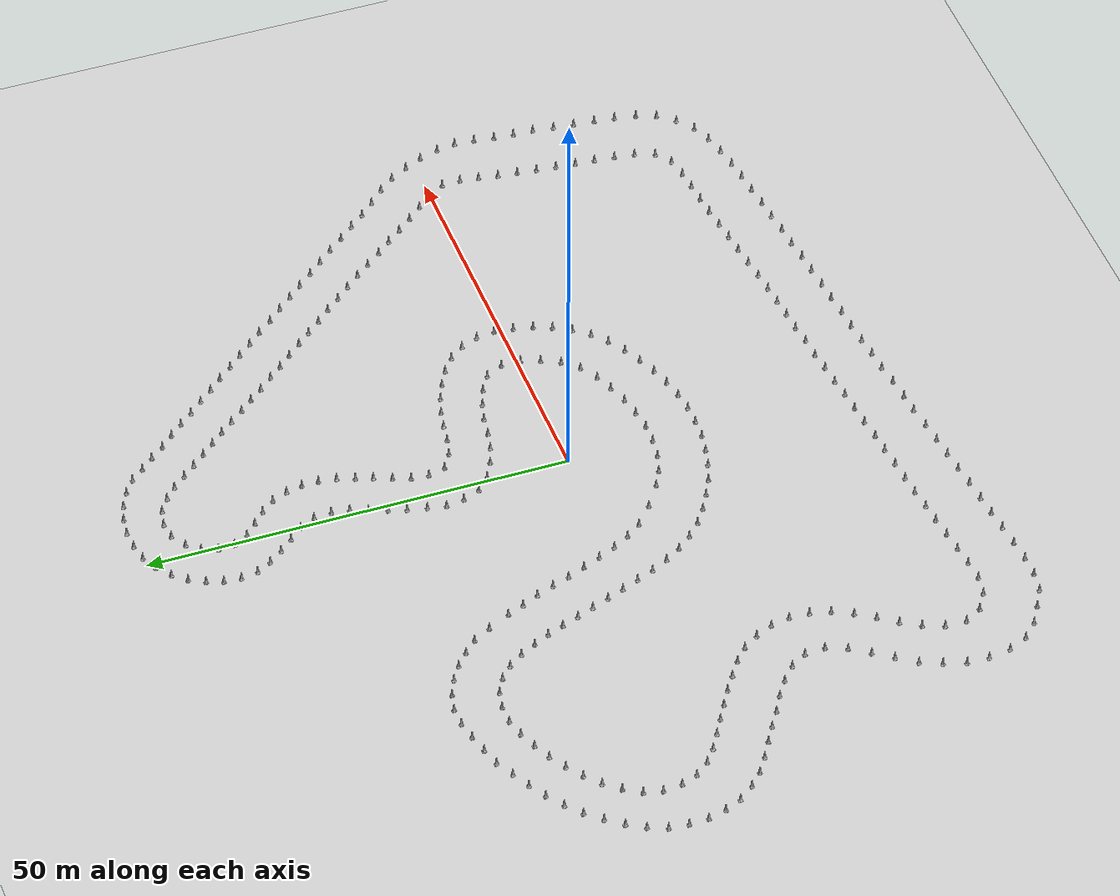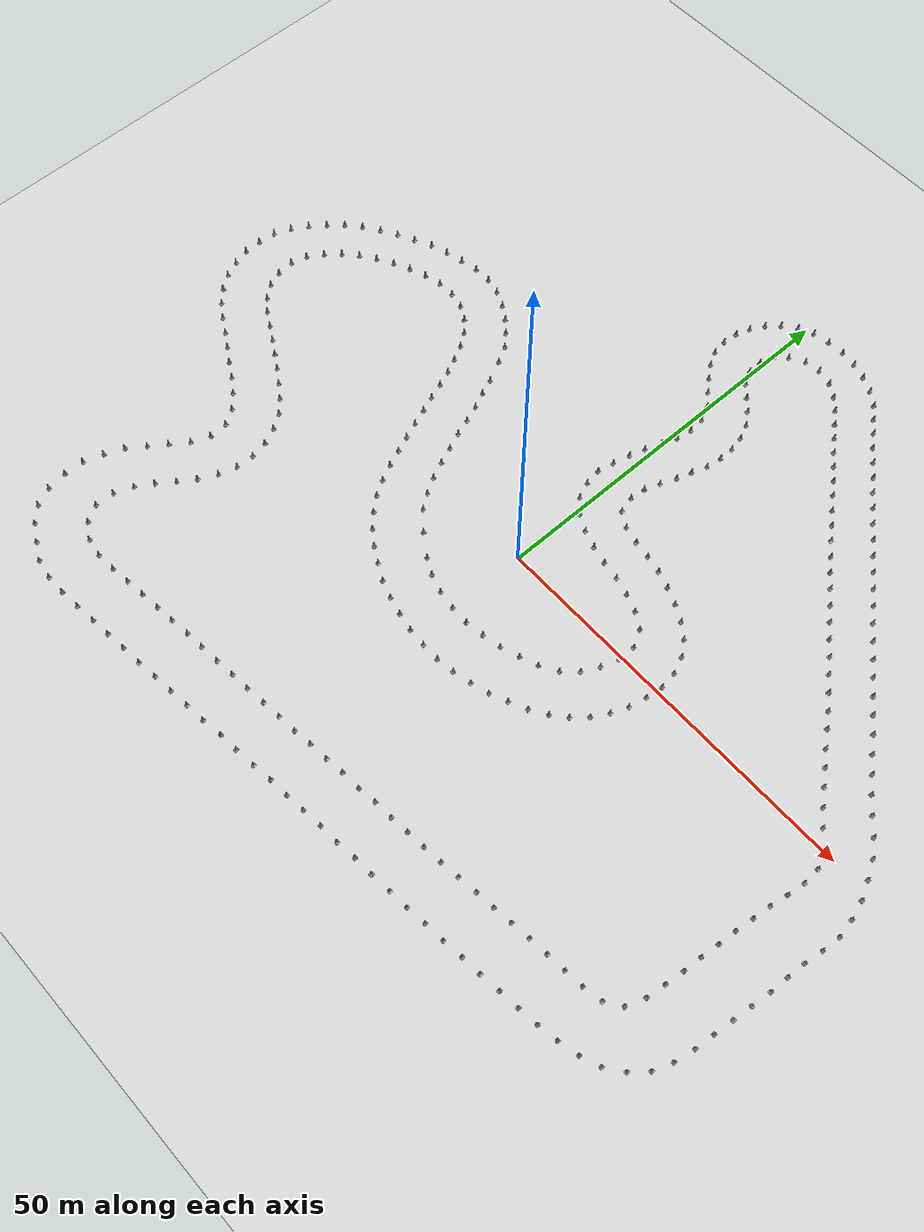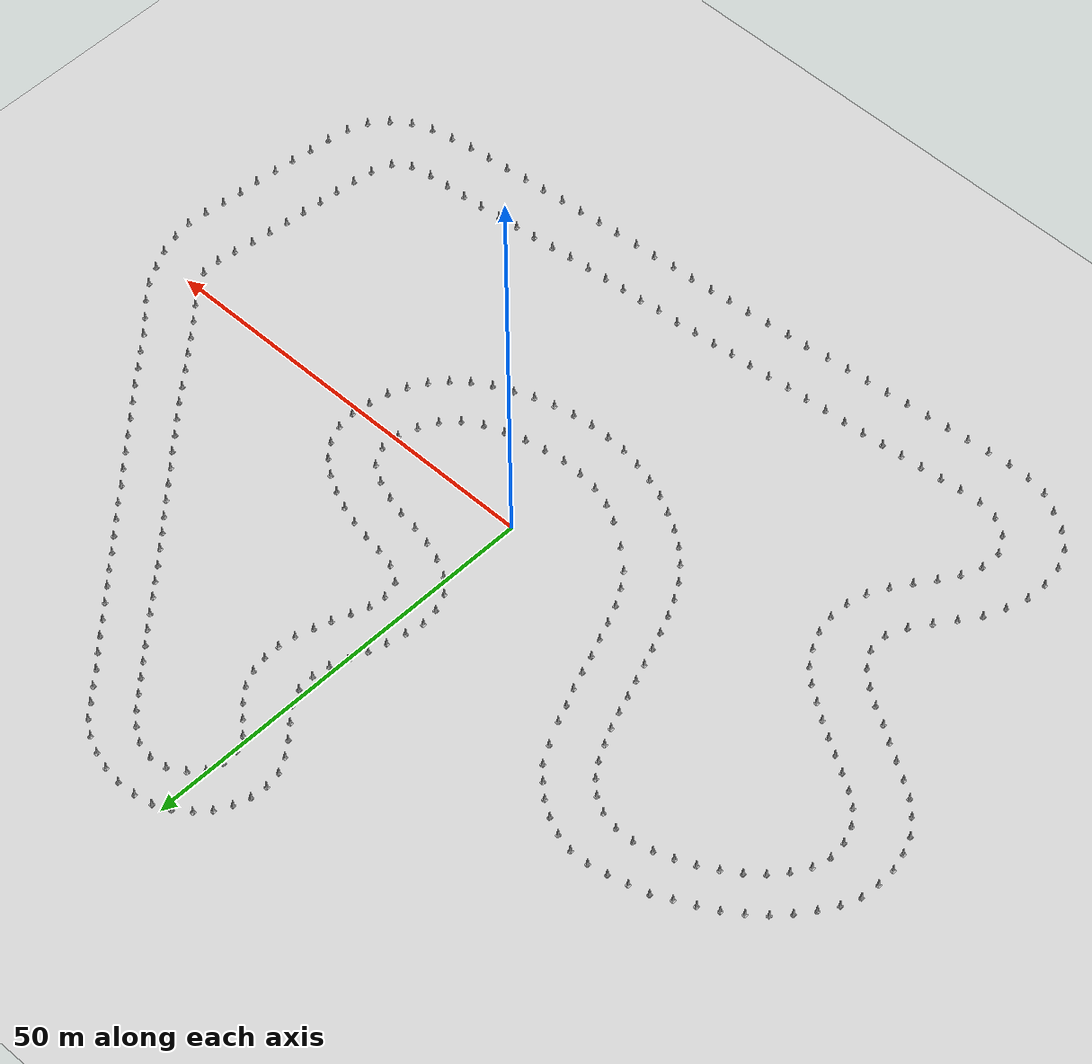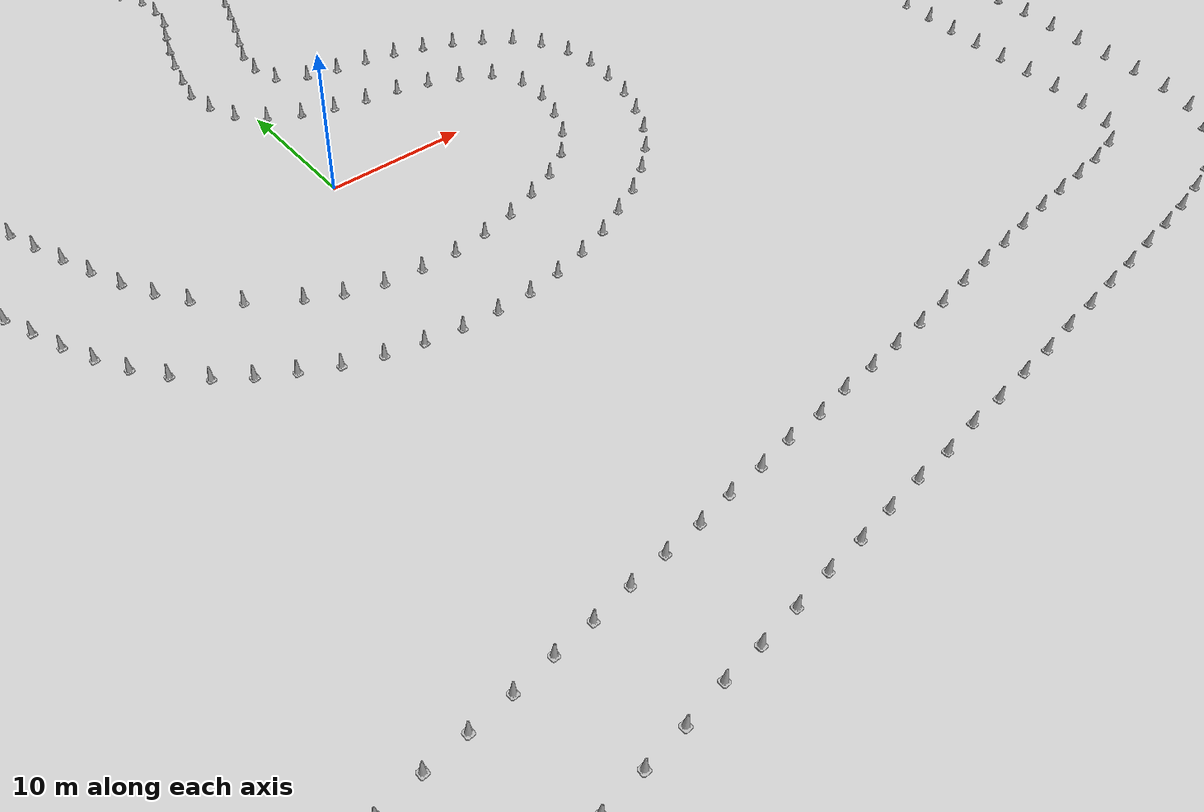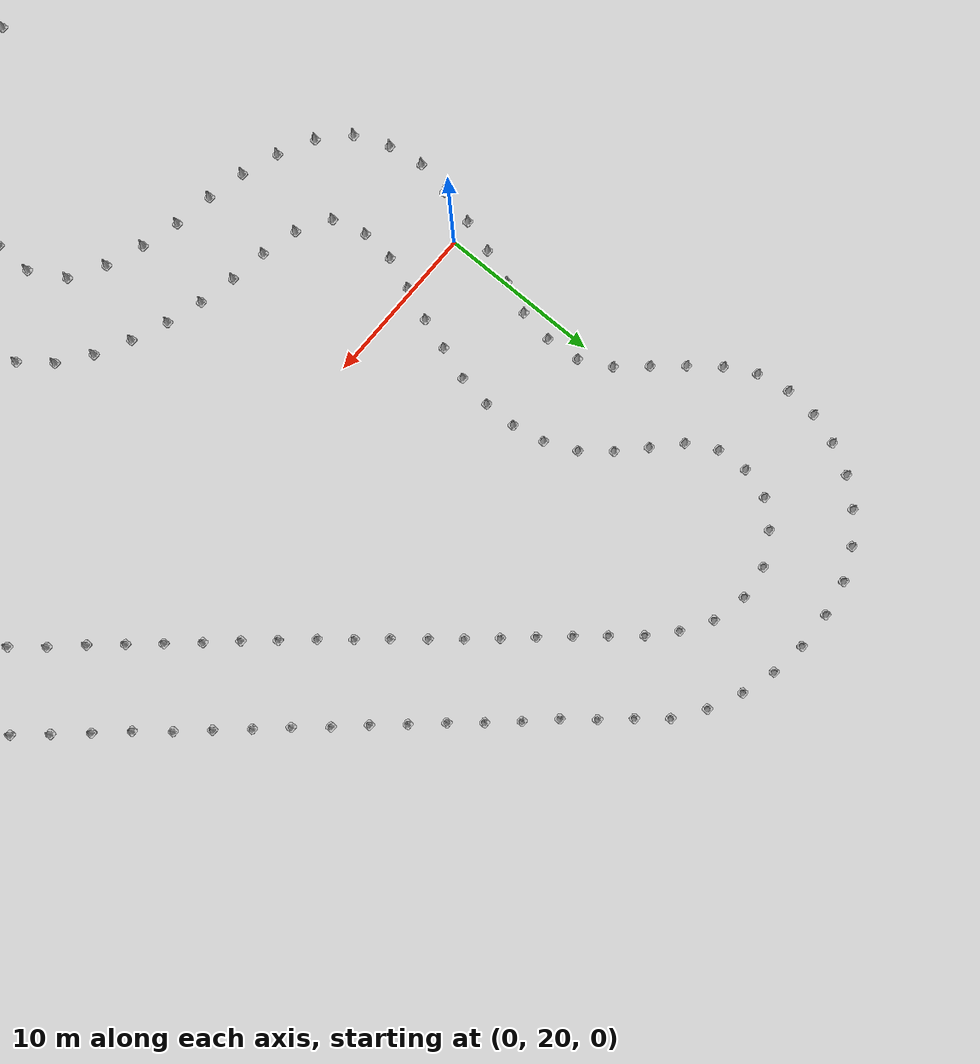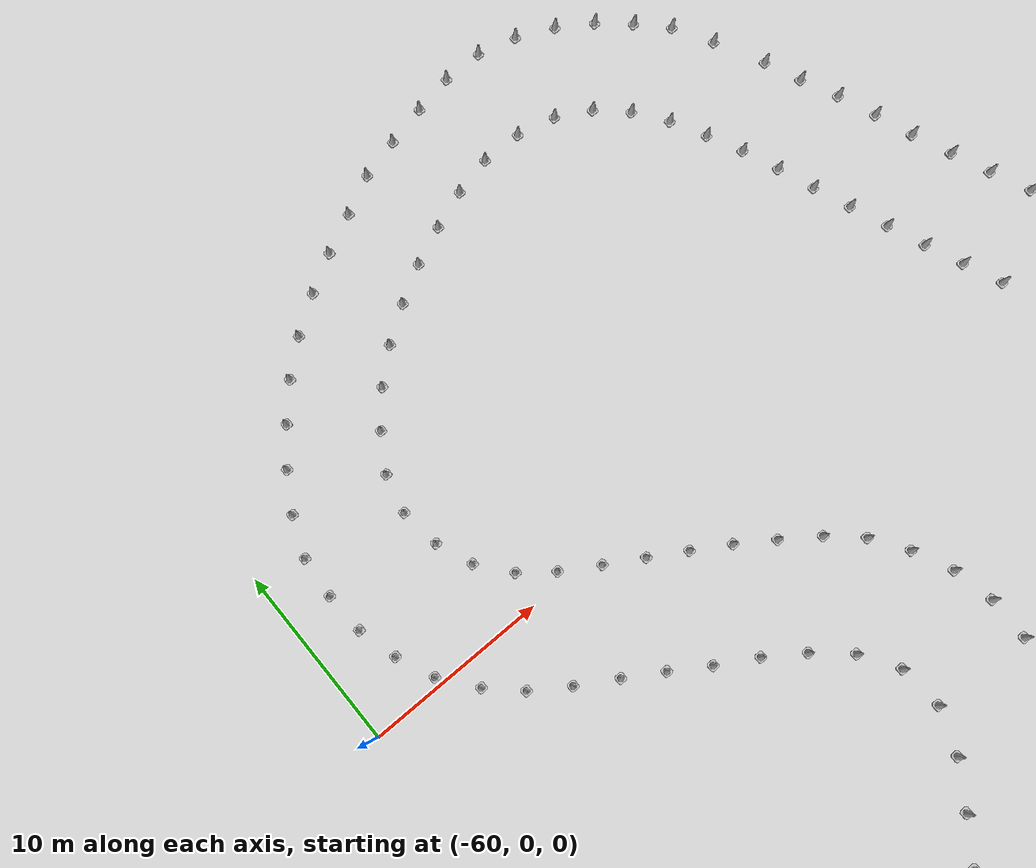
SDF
<sdf version="1.7">
 <world name="default">
  <light name="sun" type="directional">
   <pose>0 0 10 0 -0 0</pose>
   <diffuse>0.8 0.8 0.8 1</diffuse>
   <specular>0.2 0.2 0.2 1</specular>
   <attenuation>
    <range>1000</range>
    <constant>0.9</constant>
    <linear>0.01</linear>
    <quadratic>0.001</quadratic>
   </attenuation>
   <direction>-0.5 0.1 -0.9</direction>
   <spot><inner_angle>0</inner_angle><outer_angle>0</outer_angle><falloff>0</falloff></spot>
  </light>
  <model name="ground_plane">
   <static>1</static>
   <link name="link">
    <collision name="collision">
     <geometry><plane><normal>0 0 1</normal><size>125 125</size></plane></geometry>
     <surface>
      <contact><collide_bitmask>65535</collide_bitmask></contact>
      <friction><ode><mu>100</mu><mu2>50</mu2></ode></friction>
     </surface>
    </collision>
    <visual name="visual">
     <cast_shadows>0</cast_shadows>
     <geometry><plane><normal>0 0 1</normal><size>125 125</size></plane></geometry>
     <material>
      <script><uri>file://media/materials/scripts/gazebo.material</uri><name>Gazebo/Grey</name></script>
     </material>
    </visual>
   </link>
  </model>
  <gravity>0 0 -9.8</gravity>
  <magnetic_field>6e-06 2.3e-05 -4.2e-05</magnetic_field>
  <atmosphere type="adiabatic"/>
  <physics type="ode">
   <max_step_size>0.001</max_step_size>
   <real_time_factor>1</real_time_factor>
   <real_time_update_rate>1000</real_time_update_rate>
  </physics>
  <scene><ambient>0.4 0.4 0.4 1</ambient><background>0.7 0.7 0.7 1</background><shadows>1</shadows></scene>
  <spherical_coordinates>
   <surface_model>EARTH_WGS84</surface_model>
   <latitude_deg>0</latitude_deg>
   <longitude_deg>0</longitude_deg>
   <elevation>0</elevation>
   <heading_deg>0</heading_deg>
  </spherical_coordinates>
  <model name="Construction Cone 0">
   <link name="link">
    <collision name="collision">
     <geometry>
      <mesh><scale>10 10 10</scale><uri>model://construction_cone/meshes/construction_cone.dae</uri></mesh>
     </geometry>
    </collision>
    <visual name="visual">
     <geometry>
      <mesh><scale>10 10 10</scale><uri>model://construction_cone/meshes/construction_cone.dae</uri></mesh>
     </geometry>
    </visual>
    <inertial>
     <inertia><ixx>1</ixx><ixy>0</ixy><ixz>0</ixz><iyy>1</iyy><iyz>0</iyz><izz>1</izz></inertia>
     <mass>1</mass>
    </inertial>
   </link>
   <pose>5.576248381191256 50.64985582765605 0 0 0 0</pose>
  </model>
  <model name="Construction Cone 1">
   <link name="link">
    <collision name="collision">
     <geometry>
      <mesh><scale>10 10 10</scale><uri>model://construction_cone/meshes/construction_cone.dae</uri></mesh>
     </geometry>
    </collision>
    <visual name="visual">
     <geometry>
      <mesh><scale>10 10 10</scale><uri>model://construction_cone/meshes/construction_cone.dae</uri></mesh>
     </geometry>
    </visual>
    <inertial>
     <inertia><ixx>1</ixx><ixy>0</ixy><ixz>0</ixz><iyy>1</iyy><iyz>0</iyz><izz>1</izz></inertia>
     <mass>1</mass>
    </inertial>
   </link>
   <pose>3.294748381191262 50.55535582765605 0 0 0 0</pose>
  </model>
  <model name="Construction Cone 2">
   <link name="link">
    <collision name="collision">
     <geometry>
      <mesh><scale>10 10 10</scale><uri>model://construction_cone/meshes/construction_cone.dae</uri></mesh>
     </geometry>
    </collision>
    <visual name="visual">
     <geometry>
      <mesh><scale>10 10 10</scale><uri>model://construction_cone/meshes/construction_cone.dae</uri></mesh>
     </geometry>
    </visual>
    <inertial>
     <inertia><ixx>1</ixx><ixy>0</ixy><ixz>0</ixz><iyy>1</iyy><iyz>0</iyz><izz>1</izz></inertia>
     <mass>1</mass>
    </inertial>
   </link>
   <pose>7.749748381191267 50.35285582765605 0 0 0 0</pose>
  </model>
  <model name="Construction Cone 3">
   <link name="link">
    <collision name="collision">
     <geometry>
      <mesh><scale>10 10 10</scale><uri>model://construction_cone/meshes/construction_cone.dae</uri></mesh>
     </geometry>
    </collision>
    <visual name="visual">
     <geometry>
      <mesh><scale>10 10 10</scale><uri>model://construction_cone/meshes/construction_cone.dae</uri></mesh>
     </geometry>
    </visual>
    <inertial>
     <inertia><ixx>1</ixx><ixy>0</ixy><ixz>0</ixz><iyy>1</iyy><iyz>0</iyz><izz>1</izz></inertia>
     <mass>1</mass>
    </inertial>
   </link>
   <pose>1.1347483811912582 50.15035582765605 0 0 0 0</pose>
  </model>
  <model name="Construction Cone 4">
   <link name="link">
    <collision name="collision">
     <geometry>
      <mesh><scale>10 10 10</scale><uri>model://construction_cone/meshes/construction_cone.dae</uri></mesh>
     </geometry>
    </collision>
    <visual name="visual">
     <geometry>
      <mesh><scale>10 10 10</scale><uri>model://construction_cone/meshes/construction_cone.dae</uri></mesh>
     </geometry>
    </visual>
    <inertial>
     <inertia><ixx>1</ixx><ixy>0</ixy><ixz>0</ixz><iyy>1</iyy><iyz>0</iyz><izz>1</izz></inertia>
     <mass>1</mass>
    </inertial>
   </link>
   <pose>9.815248381191267 49.73185582765605 0 0 0 0</pose>
  </model>
  <model name="Construction Cone 5">
   <link name="link">
    <collision name="collision">
     <geometry>
      <mesh><scale>10 10 10</scale><uri>model://construction_cone/meshes/construction_cone.dae</uri></mesh>
     </geometry>
    </collision>
    <visual name="visual">
     <geometry>
      <mesh><scale>10 10 10</scale><uri>model://construction_cone/meshes/construction_cone.dae</uri></mesh>
     </geometry>
    </visual>
    <inertial>
     <inertia><ixx>1</ixx><ixy>0</ixy><ixz>0</ixz><iyy>1</iyy><iyz>0</iyz><izz>1</izz></inertia>
     <mass>1</mass>
    </inertial>
   </link>
   <pose>-0.7687516188087429 49.24585582765605 0 0 0 0</pose>
  </model>
  <model name="Construction Cone 6">
   <link name="link">
    <collision name="collision">
     <geometry>
      <mesh><scale>10 10 10</scale><uri>model://construction_cone/meshes/construction_cone.dae</uri></mesh>
     </geometry>
    </collision>
    <visual name="visual">
     <geometry>
      <mesh><scale>10 10 10</scale><uri>model://construction_cone/meshes/construction_cone.dae</uri></mesh>
     </geometry>
    </visual>
    <inertial>
     <inertia><ixx>1</ixx><ixy>0</ixy><ixz>0</ixz><iyy>1</iyy><iyz>0</iyz><izz>1</izz></inertia>
     <mass>1</mass>
    </inertial>
   </link>
   <pose>11.809391238334115 48.771427256227476 0 0 0 0</pose>
  </model>
  <model name="Construction Cone 7">
   <link name="link">
    <collision name="collision">
     <geometry>
      <mesh><scale>10 10 10</scale><uri>model://construction_cone/meshes/construction_cone.dae</uri></mesh>
     </geometry>
    </collision>
    <visual name="visual">
     <geometry>
      <mesh><scale>10 10 10</scale><uri>model://construction_cone/meshes/construction_cone.dae</uri></mesh>
     </geometry>
    </visual>
    <inertial>
     <inertia><ixx>1</ixx><ixy>0</ixy><ixz>0</ixz><iyy>1</iyy><iyz>0</iyz><izz>1</izz></inertia>
     <mass>1</mass>
    </inertial>
   </link>
   <pose>-2.4967516188087373 47.94985582765605 0 0 0 0</pose>
  </model>
  <model name="Construction Cone 8">
   <link name="link">
    <collision name="collision">
     <geometry>
      <mesh><scale>10 10 10</scale><uri>model://construction_cone/meshes/construction_cone.dae</uri></mesh>
     </geometry>
    </collision>
    <visual name="visual">
     <geometry>
      <mesh><scale>10 10 10</scale><uri>model://construction_cone/meshes/construction_cone.dae</uri></mesh>
     </geometry>
    </visual>
    <inertial>
     <inertia><ixx>1</ixx><ixy>0</ixy><ixz>0</ixz><iyy>1</iyy><iyz>0</iyz><izz>1</izz></inertia>
     <mass>1</mass>
    </inertial>
   </link>
   <pose>13.55474838119126 47.51785582765605 0 0 0 0</pose>
  </model>
  <model name="Construction Cone 9">
   <link name="link">
    <collision name="collision">
     <geometry>
      <mesh><scale>10 10 10</scale><uri>model://construction_cone/meshes/construction_cone.dae</uri></mesh>
     </geometry>
    </collision>
    <visual name="visual">
     <geometry>
      <mesh><scale>10 10 10</scale><uri>model://construction_cone/meshes/construction_cone.dae</uri></mesh>
     </geometry>
    </visual>
    <inertial>
     <inertia><ixx>1</ixx><ixy>0</ixy><ixz>0</ixz><iyy>1</iyy><iyz>0</iyz><izz>1</izz></inertia>
     <mass>1</mass>
    </inertial>
   </link>
   <pose>-3.8467516188087387 46.41085582765605 0 0 0 0</pose>
  </model>
  <model name="Construction Cone 10">
   <link name="link">
    <collision name="collision">
     <geometry>
      <mesh><scale>10 10 10</scale><uri>model://construction_cone/meshes/construction_cone.dae</uri></mesh>
     </geometry>
    </collision>
    <visual name="visual">
     <geometry>
      <mesh><scale>10 10 10</scale><uri>model://construction_cone/meshes/construction_cone.dae</uri></mesh>
     </geometry>
    </visual>
    <inertial>
     <inertia><ixx>1</ixx><ixy>0</ixy><ixz>0</ixz><iyy>1</iyy><iyz>0</iyz><izz>1</izz></inertia>
     <mass>1</mass>
    </inertial>
   </link>
   <pose>5.49524838119126 46.35685582765605 0 0 0 0</pose>
  </model>
  <model name="Construction Cone 11">
   <link name="link">
    <collision name="collision">
     <geometry>
      <mesh><scale>10 10 10</scale><uri>model://construction_cone/meshes/construction_cone.dae</uri></mesh>
     </geometry>
    </collision>
    <visual name="visual">
     <geometry>
      <mesh><scale>10 10 10</scale><uri>model://construction_cone/meshes/construction_cone.dae</uri></mesh>
     </geometry>
    </visual>
    <inertial>
     <inertia><ixx>1</ixx><ixy>0</ixy><ixz>0</ixz><iyy>1</iyy><iyz>0</iyz><izz>1</izz></inertia>
     <mass>1</mass>
    </inertial>
   </link>
   <pose>3.42974838119126 46.10035582765605 0 0 0 0</pose>
  </model>
  <model name="Construction Cone 12">
   <link name="link">
    <collision name="collision">
     <geometry>
      <mesh><scale>10 10 10</scale><uri>model://construction_cone/meshes/construction_cone.dae</uri></mesh>
     </geometry>
    </collision>
    <visual name="visual">
     <geometry>
      <mesh><scale>10 10 10</scale><uri>model://construction_cone/meshes/construction_cone.dae</uri></mesh>
     </geometry>
    </visual>
    <inertial>
     <inertia><ixx>1</ixx><ixy>0</ixy><ixz>0</ixz><iyy>1</iyy><iyz>0</iyz><izz>1</izz></inertia>
     <mass>1</mass>
    </inertial>
   </link>
   <pose>7.62824838119127 45.87085582765605 0 0 0 0</pose>
  </model>
  <model name="Construction Cone 13">
   <link name="link">
    <collision name="collision">
     <geometry>
      <mesh><scale>10 10 10</scale><uri>model://construction_cone/meshes/construction_cone.dae</uri></mesh>
     </geometry>
    </collision>
    <visual name="visual">
     <geometry>
      <mesh><scale>10 10 10</scale><uri>model://construction_cone/meshes/construction_cone.dae</uri></mesh>
     </geometry>
    </visual>
    <inertial>
     <inertia><ixx>1</ixx><ixy>0</ixy><ixz>0</ixz><iyy>1</iyy><iyz>0</iyz><izz>1</izz></inertia>
     <mass>1</mass>
    </inertial>
   </link>
   <pose>14.88224838119126 45.94285582765605 0 0 0 0</pose>
  </model>
  <model name="Construction Cone 14">
   <link name="link">
    <collision name="collision">
     <geometry>
      <mesh><scale>10 10 10</scale><uri>model://construction_cone/meshes/construction_cone.dae</uri></mesh>
     </geometry>
    </collision>
    <visual name="visual">
     <geometry>
      <mesh><scale>10 10 10</scale><uri>model://construction_cone/meshes/construction_cone.dae</uri></mesh>
     </geometry>
    </visual>
    <inertial>
     <inertia><ixx>1</ixx><ixy>0</ixy><ixz>0</ixz><iyy>1</iyy><iyz>0</iyz><izz>1</izz></inertia>
     <mass>1</mass>
    </inertial>
   </link>
   <pose>1.5397483811912593 45.02035582765605 0 0 0 0</pose>
  </model>
  <model name="Construction Cone 15">
   <link name="link">
    <collision name="collision">
     <geometry>
      <mesh><scale>10 10 10</scale><uri>model://construction_cone/meshes/construction_cone.dae</uri></mesh>
     </geometry>
    </collision>
    <visual name="visual">
     <geometry>
      <mesh><scale>10 10 10</scale><uri>model://construction_cone/meshes/construction_cone.dae</uri></mesh>
     </geometry>
    </visual>
    <inertial>
     <inertia><ixx>1</ixx><ixy>0</ixy><ixz>0</ixz><iyy>1</iyy><iyz>0</iyz><izz>1</izz></inertia>
     <mass>1</mass>
    </inertial>
   </link>
   <pose>9.369748381191258 44.75035582765605 0 0 0 0</pose>
  </model>
  <model name="Construction Cone 16">
   <link name="link">
    <collision name="collision">
     <geometry>
      <mesh><scale>10 10 10</scale><uri>model://construction_cone/meshes/construction_cone.dae</uri></mesh>
     </geometry>
    </collision>
    <visual name="visual">
     <geometry>
      <mesh><scale>10 10 10</scale><uri>model://construction_cone/meshes/construction_cone.dae</uri></mesh>
     </geometry>
    </visual>
    <inertial>
     <inertia><ixx>1</ixx><ixy>0</ixy><ixz>0</ixz><iyy>1</iyy><iyz>0</iyz><izz>1</izz></inertia>
     <mass>1</mass>
    </inertial>
   </link>
   <pose>-4.8052516188087395 44.61535582765605 0 0 0 0</pose>
  </model>
  <model name="Construction Cone 17">
   <link name="link">
    <collision name="collision">
     <geometry>
      <mesh><scale>10 10 10</scale><uri>model://construction_cone/meshes/construction_cone.dae</uri></mesh>
     </geometry>
    </collision>
    <visual name="visual">
     <geometry>
      <mesh><scale>10 10 10</scale><uri>model://construction_cone/meshes/construction_cone.dae</uri></mesh>
     </geometry>
    </visual>
    <inertial>
     <inertia><ixx>1</ixx><ixy>0</ixy><ixz>0</ixz><iyy>1</iyy><iyz>0</iyz><izz>1</izz></inertia>
     <mass>1</mass>
    </inertial>
   </link>
   <pose>16.26824838119127 44.38585582765605 0 0 0 0</pose>
  </model>
  <model name="Construction Cone 18">
   <link name="link">
    <collision name="collision">
     <geometry>
      <mesh><scale>10 10 10</scale><uri>model://construction_cone/meshes/construction_cone.dae</uri></mesh>
     </geometry>
    </collision>
    <visual name="visual">
     <geometry>
      <mesh><scale>10 10 10</scale><uri>model://construction_cone/meshes/construction_cone.dae</uri></mesh>
     </geometry>
    </visual>
    <inertial>
     <inertia><ixx>1</ixx><ixy>0</ixy><ixz>0</ixz><iyy>1</iyy><iyz>0</iyz><izz>1</izz></inertia>
     <mass>1</mass>
    </inertial>
   </link>
   <pose>0.22349838119126275 43.60285582765605 0 0 0 0</pose>
  </model>
  <model name="Construction Cone 19">
   <link name="link">
    <collision name="collision">
     <geometry>
      <mesh><scale>10 10 10</scale><uri>model://construction_cone/meshes/construction_cone.dae</uri></mesh>
     </geometry>
    </collision>
    <visual name="visual">
     <geometry>
      <mesh><scale>10 10 10</scale><uri>model://construction_cone/meshes/construction_cone.dae</uri></mesh>
     </geometry>
    </visual>
    <inertial>
     <inertia><ixx>1</ixx><ixy>0</ixy><ixz>0</ixz><iyy>1</iyy><iyz>0</iyz><izz>1</izz></inertia>
     <mass>1</mass>
    </inertial>
   </link>
   <pose>10.854748381191257 43.40035582765605 0 0 0 0</pose>
  </model>
  <model name="Construction Cone 20">
   <link name="link">
    <collision name="collision">
     <geometry>
      <mesh><scale>10 10 10</scale><uri>model://construction_cone/meshes/construction_cone.dae</uri></mesh>
     </geometry>
    </collision>
    <visual name="visual">
     <geometry>
      <mesh><scale>10 10 10</scale><uri>model://construction_cone/meshes/construction_cone.dae</uri></mesh>
     </geometry>
    </visual>
    <inertial>
     <inertia><ixx>1</ixx><ixy>0</ixy><ixz>0</ixz><iyy>1</iyy><iyz>0</iyz><izz>1</izz></inertia>
     <mass>1</mass>
    </inertial>
   </link>
   <pose>-5.412751618808741 42.72535582765605 0 0 0 0</pose>
  </model>
  <model name="Construction Cone 21">
   <link name="link">
    <collision name="collision">
     <geometry>
      <mesh><scale>10 10 10</scale><uri>model://construction_cone/meshes/construction_cone.dae</uri></mesh>
     </geometry>
    </collision>
    <visual name="visual">
     <geometry>
      <mesh><scale>10 10 10</scale><uri>model://construction_cone/meshes/construction_cone.dae</uri></mesh>
     </geometry>
    </visual>
    <inertial>
     <inertia><ixx>1</ixx><ixy>0</ixy><ixz>0</ixz><iyy>1</iyy><iyz>0</iyz><izz>1</izz></inertia>
     <mass>1</mass>
    </inertial>
   </link>
   <pose>17.604748381191257 42.72535582765605 0 0 0 0</pose>
  </model>
  <model name="Construction Cone 22">
   <link name="link">
    <collision name="collision">
     <geometry>
      <mesh><scale>10 10 10</scale><uri>model://construction_cone/meshes/construction_cone.dae</uri></mesh>
     </geometry>
    </collision>
    <visual name="visual">
     <geometry>
      <mesh><scale>10 10 10</scale><uri>model://construction_cone/meshes/construction_cone.dae</uri></mesh>
     </geometry>
    </visual>
    <inertial>
     <inertia><ixx>1</ixx><ixy>0</ixy><ixz>0</ixz><iyy>1</iyy><iyz>0</iyz><izz>1</izz></inertia>
     <mass>1</mass>
    </inertial>
   </link>
   <pose>12.191248381191258 41.82085582765605 0 0 0 0</pose>
  </model>
  <model name="Construction Cone 23">
   <link name="link">
    <collision name="collision">
     <geometry>
      <mesh><scale>10 10 10</scale><uri>model://construction_cone/meshes/construction_cone.dae</uri></mesh>
     </geometry>
    </collision>
    <visual name="visual">
     <geometry>
      <mesh><scale>10 10 10</scale><uri>model://construction_cone/meshes/construction_cone.dae</uri></mesh>
     </geometry>
    </visual>
    <inertial>
     <inertia><ixx>1</ixx><ixy>0</ixy><ixz>0</ixz><iyy>1</iyy><iyz>0</iyz><izz>1</izz></inertia>
     <mass>1</mass>
    </inertial>
   </link>
   <pose>-0.3367516188087336 41.73985582765605 0 0 0 0</pose>
  </model>
  <model name="Construction Cone 24">
   <link name="link">
    <collision name="collision">
     <geometry>
      <mesh><scale>10 10 10</scale><uri>model://construction_cone/meshes/construction_cone.dae</uri></mesh>
     </geometry>
    </collision>
    <visual name="visual">
     <geometry>
      <mesh><scale>10 10 10</scale><uri>model://construction_cone/meshes/construction_cone.dae</uri></mesh>
     </geometry>
    </visual>
    <inertial>
     <inertia><ixx>1</ixx><ixy>0</ixy><ixz>0</ixz><iyy>1</iyy><iyz>0</iyz><izz>1</izz></inertia>
     <mass>1</mass>
    </inertial>
   </link>
   <pose>19.089748381191256 41.17285582765605 0 0 0 0</pose>
  </model>
  <model name="Construction Cone 25">
   <link name="link">
    <collision name="collision">
     <geometry>
      <mesh><scale>10 10 10</scale><uri>model://construction_cone/meshes/construction_cone.dae</uri></mesh>
     </geometry>
    </collision>
    <visual name="visual">
     <geometry>
      <mesh><scale>10 10 10</scale><uri>model://construction_cone/meshes/construction_cone.dae</uri></mesh>
     </geometry>
    </visual>
    <inertial>
     <inertia><ixx>1</ixx><ixy>0</ixy><ixz>0</ixz><iyy>1</iyy><iyz>0</iyz><izz>1</izz></inertia>
     <mass>1</mass>
    </inertial>
   </link>
   <pose>-5.581501618808737 40.73410582765605 0 0 0 0</pose>
  </model>
  <model name="Construction Cone 26">
   <link name="link">
    <collision name="collision">
     <geometry>
      <mesh><scale>10 10 10</scale><uri>model://construction_cone/meshes/construction_cone.dae</uri></mesh>
     </geometry>
    </collision>
    <visual name="visual">
     <geometry>
      <mesh><scale>10 10 10</scale><uri>model://construction_cone/meshes/construction_cone.dae</uri></mesh>
     </geometry>
    </visual>
    <inertial>
     <inertia><ixx>1</ixx><ixy>0</ixy><ixz>0</ixz><iyy>1</iyy><iyz>0</iyz><izz>1</izz></inertia>
     <mass>1</mass>
    </inertial>
   </link>
   <pose>13.514248381191265 40.28185582765605 0 0 0 0</pose>
  </model>
  <model name="Construction Cone 27">
   <link name="link">
    <collision name="collision">
     <geometry>
      <mesh><scale>10 10 10</scale><uri>model://construction_cone/meshes/construction_cone.dae</uri></mesh>
     </geometry>
    </collision>
    <visual name="visual">
     <geometry>
      <mesh><scale>10 10 10</scale><uri>model://construction_cone/meshes/construction_cone.dae</uri></mesh>
     </geometry>
    </visual>
    <inertial>
     <inertia><ixx>1</ixx><ixy>0</ixy><ixz>0</ixz><iyy>1</iyy><iyz>0</iyz><izz>1</izz></inertia>
     <mass>1</mass>
    </inertial>
   </link>
   <pose>-0.24900161880874094 39.82285582765605 0 0 0 0</pose>
  </model>
  <model name="Construction Cone 28">
   <link name="link">
    <collision name="collision">
     <geometry>
      <mesh><scale>10 10 10</scale><uri>model://construction_cone/meshes/construction_cone.dae</uri></mesh>
     </geometry>
    </collision>
    <visual name="visual">
     <geometry>
      <mesh><scale>10 10 10</scale><uri>model://construction_cone/meshes/construction_cone.dae</uri></mesh>
     </geometry>
    </visual>
    <inertial>
     <inertia><ixx>1</ixx><ixy>0</ixy><ixz>0</ixz><iyy>1</iyy><iyz>0</iyz><izz>1</izz></inertia>
     <mass>1</mass>
    </inertial>
   </link>
   <pose>20.50724838119126 39.59785582765605 0 0 0 0</pose>
  </model>
  <model name="Construction Cone 29">
   <link name="link">
    <collision name="collision">
     <geometry>
      <mesh><scale>10 10 10</scale><uri>model://construction_cone/meshes/construction_cone.dae</uri></mesh>
     </geometry>
    </collision>
    <visual name="visual">
     <geometry>
      <mesh><scale>10 10 10</scale><uri>model://construction_cone/meshes/construction_cone.dae</uri></mesh>
     </geometry>
    </visual>
    <inertial>
     <inertia><ixx>1</ixx><ixy>0</ixy><ixz>0</ixz><iyy>1</iyy><iyz>0</iyz><izz>1</izz></inertia>
     <mass>1</mass>
    </inertial>
   </link>
   <pose>-5.223751618808741 38.71585582765605 0 0 0 0</pose>
  </model>
  <model name="Construction Cone 30">
   <link name="link">
    <collision name="collision">
     <geometry>
      <mesh><scale>10 10 10</scale><uri>model://construction_cone/meshes/construction_cone.dae</uri></mesh>
     </geometry>
    </collision>
    <visual name="visual">
     <geometry>
      <mesh><scale>10 10 10</scale><uri>model://construction_cone/meshes/construction_cone.dae</uri></mesh>
     </geometry>
    </visual>
    <inertial>
     <inertia><ixx>1</ixx><ixy>0</ixy><ixz>0</ixz><iyy>1</iyy><iyz>0</iyz><izz>1</izz></inertia>
     <mass>1</mass>
    </inertial>
   </link>
   <pose>14.89124838119126 38.71585582765605 0 0 0 0</pose>
  </model>
  <model name="Construction Cone 31">
   <link name="link">
    <collision name="collision">
     <geometry>
      <mesh><scale>10 10 10</scale><uri>model://construction_cone/meshes/construction_cone.dae</uri></mesh>
     </geometry>
    </collision>
    <visual name="visual">
     <geometry>
      <mesh><scale>10 10 10</scale><uri>model://construction_cone/meshes/construction_cone.dae</uri></mesh>
     </geometry>
    </visual>
    <inertial>
     <inertia><ixx>1</ixx><ixy>0</ixy><ixz>0</ixz><iyy>1</iyy><iyz>0</iyz><izz>1</izz></inertia>
     <mass>1</mass>
    </inertial>
   </link>
   <pose>0.6959983811912593 38.06785582765605 0 0 0 0</pose>
  </model>
  <model name="Construction Cone 32">
   <link name="link">
    <collision name="collision">
     <geometry>
      <mesh><scale>10 10 10</scale><uri>model://construction_cone/meshes/construction_cone.dae</uri></mesh>
     </geometry>
    </collision>
    <visual name="visual">
     <geometry>
      <mesh><scale>10 10 10</scale><uri>model://construction_cone/meshes/construction_cone.dae</uri></mesh>
     </geometry>
    </visual>
    <inertial>
     <inertia><ixx>1</ixx><ixy>0</ixy><ixz>0</ixz><iyy>1</iyy><iyz>0</iyz><izz>1</izz></inertia>
     <mass>1</mass>
    </inertial>
   </link>
   <pose>21.890998381191267 37.96660582765605 0 0 0 0</pose>
  </model>
  <model name="Construction Cone 33">
   <link name="link">
    <collision name="collision">
     <geometry>
      <mesh><scale>10 10 10</scale><uri>model://construction_cone/meshes/construction_cone.dae</uri></mesh>
     </geometry>
    </collision>
    <visual name="visual">
     <geometry>
      <mesh><scale>10 10 10</scale><uri>model://construction_cone/meshes/construction_cone.dae</uri></mesh>
     </geometry>
    </visual>
    <inertial>
     <inertia><ixx>1</ixx><ixy>0</ixy><ixz>0</ixz><iyy>1</iyy><iyz>0</iyz><izz>1</izz></inertia>
     <mass>1</mass>
    </inertial>
   </link>
   <pose>16.254748381191263 37.19035582765605 0 0 0 0</pose>
  </model>
  <model name="Construction Cone 34">
   <link name="link">
    <collision name="collision">
     <geometry>
      <mesh><scale>10 10 10</scale><uri>model://construction_cone/meshes/construction_cone.dae</uri></mesh>
     </geometry>
    </collision>
    <visual name="visual">
     <geometry>
      <mesh><scale>10 10 10</scale><uri>model://construction_cone/meshes/construction_cone.dae</uri></mesh>
     </geometry>
    </visual>
    <inertial>
     <inertia><ixx>1</ixx><ixy>0</ixy><ixz>0</ixz><iyy>1</iyy><iyz>0</iyz><izz>1</izz></inertia>
     <mass>1</mass>
    </inertial>
   </link>
   <pose>-4.26525161880874 36.92035582765605 0 0 0 0</pose>
  </model>
  <model name="Construction Cone 35">
   <link name="link">
    <collision name="collision">
     <geometry>
      <mesh><scale>10 10 10</scale><uri>model://construction_cone/meshes/construction_cone.dae</uri></mesh>
     </geometry>
    </collision>
    <visual name="visual">
     <geometry>
      <mesh><scale>10 10 10</scale><uri>model://construction_cone/meshes/construction_cone.dae</uri></mesh>
     </geometry>
    </visual>
    <inertial>
     <inertia><ixx>1</ixx><ixy>0</ixy><ixz>0</ixz><iyy>1</iyy><iyz>0</iyz><izz>1</izz></inertia>
     <mass>1</mass>
    </inertial>
   </link>
   <pose>2.2147483811912636 36.65035582765605 0 0 0 0</pose>
  </model>
  <model name="Construction Cone 36">
   <link name="link">
    <collision name="collision">
     <geometry>
      <mesh><scale>10 10 10</scale><uri>model://construction_cone/meshes/construction_cone.dae</uri></mesh>
     </geometry>
    </collision>
    <visual name="visual">
     <geometry>
      <mesh><scale>10 10 10</scale><uri>model://construction_cone/meshes/construction_cone.dae</uri></mesh>
     </geometry>
    </visual>
    <inertial>
     <inertia><ixx>1</ixx><ixy>0</ixy><ixz>0</ixz><iyy>1</iyy><iyz>0</iyz><izz>1</izz></inertia>
     <mass>1</mass>
    </inertial>
   </link>
   <pose>23.364748381191262 36.33535582765605 0 0 0 0</pose>
  </model>
  <model name="Construction Cone 37">
   <link name="link">
    <collision name="collision">
     <geometry>
      <mesh><scale>10 10 10</scale><uri>model://construction_cone/meshes/construction_cone.dae</uri></mesh>
     </geometry>
    </collision>
    <visual name="visual">
     <geometry>
      <mesh><scale>10 10 10</scale><uri>model://construction_cone/meshes/construction_cone.dae</uri></mesh>
     </geometry>
    </visual>
    <inertial>
     <inertia><ixx>1</ixx><ixy>0</ixy><ixz>0</ixz><iyy>1</iyy><iyz>0</iyz><izz>1</izz></inertia>
     <mass>1</mass>
    </inertial>
   </link>
   <pose>17.604748381191257 35.637855827656054 0 0 0 0</pose>
  </model>
  <model name="Construction Cone 38">
   <link name="link">
    <collision name="collision">
     <geometry>
      <mesh><scale>10 10 10</scale><uri>model://construction_cone/meshes/construction_cone.dae</uri></mesh>
     </geometry>
    </collision>
    <visual name="visual">
     <geometry>
      <mesh><scale>10 10 10</scale><uri>model://construction_cone/meshes/construction_cone.dae</uri></mesh>
     </geometry>
    </visual>
    <inertial>
     <inertia><ixx>1</ixx><ixy>0</ixy><ixz>0</ixz><iyy>1</iyy><iyz>0</iyz><izz>1</izz></inertia>
     <mass>1</mass>
    </inertial>
   </link>
   <pose>-2.9490016188087367 35.23285582765605 0 0 0 0</pose>
  </model>
  <model name="Construction Cone 39">
   <link name="link">
    <collision name="collision">
     <geometry>
      <mesh><scale>10 10 10</scale><uri>model://construction_cone/meshes/construction_cone.dae</uri></mesh>
     </geometry>
    </collision>
    <visual name="visual">
     <geometry>
      <mesh><scale>10 10 10</scale><uri>model://construction_cone/meshes/construction_cone.dae</uri></mesh>
     </geometry>
    </visual>
    <inertial>
     <inertia><ixx>1</ixx><ixy>0</ixy><ixz>0</ixz><iyy>1</iyy><iyz>0</iyz><izz>1</izz></inertia>
     <mass>1</mass>
    </inertial>
   </link>
   <pose>3.699748381191263 35.23285582765605 0 0 0 0</pose>
  </model>
  <model name="Construction Cone 40">
   <link name="link">
    <collision name="collision">
     <geometry>
      <mesh><scale>10 10 10</scale><uri>model://construction_cone/meshes/construction_cone.dae</uri></mesh>
     </geometry>
    </collision>
    <visual name="visual">
     <geometry>
      <mesh><scale>10 10 10</scale><uri>model://construction_cone/meshes/construction_cone.dae</uri></mesh>
     </geometry>
    </visual>
    <inertial>
     <inertia><ixx>1</ixx><ixy>0</ixy><ixz>0</ixz><iyy>1</iyy><iyz>0</iyz><izz>1</izz></inertia>
     <mass>1</mass>
    </inertial>
   </link>
   <pose>24.793498381191256 34.69285582765605 0 0 0 0</pose>
  </model>
  <model name="Construction Cone 41">
   <link name="link">
    <collision name="collision">
     <geometry>
      <mesh><scale>10 10 10</scale><uri>model://construction_cone/meshes/construction_cone.dae</uri></mesh>
     </geometry>
    </collision>
    <visual name="visual">
     <geometry>
      <mesh><scale>10 10 10</scale><uri>model://construction_cone/meshes/construction_cone.dae</uri></mesh>
     </geometry>
    </visual>
    <inertial>
     <inertia><ixx>1</ixx><ixy>0</ixy><ixz>0</ixz><iyy>1</iyy><iyz>0</iyz><izz>1</izz></inertia>
     <mass>1</mass>
    </inertial>
   </link>
   <pose>18.932248381191272 34.06285582765605 0 0 0 0</pose>
  </model>
  <model name="Construction Cone 42">
   <link name="link">
    <collision name="collision">
     <geometry>
      <mesh><scale>10 10 10</scale><uri>model://construction_cone/meshes/construction_cone.dae</uri></mesh>
     </geometry>
    </collision>
    <visual name="visual">
     <geometry>
      <mesh><scale>10 10 10</scale><uri>model://construction_cone/meshes/construction_cone.dae</uri></mesh>
     </geometry>
    </visual>
    <inertial>
     <inertia><ixx>1</ixx><ixy>0</ixy><ixz>0</ixz><iyy>1</iyy><iyz>0</iyz><izz>1</izz></inertia>
     <mass>1</mass>
    </inertial>
   </link>
   <pose>-1.5652516188087375 33.61285582765605 0 0 0 0</pose>
  </model>
  <model name="Construction Cone 43">
   <link name="link">
    <collision name="collision">
     <geometry>
      <mesh><scale>10 10 10</scale><uri>model://construction_cone/meshes/construction_cone.dae</uri></mesh>
     </geometry>
    </collision>
    <visual name="visual">
     <geometry>
      <mesh><scale>10 10 10</scale><uri>model://construction_cone/meshes/construction_cone.dae</uri></mesh>
     </geometry>
    </visual>
    <inertial>
     <inertia><ixx>1</ixx><ixy>0</ixy><ixz>0</ixz><iyy>1</iyy><iyz>0</iyz><izz>1</izz></inertia>
     <mass>1</mass>
    </inertial>
   </link>
   <pose>5.01599838119126 33.61285582765605 0 0 0 0</pose>
  </model>
  <model name="Construction Cone 44">
   <link name="link">
    <collision name="collision">
     <geometry>
      <mesh><scale>10 10 10</scale><uri>model://construction_cone/meshes/construction_cone.dae</uri></mesh>
     </geometry>
    </collision>
    <visual name="visual">
     <geometry>
      <mesh><scale>10 10 10</scale><uri>model://construction_cone/meshes/construction_cone.dae</uri></mesh>
     </geometry>
    </visual>
    <inertial>
     <inertia><ixx>1</ixx><ixy>0</ixy><ixz>0</ixz><iyy>1</iyy><iyz>0</iyz><izz>1</izz></inertia>
     <mass>1</mass>
    </inertial>
   </link>
   <pose>26.26724838119125 33.09535582765605 0 0 0 0</pose>
  </model>
  <model name="Construction Cone 45">
   <link name="link">
    <collision name="collision">
     <geometry>
      <mesh><scale>10 10 10</scale><uri>model://construction_cone/meshes/construction_cone.dae</uri></mesh>
     </geometry>
    </collision>
    <visual name="visual">
     <geometry>
      <mesh><scale>10 10 10</scale><uri>model://construction_cone/meshes/construction_cone.dae</uri></mesh>
     </geometry>
    </visual>
    <inertial>
     <inertia><ixx>1</ixx><ixy>0</ixy><ixz>0</ixz><iyy>1</iyy><iyz>0</iyz><izz>1</izz></inertia>
     <mass>1</mass>
    </inertial>
   </link>
   <pose>20.30474838119126 32.397855827656045 0 0 0 0</pose>
  </model>
  <model name="Construction Cone 46">
   <link name="link">
    <collision name="collision">
     <geometry>
      <mesh><scale>10 10 10</scale><uri>model://construction_cone/meshes/construction_cone.dae</uri></mesh>
     </geometry>
    </collision>
    <visual name="visual">
     <geometry>
      <mesh><scale>10 10 10</scale><uri>model://construction_cone/meshes/construction_cone.dae</uri></mesh>
     </geometry>
    </visual>
    <inertial>
     <inertia><ixx>1</ixx><ixy>0</ixy><ixz>0</ixz><iyy>1</iyy><iyz>0</iyz><izz>1</izz></inertia>
     <mass>1</mass>
    </inertial>
   </link>
   <pose>-0.14775161880874066 31.99285582765605 0 0 0 0</pose>
  </model>
  <model name="Construction Cone 47">
   <link name="link">
    <collision name="collision">
     <geometry>
      <mesh><scale>10 10 10</scale><uri>model://construction_cone/meshes/construction_cone.dae</uri></mesh>
     </geometry>
    </collision>
    <visual name="visual">
     <geometry>
      <mesh><scale>10 10 10</scale><uri>model://construction_cone/meshes/construction_cone.dae</uri></mesh>
     </geometry>
    </visual>
    <inertial>
     <inertia><ixx>1</ixx><ixy>0</ixy><ixz>0</ixz><iyy>1</iyy><iyz>0</iyz><izz>1</izz></inertia>
     <mass>1</mass>
    </inertial>
   </link>
   <pose>5.859748381191267 31.722855827656048 0 0 0 0</pose>
  </model>
  <model name="Construction Cone 48">
   <link name="link">
    <collision name="collision">
     <geometry>
      <mesh><scale>10 10 10</scale><uri>model://construction_cone/meshes/construction_cone.dae</uri></mesh>
     </geometry>
    </collision>
    <visual name="visual">
     <geometry>
      <mesh><scale>10 10 10</scale><uri>model://construction_cone/meshes/construction_cone.dae</uri></mesh>
     </geometry>
    </visual>
    <inertial>
     <inertia><ixx>1</ixx><ixy>0</ixy><ixz>0</ixz><iyy>1</iyy><iyz>0</iyz><izz>1</izz></inertia>
     <mass>1</mass>
    </inertial>
   </link>
   <pose>27.729748381191257 31.38535582765605 0 0 0 0</pose>
  </model>
  <model name="Construction Cone 49">
   <link name="link">
    <collision name="collision">
     <geometry>
      <mesh><scale>10 10 10</scale><uri>model://construction_cone/meshes/construction_cone.dae</uri></mesh>
     </geometry>
    </collision>
    <visual name="visual">
     <geometry>
      <mesh><scale>10 10 10</scale><uri>model://construction_cone/meshes/construction_cone.dae</uri></mesh>
     </geometry>
    </visual>
    <inertial>
     <inertia><ixx>1</ixx><ixy>0</ixy><ixz>0</ixz><iyy>1</iyy><iyz>0</iyz><izz>1</izz></inertia>
     <mass>1</mass>
    </inertial>
   </link>
   <pose>21.65474838119127 30.84535582765605 0 0 0 0</pose>
  </model>
  <model name="Construction Cone 50">
   <link name="link">
    <collision name="collision">
     <geometry>
      <mesh><scale>10 10 10</scale><uri>model://construction_cone/meshes/construction_cone.dae</uri></mesh>
     </geometry>
    </collision>
    <visual name="visual">
     <geometry>
      <mesh><scale>10 10 10</scale><uri>model://construction_cone/meshes/construction_cone.dae</uri></mesh>
     </geometry>
    </visual>
    <inertial>
     <inertia><ixx>1</ixx><ixy>0</ixy><ixz>0</ixz><iyy>1</iyy><iyz>0</iyz><izz>1</izz></inertia>
     <mass>1</mass>
    </inertial>
   </link>
   <pose>0.8309983811912645 30.10285582765605 0 0 0 0</pose>
  </model>
  <model name="Construction Cone 51">
   <link name="link">
    <collision name="collision">
     <geometry>
      <mesh><scale>10 10 10</scale><uri>model://construction_cone/meshes/construction_cone.dae</uri></mesh>
     </geometry>
    </collision>
    <visual name="visual">
     <geometry>
      <mesh><scale>10 10 10</scale><uri>model://construction_cone/meshes/construction_cone.dae</uri></mesh>
     </geometry>
    </visual>
    <inertial>
     <inertia><ixx>1</ixx><ixy>0</ixy><ixz>0</ixz><iyy>1</iyy><iyz>0</iyz><izz>1</izz></inertia>
     <mass>1</mass>
    </inertial>
   </link>
   <pose>6.264748381191268 29.765355827656048 0 0 0 0</pose>
  </model>
  <model name="Construction Cone 52">
   <link name="link">
    <collision name="collision">
     <geometry>
      <mesh><scale>10 10 10</scale><uri>model://construction_cone/meshes/construction_cone.dae</uri></mesh>
     </geometry>
    </collision>
    <visual name="visual">
     <geometry>
      <mesh><scale>10 10 10</scale><uri>model://construction_cone/meshes/construction_cone.dae</uri></mesh>
     </geometry>
    </visual>
    <inertial>
     <inertia><ixx>1</ixx><ixy>0</ixy><ixz>0</ixz><iyy>1</iyy><iyz>0</iyz><izz>1</izz></inertia>
     <mass>1</mass>
    </inertial>
   </link>
   <pose>29.214748381191256 29.765355827656048 0 0 0 0</pose>
  </model>
  <model name="Construction Cone 53">
   <link name="link">
    <collision name="collision">
     <geometry>
      <mesh><scale>10 10 10</scale><uri>model://construction_cone/meshes/construction_cone.dae</uri></mesh>
     </geometry>
    </collision>
    <visual name="visual">
     <geometry>
      <mesh><scale>10 10 10</scale><uri>model://construction_cone/meshes/construction_cone.dae</uri></mesh>
     </geometry>
    </visual>
    <inertial>
     <inertia><ixx>1</ixx><ixy>0</ixy><ixz>0</ixz><iyy>1</iyy><iyz>0</iyz><izz>1</izz></inertia>
     <mass>1</mass>
    </inertial>
   </link>
   <pose>23.004748381191263 29.22535582765605 0 0 0 0</pose>
  </model>
  <model name="Construction Cone 54">
   <link name="link">
    <collision name="collision">
     <geometry>
      <mesh><scale>10 10 10</scale><uri>model://construction_cone/meshes/construction_cone.dae</uri></mesh>
     </geometry>
    </collision>
    <visual name="visual">
     <geometry>
      <mesh><scale>10 10 10</scale><uri>model://construction_cone/meshes/construction_cone.dae</uri></mesh>
     </geometry>
    </visual>
    <inertial>
     <inertia><ixx>1</ixx><ixy>0</ixy><ixz>0</ixz><iyy>1</iyy><iyz>0</iyz><izz>1</izz></inertia>
     <mass>1</mass>
    </inertial>
   </link>
   <pose>30.699748381191256 28.077855827656048 0 0 0 0</pose>
  </model>
  <model name="Construction Cone 55">
   <link name="link">
    <collision name="collision">
     <geometry>
      <mesh><scale>10 10 10</scale><uri>model://construction_cone/meshes/construction_cone.dae</uri></mesh>
     </geometry>
    </collision>
    <visual name="visual">
     <geometry>
      <mesh><scale>10 10 10</scale><uri>model://construction_cone/meshes/construction_cone.dae</uri></mesh>
     </geometry>
    </visual>
    <inertial>
     <inertia><ixx>1</ixx><ixy>0</ixy><ixz>0</ixz><iyy>1</iyy><iyz>0</iyz><izz>1</izz></inertia>
     <mass>1</mass>
    </inertial>
   </link>
   <pose>0.9997483811912602 28.01035582765605 0 0 0 0</pose>
  </model>
  <model name="Construction Cone 56">
   <link name="link">
    <collision name="collision">
     <geometry>
      <mesh><scale>10 10 10</scale><uri>model://construction_cone/meshes/construction_cone.dae</uri></mesh>
     </geometry>
    </collision>
    <visual name="visual">
     <geometry>
      <mesh><scale>10 10 10</scale><uri>model://construction_cone/meshes/construction_cone.dae</uri></mesh>
     </geometry>
    </visual>
    <inertial>
     <inertia><ixx>1</ixx><ixy>0</ixy><ixz>0</ixz><iyy>1</iyy><iyz>0</iyz><izz>1</izz></inertia>
     <mass>1</mass>
    </inertial>
   </link>
   <pose>6.278248381191261 27.78085582765605 0 0 0 0</pose>
  </model>
  <model name="Construction Cone 57">
   <link name="link">
    <collision name="collision">
     <geometry>
      <mesh><scale>10 10 10</scale><uri>model://construction_cone/meshes/construction_cone.dae</uri></mesh>
     </geometry>
    </collision>
    <visual name="visual">
     <geometry>
      <mesh><scale>10 10 10</scale><uri>model://construction_cone/meshes/construction_cone.dae</uri></mesh>
     </geometry>
    </visual>
    <inertial>
     <inertia><ixx>1</ixx><ixy>0</ixy><ixz>0</ixz><iyy>1</iyy><iyz>0</iyz><izz>1</izz></inertia>
     <mass>1</mass>
    </inertial>
   </link>
   <pose>24.476248381191255 27.564855827656046 0 0 0 0</pose>
  </model>
  <model name="Construction Cone 58">
   <link name="link">
    <collision name="collision">
     <geometry>
      <mesh><scale>10 10 10</scale><uri>model://construction_cone/meshes/construction_cone.dae</uri></mesh>
     </geometry>
    </collision>
    <visual name="visual">
     <geometry>
      <mesh><scale>10 10 10</scale><uri>model://construction_cone/meshes/construction_cone.dae</uri></mesh>
     </geometry>
    </visual>
    <inertial>
     <inertia><ixx>1</ixx><ixy>0</ixy><ixz>0</ixz><iyy>1</iyy><iyz>0</iyz><izz>1</izz></inertia>
     <mass>1</mass>
    </inertial>
   </link>
   <pose>32.19824838119126 26.43085582765605 0 0 0 0</pose>
  </model>
  <model name="Construction Cone 59">
   <link name="link">
    <collision name="collision">
     <geometry>
      <mesh><scale>10 10 10</scale><uri>model://construction_cone/meshes/construction_cone.dae</uri></mesh>
     </geometry>
    </collision>
    <visual name="visual">
     <geometry>
      <mesh><scale>10 10 10</scale><uri>model://construction_cone/meshes/construction_cone.dae</uri></mesh>
     </geometry>
    </visual>
    <inertial>
     <inertia><ixx>1</ixx><ixy>0</ixy><ixz>0</ixz><iyy>1</iyy><iyz>0</iyz><izz>1</izz></inertia>
     <mass>1</mass>
    </inertial>
   </link>
   <pose>0.6959983811912593 25.917855827656048 0 0 0 0</pose>
  </model>
  <model name="Construction Cone 60">
   <link name="link">
    <collision name="collision">
     <geometry>
      <mesh><scale>10 10 10</scale><uri>model://construction_cone/meshes/construction_cone.dae</uri></mesh>
     </geometry>
    </collision>
    <visual name="visual">
     <geometry>
      <mesh><scale>10 10 10</scale><uri>model://construction_cone/meshes/construction_cone.dae</uri></mesh>
     </geometry>
    </visual>
    <inertial>
     <inertia><ixx>1</ixx><ixy>0</ixy><ixz>0</ixz><iyy>1</iyy><iyz>0</iyz><izz>1</izz></inertia>
     <mass>1</mass>
    </inertial>
   </link>
   <pose>25.862248381191264 25.96285582765605 0 0 0 0</pose>
  </model>
  <model name="Construction Cone 61">
   <link name="link">
    <collision name="collision">
     <geometry>
      <mesh><scale>10 10 10</scale><uri>model://construction_cone/meshes/construction_cone.dae</uri></mesh>
     </geometry>
    </collision>
    <visual name="visual">
     <geometry>
      <mesh><scale>10 10 10</scale><uri>model://construction_cone/meshes/construction_cone.dae</uri></mesh>
     </geometry>
    </visual>
    <inertial>
     <inertia><ixx>1</ixx><ixy>0</ixy><ixz>0</ixz><iyy>1</iyy><iyz>0</iyz><izz>1</izz></inertia>
     <mass>1</mass>
    </inertial>
   </link>
   <pose>5.994748381191258 25.715355827656047 0 0 0 0</pose>
  </model>
  <model name="Construction Cone 62">
   <link name="link">
    <collision name="collision">
     <geometry>
      <mesh><scale>10 10 10</scale><uri>model://construction_cone/meshes/construction_cone.dae</uri></mesh>
     </geometry>
    </collision>
    <visual name="visual">
     <geometry>
      <mesh><scale>10 10 10</scale><uri>model://construction_cone/meshes/construction_cone.dae</uri></mesh>
     </geometry>
    </visual>
    <inertial>
     <inertia><ixx>1</ixx><ixy>0</ixy><ixz>0</ixz><iyy>1</iyy><iyz>0</iyz><izz>1</izz></inertia>
     <mass>1</mass>
    </inertial>
   </link>
   <pose>-35.19375161880874 25.080855827656052 0 0 0 0</pose>
  </model>
  <model name="Construction Cone 63">
   <link name="link">
    <collision name="collision">
     <geometry>
      <mesh><scale>10 10 10</scale><uri>model://construction_cone/meshes/construction_cone.dae</uri></mesh>
     </geometry>
    </collision>
    <visual name="visual">
     <geometry>
      <mesh><scale>10 10 10</scale><uri>model://construction_cone/meshes/construction_cone.dae</uri></mesh>
     </geometry>
    </visual>
    <inertial>
     <inertia><ixx>1</ixx><ixy>0</ixy><ixz>0</ixz><iyy>1</iyy><iyz>0</iyz><izz>1</izz></inertia>
     <mass>1</mass>
    </inertial>
   </link>
   <pose>-32.871751618808744 25.134855827656047 0 0 0 0</pose>
  </model>
  <model name="Construction Cone 64">
   <link name="link">
    <collision name="collision">
     <geometry>
      <mesh><scale>10 10 10</scale><uri>model://construction_cone/meshes/construction_cone.dae</uri></mesh>
     </geometry>
    </collision>
    <visual name="visual">
     <geometry>
      <mesh><scale>10 10 10</scale><uri>model://construction_cone/meshes/construction_cone.dae</uri></mesh>
     </geometry>
    </visual>
    <inertial>
     <inertia><ixx>1</ixx><ixy>0</ixy><ixz>0</ixz><iyy>1</iyy><iyz>0</iyz><izz>1</izz></inertia>
     <mass>1</mass>
    </inertial>
   </link>
   <pose>-37.47525161880874 24.63535582765605 0 0 0 0</pose>
  </model>
  <model name="Construction Cone 65">
   <link name="link">
    <collision name="collision">
     <geometry>
      <mesh><scale>10 10 10</scale><uri>model://construction_cone/meshes/construction_cone.dae</uri></mesh>
     </geometry>
    </collision>
    <visual name="visual">
     <geometry>
      <mesh><scale>10 10 10</scale><uri>model://construction_cone/meshes/construction_cone.dae</uri></mesh>
     </geometry>
    </visual>
    <inertial>
     <inertia><ixx>1</ixx><ixy>0</ixy><ixz>0</ixz><iyy>1</iyy><iyz>0</iyz><izz>1</izz></inertia>
     <mass>1</mass>
    </inertial>
   </link>
   <pose>-30.657751618808742 24.594855827656048 0 0 0 0</pose>
  </model>
  <model name="Construction Cone 66">
   <link name="link">
    <collision name="collision">
     <geometry>
      <mesh><scale>10 10 10</scale><uri>model://construction_cone/meshes/construction_cone.dae</uri></mesh>
     </geometry>
    </collision>
    <visual name="visual">
     <geometry>
      <mesh><scale>10 10 10</scale><uri>model://construction_cone/meshes/construction_cone.dae</uri></mesh>
     </geometry>
    </visual>
    <inertial>
     <inertia><ixx>1</ixx><ixy>0</ixy><ixz>0</ixz><iyy>1</iyy><iyz>0</iyz><izz>1</izz></inertia>
     <mass>1</mass>
    </inertial>
   </link>
   <pose>33.66974838119127 24.63535582765605 0 0 0 0</pose>
  </model>
  <model name="Construction Cone 67">
   <link name="link">
    <collision name="collision">
     <geometry>
      <mesh><scale>10 10 10</scale><uri>model://construction_cone/meshes/construction_cone.dae</uri></mesh>
     </geometry>
    </collision>
    <visual name="visual">
     <geometry>
      <mesh><scale>10 10 10</scale><uri>model://construction_cone/meshes/construction_cone.dae</uri></mesh>
     </geometry>
    </visual>
    <inertial>
     <inertia><ixx>1</ixx><ixy>0</ixy><ixz>0</ixz><iyy>1</iyy><iyz>0</iyz><izz>1</izz></inertia>
     <mass>1</mass>
    </inertial>
   </link>
   <pose>27.324748381191256 24.36535582765605 0 0 0 0</pose>
  </model>
  <model name="Construction Cone 68">
   <link name="link">
    <collision name="collision">
     <geometry>
      <mesh><scale>10 10 10</scale><uri>model://construction_cone/meshes/construction_cone.dae</uri></mesh>
     </geometry>
    </collision>
    <visual name="visual">
     <geometry>
      <mesh><scale>10 10 10</scale><uri>model://construction_cone/meshes/construction_cone.dae</uri></mesh>
     </geometry>
    </visual>
    <inertial>
     <inertia><ixx>1</ixx><ixy>0</ixy><ixz>0</ixz><iyy>1</iyy><iyz>0</iyz><izz>1</izz></inertia>
     <mass>1</mass>
    </inertial>
   </link>
   <pose>-39.79275161880874 24.07285582765605 0 0 0 0</pose>
  </model>
  <model name="Construction Cone 69">
   <link name="link">
    <collision name="collision">
     <geometry>
      <mesh><scale>10 10 10</scale><uri>model://construction_cone/meshes/construction_cone.dae</uri></mesh>
     </geometry>
    </collision>
    <visual name="visual">
     <geometry>
      <mesh><scale>10 10 10</scale><uri>model://construction_cone/meshes/construction_cone.dae</uri></mesh>
     </geometry>
    </visual>
    <inertial>
     <inertia><ixx>1</ixx><ixy>0</ixy><ixz>0</ixz><iyy>1</iyy><iyz>0</iyz><izz>1</izz></inertia>
     <mass>1</mass>
    </inertial>
   </link>
   <pose>-0.0802516188087381 23.96035582765605 0 0 0 0</pose>
  </model>
  <model name="Construction Cone 70">
   <link name="link">
    <collision name="collision">
     <geometry>
      <mesh><scale>10 10 10</scale><uri>model://construction_cone/meshes/construction_cone.dae</uri></mesh>
     </geometry>
    </collision>
    <visual name="visual">
     <geometry>
      <mesh><scale>10 10 10</scale><uri>model://construction_cone/meshes/construction_cone.dae</uri></mesh>
     </geometry>
    </visual>
    <inertial>
     <inertia><ixx>1</ixx><ixy>0</ixy><ixz>0</ixz><iyy>1</iyy><iyz>0</iyz><izz>1</izz></inertia>
     <mass>1</mass>
    </inertial>
   </link>
   <pose>-28.57875161880874 23.649855827656047 0 0 0 0</pose>
  </model>
  <model name="Construction Cone 71">
   <link name="link">
    <collision name="collision">
     <geometry>
      <mesh><scale>10 10 10</scale><uri>model://construction_cone/meshes/construction_cone.dae</uri></mesh>
     </geometry>
    </collision>
    <visual name="visual">
     <geometry>
      <mesh><scale>10 10 10</scale><uri>model://construction_cone/meshes/construction_cone.dae</uri></mesh>
     </geometry>
    </visual>
    <inertial>
     <inertia><ixx>1</ixx><ixy>0</ixy><ixz>0</ixz><iyy>1</iyy><iyz>0</iyz><izz>1</izz></inertia>
     <mass>1</mass>
    </inertial>
   </link>
   <pose>5.3197483811912605 23.69035582765605 0 0 0 0</pose>
  </model>
  <model name="Construction Cone 72">
   <link name="link">
    <collision name="collision">
     <geometry>
      <mesh><scale>10 10 10</scale><uri>model://construction_cone/meshes/construction_cone.dae</uri></mesh>
     </geometry>
    </collision>
    <visual name="visual">
     <geometry>
      <mesh><scale>10 10 10</scale><uri>model://construction_cone/meshes/construction_cone.dae</uri></mesh>
     </geometry>
    </visual>
    <inertial>
     <inertia><ixx>1</ixx><ixy>0</ixy><ixz>0</ixz><iyy>1</iyy><iyz>0</iyz><izz>1</izz></inertia>
     <mass>1</mass>
    </inertial>
   </link>
   <pose>-42.08775161880874 23.442855827656047 0 0 0 0</pose>
  </model>
  <model name="Construction Cone 73">
   <link name="link">
    <collision name="collision">
     <geometry>
      <mesh><scale>10 10 10</scale><uri>model://construction_cone/meshes/construction_cone.dae</uri></mesh>
     </geometry>
    </collision>
    <visual name="visual">
     <geometry>
      <mesh><scale>10 10 10</scale><uri>model://construction_cone/meshes/construction_cone.dae</uri></mesh>
     </geometry>
    </visual>
    <inertial>
     <inertia><ixx>1</ixx><ixy>0</ixy><ixz>0</ixz><iyy>1</iyy><iyz>0</iyz><izz>1</izz></inertia>
     <mass>1</mass>
    </inertial>
   </link>
   <pose>35.222248381191264 22.94785582765605 0 0 0 0</pose>
  </model>
  <model name="Construction Cone 74">
   <link name="link">
    <collision name="collision">
     <geometry>
      <mesh><scale>10 10 10</scale><uri>model://construction_cone/meshes/construction_cone.dae</uri></mesh>
     </geometry>
    </collision>
    <visual name="visual">
     <geometry>
      <mesh><scale>10 10 10</scale><uri>model://construction_cone/meshes/construction_cone.dae</uri></mesh>
     </geometry>
    </visual>
    <inertial>
     <inertia><ixx>1</ixx><ixy>0</ixy><ixz>0</ixz><iyy>1</iyy><iyz>0</iyz><izz>1</izz></inertia>
     <mass>1</mass>
    </inertial>
   </link>
   <pose>28.796248381191262 22.704855827656047 0 0 0 0</pose>
  </model>
  <model name="Construction Cone 75">
   <link name="link">
    <collision name="collision">
     <geometry>
      <mesh><scale>10 10 10</scale><uri>model://construction_cone/meshes/construction_cone.dae</uri></mesh>
     </geometry>
    </collision>
    <visual name="visual">
     <geometry>
      <mesh><scale>10 10 10</scale><uri>model://construction_cone/meshes/construction_cone.dae</uri></mesh>
     </geometry>
    </visual>
    <inertial>
     <inertia><ixx>1</ixx><ixy>0</ixy><ixz>0</ixz><iyy>1</iyy><iyz>0</iyz><izz>1</izz></inertia>
     <mass>1</mass>
    </inertial>
   </link>
   <pose>-26.697751618808738 22.45285582765605 0 0 0 0</pose>
  </model>
  <model name="Construction Cone 76">
   <link name="link">
    <collision name="collision">
     <geometry>
      <mesh><scale>10 10 10</scale><uri>model://construction_cone/meshes/construction_cone.dae</uri></mesh>
     </geometry>
    </collision>
    <visual name="visual">
     <geometry>
      <mesh><scale>10 10 10</scale><uri>model://construction_cone/meshes/construction_cone.dae</uri></mesh>
     </geometry>
    </visual>
    <inertial>
     <inertia><ixx>1</ixx><ixy>0</ixy><ixz>0</ixz><iyy>1</iyy><iyz>0</iyz><izz>1</izz></inertia>
     <mass>1</mass>
    </inertial>
   </link>
   <pose>-44.22525161880874 22.340355827656047 0 0 0 0</pose>
  </model>
  <model name="Construction Cone 77">
   <link name="link">
    <collision name="collision">
     <geometry>
      <mesh><scale>10 10 10</scale><uri>model://construction_cone/meshes/construction_cone.dae</uri></mesh>
     </geometry>
    </collision>
    <visual name="visual">
     <geometry>
      <mesh><scale>10 10 10</scale><uri>model://construction_cone/meshes/construction_cone.dae</uri></mesh>
     </geometry>
    </visual>
    <inertial>
     <inertia><ixx>1</ixx><ixy>0</ixy><ixz>0</ixz><iyy>1</iyy><iyz>0</iyz><izz>1</izz></inertia>
     <mass>1</mass>
    </inertial>
   </link>
   <pose>-0.8227516188087378 21.867855827656047 0 0 0 0</pose>
  </model>
  <model name="Construction Cone 78">
   <link name="link">
    <collision name="collision">
     <geometry>
      <mesh><scale>10 10 10</scale><uri>model://construction_cone/meshes/construction_cone.dae</uri></mesh>
     </geometry>
    </collision>
    <visual name="visual">
     <geometry>
      <mesh><scale>10 10 10</scale><uri>model://construction_cone/meshes/construction_cone.dae</uri></mesh>
     </geometry>
    </visual>
    <inertial>
     <inertia><ixx>1</ixx><ixy>0</ixy><ixz>0</ixz><iyy>1</iyy><iyz>0</iyz><izz>1</izz></inertia>
     <mass>1</mass>
    </inertial>
   </link>
   <pose>4.712248381191259 21.759855827656047 0 0 0 0</pose>
  </model>
  <model name="Construction Cone 79">
   <link name="link">
    <collision name="collision">
     <geometry>
      <mesh><scale>10 10 10</scale><uri>model://construction_cone/meshes/construction_cone.dae</uri></mesh>
     </geometry>
    </collision>
    <visual name="visual">
     <geometry>
      <mesh><scale>10 10 10</scale><uri>model://construction_cone/meshes/construction_cone.dae</uri></mesh>
     </geometry>
    </visual>
    <inertial>
     <inertia><ixx>1</ixx><ixy>0</ixy><ixz>0</ixz><iyy>1</iyy><iyz>0</iyz><izz>1</izz></inertia>
     <mass>1</mass>
    </inertial>
   </link>
   <pose>-46.38525161880874 21.26035582765605 0 0 0 0</pose>
  </model>
  <model name="Construction Cone 80">
   <link name="link">
    <collision name="collision">
     <geometry>
      <mesh><scale>10 10 10</scale><uri>model://construction_cone/meshes/construction_cone.dae</uri></mesh>
     </geometry>
    </collision>
    <visual name="visual">
     <geometry>
      <mesh><scale>10 10 10</scale><uri>model://construction_cone/meshes/construction_cone.dae</uri></mesh>
     </geometry>
    </visual>
    <inertial>
     <inertia><ixx>1</ixx><ixy>0</ixy><ixz>0</ixz><iyy>1</iyy><iyz>0</iyz><izz>1</izz></inertia>
     <mass>1</mass>
    </inertial>
   </link>
   <pose>36.761248381191265 21.219855827656048 0 0 0 0</pose>
  </model>
  <model name="Construction Cone 81">
   <link name="link">
    <collision name="collision">
     <geometry>
      <mesh><scale>10 10 10</scale><uri>model://construction_cone/meshes/construction_cone.dae</uri></mesh>
     </geometry>
    </collision>
    <visual name="visual">
     <geometry>
      <mesh><scale>10 10 10</scale><uri>model://construction_cone/meshes/construction_cone.dae</uri></mesh>
     </geometry>
    </visual>
    <inertial>
     <inertia><ixx>1</ixx><ixy>0</ixy><ixz>0</ixz><iyy>1</iyy><iyz>0</iyz><izz>1</izz></inertia>
     <mass>1</mass>
    </inertial>
   </link>
   <pose>-25.06875161880874 21.03085582765605 0 0 0 0</pose>
  </model>
  <model name="Construction Cone 82">
   <link name="link">
    <collision name="collision">
     <geometry>
      <mesh><scale>10 10 10</scale><uri>model://construction_cone/meshes/construction_cone.dae</uri></mesh>
     </geometry>
    </collision>
    <visual name="visual">
     <geometry>
      <mesh><scale>10 10 10</scale><uri>model://construction_cone/meshes/construction_cone.dae</uri></mesh>
     </geometry>
    </visual>
    <inertial>
     <inertia><ixx>1</ixx><ixy>0</ixy><ixz>0</ixz><iyy>1</iyy><iyz>0</iyz><izz>1</izz></inertia>
     <mass>1</mass>
    </inertial>
   </link>
   <pose>30.22724838119126 21.05785582765605 0 0 0 0</pose>
  </model>
  <model name="Construction Cone 83">
   <link name="link">
    <collision name="collision">
     <geometry>
      <mesh><scale>10 10 10</scale><uri>model://construction_cone/meshes/construction_cone.dae</uri></mesh>
     </geometry>
    </collision>
    <visual name="visual">
     <geometry>
      <mesh><scale>10 10 10</scale><uri>model://construction_cone/meshes/construction_cone.dae</uri></mesh>
     </geometry>
    </visual>
    <inertial>
     <inertia><ixx>1</ixx><ixy>0</ixy><ixz>0</ixz><iyy>1</iyy><iyz>0</iyz><izz>1</izz></inertia>
     <mass>1</mass>
    </inertial>
   </link>
   <pose>-48.45075161880874 20.058855827656046 0 0 0 0</pose>
  </model>
  <model name="Construction Cone 84">
   <link name="link">
    <collision name="collision">
     <geometry>
      <mesh><scale>10 10 10</scale><uri>model://construction_cone/meshes/construction_cone.dae</uri></mesh>
     </geometry>
    </collision>
    <visual name="visual">
     <geometry>
      <mesh><scale>10 10 10</scale><uri>model://construction_cone/meshes/construction_cone.dae</uri></mesh>
     </geometry>
    </visual>
    <inertial>
     <inertia><ixx>1</ixx><ixy>0</ixy><ixz>0</ixz><iyy>1</iyy><iyz>0</iyz><izz>1</izz></inertia>
     <mass>1</mass>
    </inertial>
   </link>
   <pose>-36.59775161880874 20.04535582765605 0 0 0 0</pose>
  </model>
  <model name="Construction Cone 85">
   <link name="link">
    <collision name="collision">
     <geometry>
      <mesh><scale>10 10 10</scale><uri>model://construction_cone/meshes/construction_cone.dae</uri></mesh>
     </geometry>
    </collision>
    <visual name="visual">
     <geometry>
      <mesh><scale>10 10 10</scale><uri>model://construction_cone/meshes/construction_cone.dae</uri></mesh>
     </geometry>
    </visual>
    <inertial>
     <inertia><ixx>1</ixx><ixy>0</ixy><ixz>0</ixz><iyy>1</iyy><iyz>0</iyz><izz>1</izz></inertia>
     <mass>1</mass>
    </inertial>
   </link>
   <pose>-34.27575161880874 20.058855827656046 0 0 0 0</pose>
  </model>
  <model name="Construction Cone 86">
   <link name="link">
    <collision name="collision">
     <geometry>
      <mesh><scale>10 10 10</scale><uri>model://construction_cone/meshes/construction_cone.dae</uri></mesh>
     </geometry>
    </collision>
    <visual name="visual">
     <geometry>
      <mesh><scale>10 10 10</scale><uri>model://construction_cone/meshes/construction_cone.dae</uri></mesh>
     </geometry>
    </visual>
    <inertial>
     <inertia><ixx>1</ixx><ixy>0</ixy><ixz>0</ixz><iyy>1</iyy><iyz>0</iyz><izz>1</izz></inertia>
     <mass>1</mass>
    </inertial>
   </link>
   <pose>-1.44375161880874 19.81585582765605 0 0 0 0</pose>
  </model>
  <model name="Construction Cone 87">
   <link name="link">
    <collision name="collision">
     <geometry>
      <mesh><scale>10 10 10</scale><uri>model://construction_cone/meshes/construction_cone.dae</uri></mesh>
     </geometry>
    </collision>
    <visual name="visual">
     <geometry>
      <mesh><scale>10 10 10</scale><uri>model://construction_cone/meshes/construction_cone.dae</uri></mesh>
     </geometry>
    </visual>
    <inertial>
     <inertia><ixx>1</ixx><ixy>0</ixy><ixz>0</ixz><iyy>1</iyy><iyz>0</iyz><izz>1</izz></inertia>
     <mass>1</mass>
    </inertial>
   </link>
   <pose>3.9134983811912605 19.730355827656048 0 0 0 0</pose>
  </model>
  <model name="Construction Cone 88">
   <link name="link">
    <collision name="collision">
     <geometry>
      <mesh><scale>10 10 10</scale><uri>model://construction_cone/meshes/construction_cone.dae</uri></mesh>
     </geometry>
    </collision>
    <visual name="visual">
     <geometry>
      <mesh><scale>10 10 10</scale><uri>model://construction_cone/meshes/construction_cone.dae</uri></mesh>
     </geometry>
    </visual>
    <inertial>
     <inertia><ixx>1</ixx><ixy>0</ixy><ixz>0</ixz><iyy>1</iyy><iyz>0</iyz><izz>1</izz></inertia>
     <mass>1</mass>
    </inertial>
   </link>
   <pose>-32.07525161880874 19.57285582765605 0 0 0 0</pose>
  </model>
  <model name="Construction Cone 89">
   <link name="link">
    <collision name="collision">
     <geometry>
      <mesh><scale>10 10 10</scale><uri>model://construction_cone/meshes/construction_cone.dae</uri></mesh>
     </geometry>
    </collision>
    <visual name="visual">
     <geometry>
      <mesh><scale>10 10 10</scale><uri>model://construction_cone/meshes/construction_cone.dae</uri></mesh>
     </geometry>
    </visual>
    <inertial>
     <inertia><ixx>1</ixx><ixy>0</ixy><ixz>0</ixz><iyy>1</iyy><iyz>0</iyz><izz>1</izz></inertia>
     <mass>1</mass>
    </inertial>
   </link>
   <pose>-38.82525161880874 19.50535582765605 0 0 0 0</pose>
  </model>
  <model name="Construction Cone 90">
   <link name="link">
    <collision name="collision">
     <geometry>
      <mesh><scale>10 10 10</scale><uri>model://construction_cone/meshes/construction_cone.dae</uri></mesh>
     </geometry>
    </collision>
    <visual name="visual">
     <geometry>
      <mesh><scale>10 10 10</scale><uri>model://construction_cone/meshes/construction_cone.dae</uri></mesh>
     </geometry>
    </visual>
    <inertial>
     <inertia><ixx>1</ixx><ixy>0</ixy><ixz>0</ixz><iyy>1</iyy><iyz>0</iyz><izz>1</izz></inertia>
     <mass>1</mass>
    </inertial>
   </link>
   <pose>-23.57025161880874 19.50535582765605 0 0 0 0</pose>
  </model>
  <model name="Construction Cone 91">
   <link name="link">
    <collision name="collision">
     <geometry>
      <mesh><scale>10 10 10</scale><uri>model://construction_cone/meshes/construction_cone.dae</uri></mesh>
     </geometry>
    </collision>
    <visual name="visual">
     <geometry>
      <mesh><scale>10 10 10</scale><uri>model://construction_cone/meshes/construction_cone.dae</uri></mesh>
     </geometry>
    </visual>
    <inertial>
     <inertia><ixx>1</ixx><ixy>0</ixy><ixz>0</ixz><iyy>1</iyy><iyz>0</iyz><izz>1</izz></inertia>
     <mass>1</mass>
    </inertial>
   </link>
   <pose>38.25974838119126 19.50535582765605 0 0 0 0</pose>
  </model>
  <model name="Construction Cone 92">
   <link name="link">
    <collision name="collision">
     <geometry>
      <mesh><scale>10 10 10</scale><uri>model://construction_cone/meshes/construction_cone.dae</uri></mesh>
     </geometry>
    </collision>
    <visual name="visual">
     <geometry>
      <mesh><scale>10 10 10</scale><uri>model://construction_cone/meshes/construction_cone.dae</uri></mesh>
     </geometry>
    </visual>
    <inertial>
     <inertia><ixx>1</ixx><ixy>0</ixy><ixz>0</ixz><iyy>1</iyy><iyz>0</iyz><izz>1</izz></inertia>
     <mass>1</mass>
    </inertial>
   </link>
   <pose>31.685248381191258 19.38385582765605 0 0 0 0</pose>
  </model>
  <model name="Construction Cone 93">
   <link name="link">
    <collision name="collision">
     <geometry>
      <mesh><scale>10 10 10</scale><uri>model://construction_cone/meshes/construction_cone.dae</uri></mesh>
     </geometry>
    </collision>
    <visual name="visual">
     <geometry>
      <mesh><scale>10 10 10</scale><uri>model://construction_cone/meshes/construction_cone.dae</uri></mesh>
     </geometry>
    </visual>
    <inertial>
     <inertia><ixx>1</ixx><ixy>0</ixy><ixz>0</ixz><iyy>1</iyy><iyz>0</iyz><izz>1</izz></inertia>
     <mass>1</mass>
    </inertial>
   </link>
   <pose>-50.45775161880874 18.67285582765605 0 0 0 0</pose>
  </model>
  <model name="Construction Cone 94">
   <link name="link">
    <collision name="collision">
     <geometry>
      <mesh><scale>10 10 10</scale><uri>model://construction_cone/meshes/construction_cone.dae</uri></mesh>
     </geometry>
    </collision>
    <visual name="visual">
     <geometry>
      <mesh><scale>10 10 10</scale><uri>model://construction_cone/meshes/construction_cone.dae</uri></mesh>
     </geometry>
    </visual>
    <inertial>
     <inertia><ixx>1</ixx><ixy>0</ixy><ixz>0</ixz><iyy>1</iyy><iyz>0</iyz><izz>1</izz></inertia>
     <mass>1</mass>
    </inertial>
   </link>
   <pose>-40.985251618808746 18.69535582765605 0 0 0 0</pose>
  </model>
  <model name="Construction Cone 95">
   <link name="link">
    <collision name="collision">
     <geometry>
      <mesh><scale>10 10 10</scale><uri>model://construction_cone/meshes/construction_cone.dae</uri></mesh>
     </geometry>
    </collision>
    <visual name="visual">
     <geometry>
      <mesh><scale>10 10 10</scale><uri>model://construction_cone/meshes/construction_cone.dae</uri></mesh>
     </geometry>
    </visual>
    <inertial>
     <inertia><ixx>1</ixx><ixy>0</ixy><ixz>0</ixz><iyy>1</iyy><iyz>0</iyz><izz>1</izz></inertia>
     <mass>1</mass>
    </inertial>
   </link>
   <pose>-30.185251618808742 18.560355827656046 0 0 0 0</pose>
  </model>
  <model name="Construction Cone 96">
   <link name="link">
    <collision name="collision">
     <geometry>
      <mesh><scale>10 10 10</scale><uri>model://construction_cone/meshes/construction_cone.dae</uri></mesh>
     </geometry>
    </collision>
    <visual name="visual">
     <geometry>
      <mesh><scale>10 10 10</scale><uri>model://construction_cone/meshes/construction_cone.dae</uri></mesh>
     </geometry>
    </visual>
    <inertial>
     <inertia><ixx>1</ixx><ixy>0</ixy><ixz>0</ixz><iyy>1</iyy><iyz>0</iyz><izz>1</izz></inertia>
     <mass>1</mass>
    </inertial>
   </link>
   <pose>-43.10025161880874 17.75035582765605 0 0 0 0</pose>
  </model>
  <model name="Construction Cone 97">
   <link name="link">
    <collision name="collision">
     <geometry>
      <mesh><scale>10 10 10</scale><uri>model://construction_cone/meshes/construction_cone.dae</uri></mesh>
     </geometry>
    </collision>
    <visual name="visual">
     <geometry>
      <mesh><scale>10 10 10</scale><uri>model://construction_cone/meshes/construction_cone.dae</uri></mesh>
     </geometry>
    </visual>
    <inertial>
     <inertia><ixx>1</ixx><ixy>0</ixy><ixz>0</ixz><iyy>1</iyy><iyz>0</iyz><izz>1</izz></inertia>
     <mass>1</mass>
    </inertial>
   </link>
   <pose>3.202702926645806 17.744219464019686 0 0 0 0</pose>
  </model>
  <model name="Construction Cone 98">
   <link name="link">
    <collision name="collision">
     <geometry>
      <mesh><scale>10 10 10</scale><uri>model://construction_cone/meshes/construction_cone.dae</uri></mesh>
     </geometry>
    </collision>
    <visual name="visual">
     <geometry>
      <mesh><scale>10 10 10</scale><uri>model://construction_cone/meshes/construction_cone.dae</uri></mesh>
     </geometry>
    </visual>
    <inertial>
     <inertia><ixx>1</ixx><ixy>0</ixy><ixz>0</ixz><iyy>1</iyy><iyz>0</iyz><izz>1</izz></inertia>
     <mass>1</mass>
    </inertial>
   </link>
   <pose>33.22424838119127 17.73685582765605 0 0 0 0</pose>
  </model>
  <model name="Construction Cone 99">
   <link name="link">
    <collision name="collision">
     <geometry>
      <mesh><scale>10 10 10</scale><uri>model://construction_cone/meshes/construction_cone.dae</uri></mesh>
     </geometry>
    </collision>
    <visual name="visual">
     <geometry>
      <mesh><scale>10 10 10</scale><uri>model://construction_cone/meshes/construction_cone.dae</uri></mesh>
     </geometry>
    </visual>
    <inertial>
     <inertia><ixx>1</ixx><ixy>0</ixy><ixz>0</ixz><iyy>1</iyy><iyz>0</iyz><izz>1</izz></inertia>
     <mass>1</mass>
    </inertial>
   </link>
   <pose>39.83474838119126 17.70535582765605 0 0 0 0</pose>
  </model>
  <model name="Construction Cone 100">
   <link name="link">
    <collision name="collision">
     <geometry>
      <mesh><scale>10 10 10</scale><uri>model://construction_cone/meshes/construction_cone.dae</uri></mesh>
     </geometry>
    </collision>
    <visual name="visual">
     <geometry>
      <mesh><scale>10 10 10</scale><uri>model://construction_cone/meshes/construction_cone.dae</uri></mesh>
     </geometry>
    </visual>
    <inertial>
     <inertia><ixx>1</ixx><ixy>0</ixy><ixz>0</ixz><iyy>1</iyy><iyz>0</iyz><izz>1</izz></inertia>
     <mass>1</mass>
    </inertial>
   </link>
   <pose>-1.9567516188087382 17.574855827656044 0 0 0 0</pose>
  </model>
  <model name="Construction Cone 101">
   <link name="link">
    <collision name="collision">
     <geometry>
      <mesh><scale>10 10 10</scale><uri>model://construction_cone/meshes/construction_cone.dae</uri></mesh>
     </geometry>
    </collision>
    <visual name="visual">
     <geometry>
      <mesh><scale>10 10 10</scale><uri>model://construction_cone/meshes/construction_cone.dae</uri></mesh>
     </geometry>
    </visual>
    <inertial>
     <inertia><ixx>1</ixx><ixy>0</ixy><ixz>0</ixz><iyy>1</iyy><iyz>0</iyz><izz>1</izz></inertia>
     <mass>1</mass>
    </inertial>
   </link>
   <pose>-22.373660709717832 17.36376491856514 0 0 0 0</pose>
  </model>
  <model name="Construction Cone 102">
   <link name="link">
    <collision name="collision">
     <geometry>
      <mesh><scale>10 10 10</scale><uri>model://construction_cone/meshes/construction_cone.dae</uri></mesh>
     </geometry>
    </collision>
    <visual name="visual">
     <geometry>
      <mesh><scale>10 10 10</scale><uri>model://construction_cone/meshes/construction_cone.dae</uri></mesh>
     </geometry>
    </visual>
    <inertial>
     <inertia><ixx>1</ixx><ixy>0</ixy><ixz>0</ixz><iyy>1</iyy><iyz>0</iyz><izz>1</izz></inertia>
     <mass>1</mass>
    </inertial>
   </link>
   <pose>-28.63275161880874 17.12035582765605 0 0 0 0</pose>
  </model>
  <model name="Construction Cone 103">
   <link name="link">
    <collision name="collision">
     <geometry>
      <mesh><scale>10 10 10</scale><uri>model://construction_cone/meshes/construction_cone.dae</uri></mesh>
     </geometry>
    </collision>
    <visual name="visual">
     <geometry>
      <mesh><scale>10 10 10</scale><uri>model://construction_cone/meshes/construction_cone.dae</uri></mesh>
     </geometry>
    </visual>
    <inertial>
     <inertia><ixx>1</ixx><ixy>0</ixy><ixz>0</ixz><iyy>1</iyy><iyz>0</iyz><izz>1</izz></inertia>
     <mass>1</mass>
    </inertial>
   </link>
   <pose>-52.25775161880874 17.10910582765605 0 0 0 0</pose>
  </model>
  <model name="Construction Cone 104">
   <link name="link">
    <collision name="collision">
     <geometry>
      <mesh><scale>10 10 10</scale><uri>model://construction_cone/meshes/construction_cone.dae</uri></mesh>
     </geometry>
    </collision>
    <visual name="visual">
     <geometry>
      <mesh><scale>10 10 10</scale><uri>model://construction_cone/meshes/construction_cone.dae</uri></mesh>
     </geometry>
    </visual>
    <inertial>
     <inertia><ixx>1</ixx><ixy>0</ixy><ixz>0</ixz><iyy>1</iyy><iyz>0</iyz><izz>1</izz></inertia>
     <mass>1</mass>
    </inertial>
   </link>
   <pose>-45.12975161880874 16.57585582765605 0 0 0 0</pose>
  </model>
  <model name="Construction Cone 105">
   <link name="link">
    <collision name="collision">
     <geometry>
      <mesh><scale>10 10 10</scale><uri>model://construction_cone/meshes/construction_cone.dae</uri></mesh>
     </geometry>
    </collision>
    <visual name="visual">
     <geometry>
      <mesh><scale>10 10 10</scale><uri>model://construction_cone/meshes/construction_cone.dae</uri></mesh>
     </geometry>
    </visual>
    <inertial>
     <inertia><ixx>1</ixx><ixy>0</ixy><ixz>0</ixz><iyy>1</iyy><iyz>0</iyz><izz>1</izz></inertia>
     <mass>1</mass>
    </inertial>
   </link>
   <pose>34.65524838119126 16.00885582765605 0 0 0 0</pose>
  </model>
  <model name="Construction Cone 106">
   <link name="link">
    <collision name="collision">
     <geometry>
      <mesh><scale>10 10 10</scale><uri>model://construction_cone/meshes/construction_cone.dae</uri></mesh>
     </geometry>
    </collision>
    <visual name="visual">
     <geometry>
      <mesh><scale>10 10 10</scale><uri>model://construction_cone/meshes/construction_cone.dae</uri></mesh>
     </geometry>
    </visual>
    <inertial>
     <inertia><ixx>1</ixx><ixy>0</ixy><ixz>0</ixz><iyy>1</iyy><iyz>0</iyz><izz>1</izz></inertia>
     <mass>1</mass>
    </inertial>
   </link>
   <pose>41.36474838119126 15.995355827656049 0 0 0 0</pose>
  </model>
  <model name="Construction Cone 107">
   <link name="link">
    <collision name="collision">
     <geometry>
      <mesh><scale>10 10 10</scale><uri>model://construction_cone/meshes/construction_cone.dae</uri></mesh>
     </geometry>
    </collision>
    <visual name="visual">
     <geometry>
      <mesh><scale>10 10 10</scale><uri>model://construction_cone/meshes/construction_cone.dae</uri></mesh>
     </geometry>
    </visual>
    <inertial>
     <inertia><ixx>1</ixx><ixy>0</ixy><ixz>0</ixz><iyy>1</iyy><iyz>0</iyz><izz>1</izz></inertia>
     <mass>1</mass>
    </inertial>
   </link>
   <pose>3.0186120175548936 15.682401282201504 0 0 0 0</pose>
  </model>
  <model name="Construction Cone 108">
   <link name="link">
    <collision name="collision">
     <geometry>
      <mesh><scale>10 10 10</scale><uri>model://construction_cone/meshes/construction_cone.dae</uri></mesh>
     </geometry>
    </collision>
    <visual name="visual">
     <geometry>
      <mesh><scale>10 10 10</scale><uri>model://construction_cone/meshes/construction_cone.dae</uri></mesh>
     </geometry>
    </visual>
    <inertial>
     <inertia><ixx>1</ixx><ixy>0</ixy><ixz>0</ixz><iyy>1</iyy><iyz>0</iyz><izz>1</izz></inertia>
     <mass>1</mass>
    </inertial>
   </link>
   <pose>-2.37525161880874 15.426427256227477 0 0 0 0</pose>
  </model>
  <model name="Construction Cone 109">
   <link name="link">
    <collision name="collision">
     <geometry>
      <mesh><scale>10 10 10</scale><uri>model://construction_cone/meshes/construction_cone.dae</uri></mesh>
     </geometry>
    </collision>
    <visual name="visual">
     <geometry>
      <mesh><scale>10 10 10</scale><uri>model://construction_cone/meshes/construction_cone.dae</uri></mesh>
     </geometry>
    </visual>
    <inertial>
     <inertia><ixx>1</ixx><ixy>0</ixy><ixz>0</ixz><iyy>1</iyy><iyz>0</iyz><izz>1</izz></inertia>
     <mass>1</mass>
    </inertial>
   </link>
   <pose>-27.36375161880874 15.360855827656053 0 0 0 0</pose>
  </model>
  <model name="Construction Cone 110">
   <link name="link">
    <collision name="collision">
     <geometry>
      <mesh><scale>10 10 10</scale><uri>model://construction_cone/meshes/construction_cone.dae</uri></mesh>
     </geometry>
    </collision>
    <visual name="visual">
     <geometry>
      <mesh><scale>10 10 10</scale><uri>model://construction_cone/meshes/construction_cone.dae</uri></mesh>
     </geometry>
    </visual>
    <inertial>
     <inertia><ixx>1</ixx><ixy>0</ixy><ixz>0</ixz><iyy>1</iyy><iyz>0</iyz><izz>1</izz></inertia>
     <mass>1</mass>
    </inertial>
   </link>
   <pose>-53.850751618808744 15.333855827656052 0 0 0 0</pose>
  </model>
  <model name="Construction Cone 111">
   <link name="link">
    <collision name="collision">
     <geometry>
      <mesh><scale>10 10 10</scale><uri>model://construction_cone/meshes/construction_cone.dae</uri></mesh>
     </geometry>
    </collision>
    <visual name="visual">
     <geometry>
      <mesh><scale>10 10 10</scale><uri>model://construction_cone/meshes/construction_cone.dae</uri></mesh>
     </geometry>
    </visual>
    <inertial>
     <inertia><ixx>1</ixx><ixy>0</ixy><ixz>0</ixz><iyy>1</iyy><iyz>0</iyz><izz>1</izz></inertia>
     <mass>1</mass>
    </inertial>
   </link>
   <pose>-47.06025161880874 15.252855827656049 0 0 0 0</pose>
  </model>
  <model name="Construction Cone 112">
   <link name="link">
    <collision name="collision">
     <geometry>
      <mesh><scale>10 10 10</scale><uri>model://construction_cone/meshes/construction_cone.dae</uri></mesh>
     </geometry>
    </collision>
    <visual name="visual">
     <geometry>
      <mesh><scale>10 10 10</scale><uri>model://construction_cone/meshes/construction_cone.dae</uri></mesh>
     </geometry>
    </visual>
    <inertial>
     <inertia><ixx>1</ixx><ixy>0</ixy><ixz>0</ixz><iyy>1</iyy><iyz>0</iyz><izz>1</izz></inertia>
     <mass>1</mass>
    </inertial>
   </link>
   <pose>-21.005251618808742 14.645355827656047 0 0 0 0</pose>
  </model>
  <model name="Construction Cone 113">
   <link name="link">
    <collision name="collision">
     <geometry>
      <mesh><scale>10 10 10</scale><uri>model://construction_cone/meshes/construction_cone.dae</uri></mesh>
     </geometry>
    </collision>
    <visual name="visual">
     <geometry>
      <mesh><scale>10 10 10</scale><uri>model://construction_cone/meshes/construction_cone.dae</uri></mesh>
     </geometry>
    </visual>
    <inertial>
     <inertia><ixx>1</ixx><ixy>0</ixy><ixz>0</ixz><iyy>1</iyy><iyz>0</iyz><izz>1</izz></inertia>
     <mass>1</mass>
    </inertial>
   </link>
   <pose>36.189748381191265 14.33035582765605 0 0 0 0</pose>
  </model>
  <model name="Construction Cone 114">
   <link name="link">
    <collision name="collision">
     <geometry>
      <mesh><scale>10 10 10</scale><uri>model://construction_cone/meshes/construction_cone.dae</uri></mesh>
     </geometry>
    </collision>
    <visual name="visual">
     <geometry>
      <mesh><scale>10 10 10</scale><uri>model://construction_cone/meshes/construction_cone.dae</uri></mesh>
     </geometry>
    </visual>
    <inertial>
     <inertia><ixx>1</ixx><ixy>0</ixy><ixz>0</ixz><iyy>1</iyy><iyz>0</iyz><izz>1</izz></inertia>
     <mass>1</mass>
    </inertial>
   </link>
   <pose>42.94424838119127 14.226855827656046 0 0 0 0</pose>
  </model>
  <model name="Construction Cone 115">
   <link name="link">
    <collision name="collision">
     <geometry>
      <mesh><scale>10 10 10</scale><uri>model://construction_cone/meshes/construction_cone.dae</uri></mesh>
     </geometry>
    </collision>
    <visual name="visual">
     <geometry>
      <mesh><scale>10 10 10</scale><uri>model://construction_cone/meshes/construction_cone.dae</uri></mesh>
     </geometry>
    </visual>
    <inertial>
     <inertia><ixx>1</ixx><ixy>0</ixy><ixz>0</ixz><iyy>1</iyy><iyz>0</iyz><izz>1</izz></inertia>
     <mass>1</mass>
    </inertial>
   </link>
   <pose>-48.792751618808744 13.722855827656048 0 0 0 0</pose>
  </model>
  <model name="Construction Cone 116">
   <link name="link">
    <collision name="collision">
     <geometry>
      <mesh><scale>10 10 10</scale><uri>model://construction_cone/meshes/construction_cone.dae</uri></mesh>
     </geometry>
    </collision>
    <visual name="visual">
     <geometry>
      <mesh><scale>10 10 10</scale><uri>model://construction_cone/meshes/construction_cone.dae</uri></mesh>
     </geometry>
    </visual>
    <inertial>
     <inertia><ixx>1</ixx><ixy>0</ixy><ixz>0</ixz><iyy>1</iyy><iyz>0</iyz><izz>1</izz></inertia>
     <mass>1</mass>
    </inertial>
   </link>
   <pose>3.5831574721003534 13.620583100383321 0 0 0 0</pose>
  </model>
  <model name="Construction Cone 117">
   <link name="link">
    <collision name="collision">
     <geometry>
      <mesh><scale>10 10 10</scale><uri>model://construction_cone/meshes/construction_cone.dae</uri></mesh>
     </geometry>
    </collision>
    <visual name="visual">
     <geometry>
      <mesh><scale>10 10 10</scale><uri>model://construction_cone/meshes/construction_cone.dae</uri></mesh>
     </geometry>
    </visual>
    <inertial>
     <inertia><ixx>1</ixx><ixy>0</ixy><ixz>0</ixz><iyy>1</iyy><iyz>0</iyz><izz>1</izz></inertia>
     <mass>1</mass>
    </inertial>
   </link>
   <pose>-55.29525161880874 13.43035582765605 0 0 0 0</pose>
  </model>
  <model name="Construction Cone 118">
   <link name="link">
    <collision name="collision">
     <geometry>
      <mesh><scale>10 10 10</scale><uri>model://construction_cone/meshes/construction_cone.dae</uri></mesh>
     </geometry>
    </collision>
    <visual name="visual">
     <geometry>
      <mesh><scale>10 10 10</scale><uri>model://construction_cone/meshes/construction_cone.dae</uri></mesh>
     </geometry>
    </visual>
    <inertial>
     <inertia><ixx>1</ixx><ixy>0</ixy><ixz>0</ixz><iyy>1</iyy><iyz>0</iyz><izz>1</izz></inertia>
     <mass>1</mass>
    </inertial>
   </link>
   <pose>-26.382751618808744 13.452855827656052 0 0 0 0</pose>
  </model>
  <model name="Construction Cone 119">
   <link name="link">
    <collision name="collision">
     <geometry>
      <mesh><scale>10 10 10</scale><uri>model://construction_cone/meshes/construction_cone.dae</uri></mesh>
     </geometry>
    </collision>
    <visual name="visual">
     <geometry>
      <mesh><scale>10 10 10</scale><uri>model://construction_cone/meshes/construction_cone.dae</uri></mesh>
     </geometry>
    </visual>
    <inertial>
     <inertia><ixx>1</ixx><ixy>0</ixy><ixz>0</ixz><iyy>1</iyy><iyz>0</iyz><izz>1</izz></inertia>
     <mass>1</mass>
    </inertial>
   </link>
   <pose>-2.0242516188087336 13.254855827656044 0 0 0 0</pose>
  </model>
  <model name="Construction Cone 120">
   <link name="link">
    <collision name="collision">
     <geometry>
      <mesh><scale>10 10 10</scale><uri>model://construction_cone/meshes/construction_cone.dae</uri></mesh>
     </geometry>
    </collision>
    <visual name="visual">
     <geometry>
      <mesh><scale>10 10 10</scale><uri>model://construction_cone/meshes/construction_cone.dae</uri></mesh>
     </geometry>
    </visual>
    <inertial>
     <inertia><ixx>1</ixx><ixy>0</ixy><ixz>0</ixz><iyy>1</iyy><iyz>0</iyz><izz>1</izz></inertia>
     <mass>1</mass>
    </inertial>
   </link>
   <pose>-20.19525161880874 12.620355827656049 0 0 0 0</pose>
  </model>
  <model name="Construction Cone 121">
   <link name="link">
    <collision name="collision">
     <geometry>
      <mesh><scale>10 10 10</scale><uri>model://construction_cone/meshes/construction_cone.dae</uri></mesh>
     </geometry>
    </collision>
    <visual name="visual">
     <geometry>
      <mesh><scale>10 10 10</scale><uri>model://construction_cone/meshes/construction_cone.dae</uri></mesh>
     </geometry>
    </visual>
    <inertial>
     <inertia><ixx>1</ixx><ixy>0</ixy><ixz>0</ixz><iyy>1</iyy><iyz>0</iyz><izz>1</izz></inertia>
     <mass>1</mass>
    </inertial>
   </link>
   <pose>37.67924838119127 12.606855827656048 0 0 0 0</pose>
  </model>
  <model name="Construction Cone 122">
   <link name="link">
    <collision name="collision">
     <geometry>
      <mesh><scale>10 10 10</scale><uri>model://construction_cone/meshes/construction_cone.dae</uri></mesh>
     </geometry>
    </collision>
    <visual name="visual">
     <geometry>
      <mesh><scale>10 10 10</scale><uri>model://construction_cone/meshes/construction_cone.dae</uri></mesh>
     </geometry>
    </visual>
    <inertial>
     <inertia><ixx>1</ixx><ixy>0</ixy><ixz>0</ixz><iyy>1</iyy><iyz>0</iyz><izz>1</izz></inertia>
     <mass>1</mass>
    </inertial>
   </link>
   <pose>5.549248381191262 12.417855827656048 0 0 0 0</pose>
  </model>
  <model name="Construction Cone 123">
   <link name="link">
    <collision name="collision">
     <geometry>
      <mesh><scale>10 10 10</scale><uri>model://construction_cone/meshes/construction_cone.dae</uri></mesh>
     </geometry>
    </collision>
    <visual name="visual">
     <geometry>
      <mesh><scale>10 10 10</scale><uri>model://construction_cone/meshes/construction_cone.dae</uri></mesh>
     </geometry>
    </visual>
    <inertial>
     <inertia><ixx>1</ixx><ixy>0</ixy><ixz>0</ixz><iyy>1</iyy><iyz>0</iyz><izz>1</izz></inertia>
     <mass>1</mass>
    </inertial>
   </link>
   <pose>44.469748381191266 12.350355827656045 0 0 0 0</pose>
  </model>
  <model name="Construction Cone 124">
   <link name="link">
    <collision name="collision">
     <geometry>
      <mesh><scale>10 10 10</scale><uri>model://construction_cone/meshes/construction_cone.dae</uri></mesh>
     </geometry>
    </collision>
    <visual name="visual">
     <geometry>
      <mesh><scale>10 10 10</scale><uri>model://construction_cone/meshes/construction_cone.dae</uri></mesh>
     </geometry>
    </visual>
    <inertial>
     <inertia><ixx>1</ixx><ixy>0</ixy><ixz>0</ixz><iyy>1</iyy><iyz>0</iyz><izz>1</izz></inertia>
     <mass>1</mass>
    </inertial>
   </link>
   <pose>-50.300251618808744 11.945355827656051 0 0 0 0</pose>
  </model>
  <model name="Construction Cone 125">
   <link name="link">
    <collision name="collision">
     <geometry>
      <mesh><scale>10 10 10</scale><uri>model://construction_cone/meshes/construction_cone.dae</uri></mesh>
     </geometry>
    </collision>
    <visual name="visual">
     <geometry>
      <mesh><scale>10 10 10</scale><uri>model://construction_cone/meshes/construction_cone.dae</uri></mesh>
     </geometry>
    </visual>
    <inertial>
     <inertia><ixx>1</ixx><ixy>0</ixy><ixz>0</ixz><iyy>1</iyy><iyz>0</iyz><izz>1</izz></inertia>
     <mass>1</mass>
    </inertial>
   </link>
   <pose>7.790248381191262 11.864355827656048 0 0 0 0</pose>
  </model>
  <model name="Construction Cone 126">
   <link name="link">
    <collision name="collision">
     <geometry>
      <mesh><scale>10 10 10</scale><uri>model://construction_cone/meshes/construction_cone.dae</uri></mesh>
     </geometry>
    </collision>
    <visual name="visual">
     <geometry>
      <mesh><scale>10 10 10</scale><uri>model://construction_cone/meshes/construction_cone.dae</uri></mesh>
     </geometry>
    </visual>
    <inertial>
     <inertia><ixx>1</ixx><ixy>0</ixy><ixz>0</ixz><iyy>1</iyy><iyz>0</iyz><izz>1</izz></inertia>
     <mass>1</mass>
    </inertial>
   </link>
   <pose>10.081094535037423 11.504009673809897 0 0 0 0</pose>
  </model>
  <model name="Construction Cone 127">
   <link name="link">
    <collision name="collision">
     <geometry>
      <mesh><scale>10 10 10</scale><uri>model://construction_cone/meshes/construction_cone.dae</uri></mesh>
     </geometry>
    </collision>
    <visual name="visual">
     <geometry>
      <mesh><scale>10 10 10</scale><uri>model://construction_cone/meshes/construction_cone.dae</uri></mesh>
     </geometry>
    </visual>
    <inertial>
     <inertia><ixx>1</ixx><ixy>0</ixy><ixz>0</ixz><iyy>1</iyy><iyz>0</iyz><izz>1</izz></inertia>
     <mass>1</mass>
    </inertial>
   </link>
   <pose>-25.46025161880874 11.54035582765605 0 0 0 0</pose>
  </model>
  <model name="Construction Cone 128">
   <link name="link">
    <collision name="collision">
     <geometry>
      <mesh><scale>10 10 10</scale><uri>model://construction_cone/meshes/construction_cone.dae</uri></mesh>
     </geometry>
    </collision>
    <visual name="visual">
     <geometry>
      <mesh><scale>10 10 10</scale><uri>model://construction_cone/meshes/construction_cone.dae</uri></mesh>
     </geometry>
    </visual>
    <inertial>
     <inertia><ixx>1</ixx><ixy>0</ixy><ixz>0</ixz><iyy>1</iyy><iyz>0</iyz><izz>1</izz></inertia>
     <mass>1</mass>
    </inertial>
   </link>
   <pose>-56.510251618808745 11.405355827656045 0 0 0 0</pose>
  </model>
  <model name="Construction Cone 129">
   <link name="link">
    <collision name="collision">
     <geometry>
      <mesh><scale>10 10 10</scale><uri>model://construction_cone/meshes/construction_cone.dae</uri></mesh>
     </geometry>
    </collision>
    <visual name="visual">
     <geometry>
      <mesh><scale>10 10 10</scale><uri>model://construction_cone/meshes/construction_cone.dae</uri></mesh>
     </geometry>
    </visual>
    <inertial>
     <inertia><ixx>1</ixx><ixy>0</ixy><ixz>0</ixz><iyy>1</iyy><iyz>0</iyz><izz>1</izz></inertia>
     <mass>1</mass>
    </inertial>
   </link>
   <pose>-1.1602516188087364 11.169105827656047 0 0 0 0</pose>
  </model>
  <model name="Construction Cone 130">
   <link name="link">
    <collision name="collision">
     <geometry>
      <mesh><scale>10 10 10</scale><uri>model://construction_cone/meshes/construction_cone.dae</uri></mesh>
     </geometry>
    </collision>
    <visual name="visual">
     <geometry>
      <mesh><scale>10 10 10</scale><uri>model://construction_cone/meshes/construction_cone.dae</uri></mesh>
     </geometry>
    </visual>
    <inertial>
     <inertia><ixx>1</ixx><ixy>0</ixy><ixz>0</ixz><iyy>1</iyy><iyz>0</iyz><izz>1</izz></inertia>
     <mass>1</mass>
    </inertial>
   </link>
   <pose>12.345884744827615 11.01876491856514 0 0 0 0</pose>
  </model>
  <model name="Construction Cone 131">
   <link name="link">
    <collision name="collision">
     <geometry>
      <mesh><scale>10 10 10</scale><uri>model://construction_cone/meshes/construction_cone.dae</uri></mesh>
     </geometry>
    </collision>
    <visual name="visual">
     <geometry>
      <mesh><scale>10 10 10</scale><uri>model://construction_cone/meshes/construction_cone.dae</uri></mesh>
     </geometry>
    </visual>
    <inertial>
     <inertia><ixx>1</ixx><ixy>0</ixy><ixz>0</ixz><iyy>1</iyy><iyz>0</iyz><izz>1</izz></inertia>
     <mass>1</mass>
    </inertial>
   </link>
   <pose>39.06974838119126 10.865355827656046 0 0 0 0</pose>
  </model>
  <model name="Construction Cone 132">
   <link name="link">
    <collision name="collision">
     <geometry>
      <mesh><scale>10 10 10</scale><uri>model://construction_cone/meshes/construction_cone.dae</uri></mesh>
     </geometry>
    </collision>
    <visual name="visual">
     <geometry>
      <mesh><scale>10 10 10</scale><uri>model://construction_cone/meshes/construction_cone.dae</uri></mesh>
     </geometry>
    </visual>
    <inertial>
     <inertia><ixx>1</ixx><ixy>0</ixy><ixz>0</ixz><iyy>1</iyy><iyz>0</iyz><izz>1</izz></inertia>
     <mass>1</mass>
    </inertial>
   </link>
   <pose>-19.25025161880874 10.59535582765605 0 0 0 0</pose>
  </model>
  <model name="Construction Cone 133">
   <link name="link">
    <collision name="collision">
     <geometry>
      <mesh><scale>10 10 10</scale><uri>model://construction_cone/meshes/construction_cone.dae</uri></mesh>
     </geometry>
    </collision>
    <visual name="visual">
     <geometry>
      <mesh><scale>10 10 10</scale><uri>model://construction_cone/meshes/construction_cone.dae</uri></mesh>
     </geometry>
    </visual>
    <inertial>
     <inertia><ixx>1</ixx><ixy>0</ixy><ixz>0</ixz><iyy>1</iyy><iyz>0</iyz><izz>1</izz></inertia>
     <mass>1</mass>
    </inertial>
   </link>
   <pose>46.044748381191255 10.550355827656048 0 0 0 0</pose>
  </model>
  <model name="Construction Cone 134">
   <link name="link">
    <collision name="collision">
     <geometry>
      <mesh><scale>10 10 10</scale><uri>model://construction_cone/meshes/construction_cone.dae</uri></mesh>
     </geometry>
    </collision>
    <visual name="visual">
     <geometry>
      <mesh><scale>10 10 10</scale><uri>model://construction_cone/meshes/construction_cone.dae</uri></mesh>
     </geometry>
    </visual>
    <inertial>
     <inertia><ixx>1</ixx><ixy>0</ixy><ixz>0</ixz><iyy>1</iyy><iyz>0</iyz><izz>1</izz></inertia>
     <mass>1</mass>
    </inertial>
   </link>
   <pose>14.537248381191262 10.317855827656047 0 0 0 0</pose>
  </model>
  <model name="Construction Cone 135">
   <link name="link">
    <collision name="collision">
     <geometry>
      <mesh><scale>10 10 10</scale><uri>model://construction_cone/meshes/construction_cone.dae</uri></mesh>
     </geometry>
    </collision>
    <visual name="visual">
     <geometry>
      <mesh><scale>10 10 10</scale><uri>model://construction_cone/meshes/construction_cone.dae</uri></mesh>
     </geometry>
    </visual>
    <inertial>
     <inertia><ixx>1</ixx><ixy>0</ixy><ixz>0</ixz><iyy>1</iyy><iyz>0</iyz><izz>1</izz></inertia>
     <mass>1</mass>
    </inertial>
   </link>
   <pose>-51.51525161880874 9.987855827656048 0 0 0 0</pose>
  </model>
  <model name="Construction Cone 136">
   <link name="link">
    <collision name="collision">
     <geometry>
      <mesh><scale>10 10 10</scale><uri>model://construction_cone/meshes/construction_cone.dae</uri></mesh>
     </geometry>
    </collision>
    <visual name="visual">
     <geometry>
      <mesh><scale>10 10 10</scale><uri>model://construction_cone/meshes/construction_cone.dae</uri></mesh>
     </geometry>
    </visual>
    <inertial>
     <inertia><ixx>1</ixx><ixy>0</ixy><ixz>0</ixz><iyy>1</iyy><iyz>0</iyz><izz>1</izz></inertia>
     <mass>1</mass>
    </inertial>
   </link>
   <pose>0.5047483811912556 9.582855827656047 0 0 0 0</pose>
  </model>
  <model name="Construction Cone 137">
   <link name="link">
    <collision name="collision">
     <geometry>
      <mesh><scale>10 10 10</scale><uri>model://construction_cone/meshes/construction_cone.dae</uri></mesh>
     </geometry>
    </collision>
    <visual name="visual">
     <geometry>
      <mesh><scale>10 10 10</scale><uri>model://construction_cone/meshes/construction_cone.dae</uri></mesh>
     </geometry>
    </visual>
    <inertial>
     <inertia><ixx>1</ixx><ixy>0</ixy><ixz>0</ixz><iyy>1</iyy><iyz>0</iyz><izz>1</izz></inertia>
     <mass>1</mass>
    </inertial>
   </link>
   <pose>-24.67275161880874 9.537855827656053 0 0 0 0</pose>
  </model>
  <model name="Construction Cone 138">
   <link name="link">
    <collision name="collision">
     <geometry>
      <mesh><scale>10 10 10</scale><uri>model://construction_cone/meshes/construction_cone.dae</uri></mesh>
     </geometry>
    </collision>
    <visual name="visual">
     <geometry>
      <mesh><scale>10 10 10</scale><uri>model://construction_cone/meshes/construction_cone.dae</uri></mesh>
     </geometry>
    </visual>
    <inertial>
     <inertia><ixx>1</ixx><ixy>0</ixy><ixz>0</ixz><iyy>1</iyy><iyz>0</iyz><izz>1</izz></inertia>
     <mass>1</mass>
    </inertial>
   </link>
   <pose>16.682248381191258 9.414105827656044 0 0 0 0</pose>
  </model>
  <model name="Construction Cone 139">
   <link name="link">
    <collision name="collision">
     <geometry>
      <mesh><scale>10 10 10</scale><uri>model://construction_cone/meshes/construction_cone.dae</uri></mesh>
     </geometry>
    </collision>
    <visual name="visual">
     <geometry>
      <mesh><scale>10 10 10</scale><uri>model://construction_cone/meshes/construction_cone.dae</uri></mesh>
     </geometry>
    </visual>
    <inertial>
     <inertia><ixx>1</ixx><ixy>0</ixy><ixz>0</ixz><iyy>1</iyy><iyz>0</iyz><izz>1</izz></inertia>
     <mass>1</mass>
    </inertial>
   </link>
   <pose>-57.38775161880874 9.245355827656049 0 0 0 0</pose>
  </model>
  <model name="Construction Cone 140">
   <link name="link">
    <collision name="collision">
     <geometry>
      <mesh><scale>10 10 10</scale><uri>model://construction_cone/meshes/construction_cone.dae</uri></mesh>
     </geometry>
    </collision>
    <visual name="visual">
     <geometry>
      <mesh><scale>10 10 10</scale><uri>model://construction_cone/meshes/construction_cone.dae</uri></mesh>
     </geometry>
    </visual>
    <inertial>
     <inertia><ixx>1</ixx><ixy>0</ixy><ixz>0</ixz><iyy>1</iyy><iyz>0</iyz><izz>1</izz></inertia>
     <mass>1</mass>
    </inertial>
   </link>
   <pose>40.56824838119127 9.015855827656047 0 0 0 0</pose>
  </model>
  <model name="Construction Cone 141">
   <link name="link">
    <collision name="collision">
     <geometry>
      <mesh><scale>10 10 10</scale><uri>model://construction_cone/meshes/construction_cone.dae</uri></mesh>
     </geometry>
    </collision>
    <visual name="visual">
     <geometry>
      <mesh><scale>10 10 10</scale><uri>model://construction_cone/meshes/construction_cone.dae</uri></mesh>
     </geometry>
    </visual>
    <inertial>
     <inertia><ixx>1</ixx><ixy>0</ixy><ixz>0</ixz><iyy>1</iyy><iyz>0</iyz><izz>1</izz></inertia>
     <mass>1</mass>
    </inertial>
   </link>
   <pose>47.57474838119127 8.70535582765605 0 0 0 0</pose>
  </model>
  <model name="Construction Cone 142">
   <link name="link">
    <collision name="collision">
     <geometry>
      <mesh><scale>10 10 10</scale><uri>model://construction_cone/meshes/construction_cone.dae</uri></mesh>
     </geometry>
    </collision>
    <visual name="visual">
     <geometry>
      <mesh><scale>10 10 10</scale><uri>model://construction_cone/meshes/construction_cone.dae</uri></mesh>
     </geometry>
    </visual>
    <inertial>
     <inertia><ixx>1</ixx><ixy>0</ixy><ixz>0</ixz><iyy>1</iyy><iyz>0</iyz><izz>1</izz></inertia>
     <mass>1</mass>
    </inertial>
   </link>
   <pose>-18.453751618808745 8.475855827656048 0 0 0 0</pose>
  </model>
  <model name="Construction Cone 143">
   <link name="link">
    <collision name="collision">
     <geometry>
      <mesh><scale>10 10 10</scale><uri>model://construction_cone/meshes/construction_cone.dae</uri></mesh>
     </geometry>
    </collision>
    <visual name="visual">
     <geometry>
      <mesh><scale>10 10 10</scale><uri>model://construction_cone/meshes/construction_cone.dae</uri></mesh>
     </geometry>
    </visual>
    <inertial>
     <inertia><ixx>1</ixx><ixy>0</ixy><ixz>0</ixz><iyy>1</iyy><iyz>0</iyz><izz>1</izz></inertia>
     <mass>1</mass>
    </inertial>
   </link>
   <pose>2.6422483811912656 8.472855827656048 0 0 0 0</pose>
  </model>
  <model name="Construction Cone 144">
   <link name="link">
    <collision name="collision">
     <geometry>
      <mesh><scale>10 10 10</scale><uri>model://construction_cone/meshes/construction_cone.dae</uri></mesh>
     </geometry>
    </collision>
    <visual name="visual">
     <geometry>
      <mesh><scale>10 10 10</scale><uri>model://construction_cone/meshes/construction_cone.dae</uri></mesh>
     </geometry>
    </visual>
    <inertial>
     <inertia><ixx>1</ixx><ixy>0</ixy><ixz>0</ixz><iyy>1</iyy><iyz>0</iyz><izz>1</izz></inertia>
     <mass>1</mass>
    </inertial>
   </link>
   <pose>18.738748381191257 8.313855827656049 0 0 0 0</pose>
  </model>
  <model name="Construction Cone 145">
   <link name="link">
    <collision name="collision">
     <geometry>
      <mesh><scale>10 10 10</scale><uri>model://construction_cone/meshes/construction_cone.dae</uri></mesh>
     </geometry>
    </collision>
    <visual name="visual">
     <geometry>
      <mesh><scale>10 10 10</scale><uri>model://construction_cone/meshes/construction_cone.dae</uri></mesh>
     </geometry>
    </visual>
    <inertial>
     <inertia><ixx>1</ixx><ixy>0</ixy><ixz>0</ixz><iyy>1</iyy><iyz>0</iyz><izz>1</izz></inertia>
     <mass>1</mass>
    </inertial>
   </link>
   <pose>-52.041751618808746 7.854855827656046 0 0 0 0</pose>
  </model>
  <model name="Construction Cone 146">
   <link name="link">
    <collision name="collision">
     <geometry>
      <mesh><scale>10 10 10</scale><uri>model://construction_cone/meshes/construction_cone.dae</uri></mesh>
     </geometry>
    </collision>
    <visual name="visual">
     <geometry>
      <mesh><scale>10 10 10</scale><uri>model://construction_cone/meshes/construction_cone.dae</uri></mesh>
     </geometry>
    </visual>
    <inertial>
     <inertia><ixx>1</ixx><ixy>0</ixy><ixz>0</ixz><iyy>1</iyy><iyz>0</iyz><izz>1</izz></inertia>
     <mass>1</mass>
    </inertial>
   </link>
   <pose>4.8922483811912585 7.677855827656053 0 0 0 0</pose>
  </model>
  <model name="Construction Cone 147">
   <link name="link">
    <collision name="collision">
     <geometry>
      <mesh><scale>10 10 10</scale><uri>model://construction_cone/meshes/construction_cone.dae</uri></mesh>
     </geometry>
    </collision>
    <visual name="visual">
     <geometry>
      <mesh><scale>10 10 10</scale><uri>model://construction_cone/meshes/construction_cone.dae</uri></mesh>
     </geometry>
    </visual>
    <inertial>
     <inertia><ixx>1</ixx><ixy>0</ixy><ixz>0</ixz><iyy>1</iyy><iyz>0</iyz><izz>1</izz></inertia>
     <mass>1</mass>
    </inertial>
   </link>
   <pose>-23.95275161880874 7.512855827656047 0 0 0 0</pose>
  </model>
  <model name="Construction Cone 148">
   <link name="link">
    <collision name="collision">
     <geometry>
      <mesh><scale>10 10 10</scale><uri>model://construction_cone/meshes/construction_cone.dae</uri></mesh>
     </geometry>
    </collision>
    <visual name="visual">
     <geometry>
      <mesh><scale>10 10 10</scale><uri>model://construction_cone/meshes/construction_cone.dae</uri></mesh>
     </geometry>
    </visual>
    <inertial>
     <inertia><ixx>1</ixx><ixy>0</ixy><ixz>0</ixz><iyy>1</iyy><iyz>0</iyz><izz>1</izz></inertia>
     <mass>1</mass>
    </inertial>
   </link>
   <pose>42.05324838119127 7.2608558276560515 0 0 0 0</pose>
  </model>
  <model name="Construction Cone 149">
   <link name="link">
    <collision name="collision">
     <geometry>
      <mesh><scale>10 10 10</scale><uri>model://construction_cone/meshes/construction_cone.dae</uri></mesh>
     </geometry>
    </collision>
    <visual name="visual">
     <geometry>
      <mesh><scale>10 10 10</scale><uri>model://construction_cone/meshes/construction_cone.dae</uri></mesh>
     </geometry>
    </visual>
    <inertial>
     <inertia><ixx>1</ixx><ixy>0</ixy><ixz>0</ixz><iyy>1</iyy><iyz>0</iyz><izz>1</izz></inertia>
     <mass>1</mass>
    </inertial>
   </link>
   <pose>7.228157472100349 7.140583100383324 0 0 0 0</pose>
  </model>
  <model name="Construction Cone 150">
   <link name="link">
    <collision name="collision">
     <geometry>
      <mesh><scale>10 10 10</scale><uri>model://construction_cone/meshes/construction_cone.dae</uri></mesh>
     </geometry>
    </collision>
    <visual name="visual">
     <geometry>
      <mesh><scale>10 10 10</scale><uri>model://construction_cone/meshes/construction_cone.dae</uri></mesh>
     </geometry>
    </visual>
    <inertial>
     <inertia><ixx>1</ixx><ixy>0</ixy><ixz>0</ixz><iyy>1</iyy><iyz>0</iyz><izz>1</izz></inertia>
     <mass>1</mass>
    </inertial>
   </link>
   <pose>20.580884744827614 6.907401282201505 0 0 0 0</pose>
  </model>
  <model name="Construction Cone 151">
   <link name="link">
    <collision name="collision">
     <geometry>
      <mesh><scale>10 10 10</scale><uri>model://construction_cone/meshes/construction_cone.dae</uri></mesh>
     </geometry>
    </collision>
    <visual name="visual">
     <geometry>
      <mesh><scale>10 10 10</scale><uri>model://construction_cone/meshes/construction_cone.dae</uri></mesh>
     </geometry>
    </visual>
    <inertial>
     <inertia><ixx>1</ixx><ixy>0</ixy><ixz>0</ixz><iyy>1</iyy><iyz>0</iyz><izz>1</izz></inertia>
     <mass>1</mass>
    </inertial>
   </link>
   <pose>-57.59025161880874 6.950355827656047 0 0 0 0</pose>
  </model>
  <model name="Construction Cone 152">
   <link name="link">
    <collision name="collision">
     <geometry>
      <mesh><scale>10 10 10</scale><uri>model://construction_cone/meshes/construction_cone.dae</uri></mesh>
     </geometry>
    </collision>
    <visual name="visual">
     <geometry>
      <mesh><scale>10 10 10</scale><uri>model://construction_cone/meshes/construction_cone.dae</uri></mesh>
     </geometry>
    </visual>
    <inertial>
     <inertia><ixx>1</ixx><ixy>0</ixy><ixz>0</ixz><iyy>1</iyy><iyz>0</iyz><izz>1</izz></inertia>
     <mass>1</mass>
    </inertial>
   </link>
   <pose>9.662248381191262 6.759105827656043 0 0 0 0</pose>
  </model>
  <model name="Construction Cone 153">
   <link name="link">
    <collision name="collision">
     <geometry>
      <mesh><scale>10 10 10</scale><uri>model://construction_cone/meshes/construction_cone.dae</uri></mesh>
     </geometry>
    </collision>
    <visual name="visual">
     <geometry>
      <mesh><scale>10 10 10</scale><uri>model://construction_cone/meshes/construction_cone.dae</uri></mesh>
     </geometry>
    </visual>
    <inertial>
     <inertia><ixx>1</ixx><ixy>0</ixy><ixz>0</ixz><iyy>1</iyy><iyz>0</iyz><izz>1</izz></inertia>
     <mass>1</mass>
    </inertial>
   </link>
   <pose>49.235248381191255 6.963855827656047 0 0 0 0</pose>
  </model>
  <model name="Construction Cone 154">
   <link name="link">
    <collision name="collision">
     <geometry>
      <mesh><scale>10 10 10</scale><uri>model://construction_cone/meshes/construction_cone.dae</uri></mesh>
     </geometry>
    </collision>
    <visual name="visual">
     <geometry>
      <mesh><scale>10 10 10</scale><uri>model://construction_cone/meshes/construction_cone.dae</uri></mesh>
     </geometry>
    </visual>
    <inertial>
     <inertia><ixx>1</ixx><ixy>0</ixy><ixz>0</ixz><iyy>1</iyy><iyz>0</iyz><izz>1</izz></inertia>
     <mass>1</mass>
    </inertial>
   </link>
   <pose>-17.714626618808744 6.359730827656051 0 0 0 0</pose>
  </model>
  <model name="Construction Cone 155">
   <link name="link">
    <collision name="collision">
     <geometry>
      <mesh><scale>10 10 10</scale><uri>model://construction_cone/meshes/construction_cone.dae</uri></mesh>
     </geometry>
    </collision>
    <visual name="visual">
     <geometry>
      <mesh><scale>10 10 10</scale><uri>model://construction_cone/meshes/construction_cone.dae</uri></mesh>
     </geometry>
    </visual>
    <inertial>
     <inertia><ixx>1</ixx><ixy>0</ixy><ixz>0</ixz><iyy>1</iyy><iyz>0</iyz><izz>1</izz></inertia>
     <mass>1</mass>
    </inertial>
   </link>
   <pose>11.990998381191261 6.117855827656044 0 0 0 0</pose>
  </model>
  <model name="Construction Cone 156">
   <link name="link">
    <collision name="collision">
     <geometry>
      <mesh><scale>10 10 10</scale><uri>model://construction_cone/meshes/construction_cone.dae</uri></mesh>
     </geometry>
    </collision>
    <visual name="visual">
     <geometry>
      <mesh><scale>10 10 10</scale><uri>model://construction_cone/meshes/construction_cone.dae</uri></mesh>
     </geometry>
    </visual>
    <inertial>
     <inertia><ixx>1</ixx><ixy>0</ixy><ixz>0</ixz><iyy>1</iyy><iyz>0</iyz><izz>1</izz></inertia>
     <mass>1</mass>
    </inertial>
   </link>
   <pose>-51.78525161880874 5.6003558276560454 0 0 0 0</pose>
  </model>
  <model name="Construction Cone 157">
   <link name="link">
    <collision name="collision">
     <geometry>
      <mesh><scale>10 10 10</scale><uri>model://construction_cone/meshes/construction_cone.dae</uri></mesh>
     </geometry>
    </collision>
    <visual name="visual">
     <geometry>
      <mesh><scale>10 10 10</scale><uri>model://construction_cone/meshes/construction_cone.dae</uri></mesh>
     </geometry>
    </visual>
    <inertial>
     <inertia><ixx>1</ixx><ixy>0</ixy><ixz>0</ixz><iyy>1</iyy><iyz>0</iyz><izz>1</izz></inertia>
     <mass>1</mass>
    </inertial>
   </link>
   <pose>-23.16525161880874 5.465355827656047 0 0 0 0</pose>
  </model>
  <model name="Construction Cone 158">
   <link name="link">
    <collision name="collision">
     <geometry>
      <mesh><scale>10 10 10</scale><uri>model://construction_cone/meshes/construction_cone.dae</uri></mesh>
     </geometry>
    </collision>
    <visual name="visual">
     <geometry>
      <mesh><scale>10 10 10</scale><uri>model://construction_cone/meshes/construction_cone.dae</uri></mesh>
     </geometry>
    </visual>
    <inertial>
     <inertia><ixx>1</ixx><ixy>0</ixy><ixz>0</ixz><iyy>1</iyy><iyz>0</iyz><izz>1</izz></inertia>
     <mass>1</mass>
    </inertial>
   </link>
   <pose>14.25224838119125 5.274105827656044 0 0 0 0</pose>
  </model>
  <model name="Construction Cone 159">
   <link name="link">
    <collision name="collision">
     <geometry>
      <mesh><scale>10 10 10</scale><uri>model://construction_cone/meshes/construction_cone.dae</uri></mesh>
     </geometry>
    </collision>
    <visual name="visual">
     <geometry>
      <mesh><scale>10 10 10</scale><uri>model://construction_cone/meshes/construction_cone.dae</uri></mesh>
     </geometry>
    </visual>
    <inertial>
     <inertia><ixx>1</ixx><ixy>0</ixy><ixz>0</ixz><iyy>1</iyy><iyz>0</iyz><izz>1</izz></inertia>
     <mass>1</mass>
    </inertial>
   </link>
   <pose>43.52474838119126 5.465355827656047 0 0 0 0</pose>
  </model>
  <model name="Construction Cone 160">
   <link name="link">
    <collision name="collision">
     <geometry>
      <mesh><scale>10 10 10</scale><uri>model://construction_cone/meshes/construction_cone.dae</uri></mesh>
     </geometry>
    </collision>
    <visual name="visual">
     <geometry>
      <mesh><scale>10 10 10</scale><uri>model://construction_cone/meshes/construction_cone.dae</uri></mesh>
     </geometry>
    </visual>
    <inertial>
     <inertia><ixx>1</ixx><ixy>0</ixy><ixz>0</ixz><iyy>1</iyy><iyz>0</iyz><izz>1</izz></inertia>
     <mass>1</mass>
    </inertial>
   </link>
   <pose>21.97997565391853 5.140128554928772 0 0 0 0</pose>
  </model>
  <model name="Construction Cone 161">
   <link name="link">
    <collision name="collision">
     <geometry>
      <mesh><scale>10 10 10</scale><uri>model://construction_cone/meshes/construction_cone.dae</uri></mesh>
     </geometry>
    </collision>
    <visual name="visual">
     <geometry>
      <mesh><scale>10 10 10</scale><uri>model://construction_cone/meshes/construction_cone.dae</uri></mesh>
     </geometry>
    </visual>
    <inertial>
     <inertia><ixx>1</ixx><ixy>0</ixy><ixz>0</ixz><iyy>1</iyy><iyz>0</iyz><izz>1</izz></inertia>
     <mass>1</mass>
    </inertial>
   </link>
   <pose>51.017248381191266 5.195355827656044 0 0 0 0</pose>
  </model>
  <model name="Construction Cone 162">
   <link name="link">
    <collision name="collision">
     <geometry>
      <mesh><scale>10 10 10</scale><uri>model://construction_cone/meshes/construction_cone.dae</uri></mesh>
     </geometry>
    </collision>
    <visual name="visual">
     <geometry>
      <mesh><scale>10 10 10</scale><uri>model://construction_cone/meshes/construction_cone.dae</uri></mesh>
     </geometry>
    </visual>
    <inertial>
     <inertia><ixx>1</ixx><ixy>0</ixy><ixz>0</ixz><iyy>1</iyy><iyz>0</iyz><izz>1</izz></inertia>
     <mass>1</mass>
    </inertial>
   </link>
   <pose>-57.49575161880874 4.668855827656053 0 0 0 0</pose>
  </model>
  <model name="Construction Cone 163">
   <link name="link">
    <collision name="collision">
     <geometry>
      <mesh><scale>10 10 10</scale><uri>model://construction_cone/meshes/construction_cone.dae</uri></mesh>
     </geometry>
    </collision>
    <visual name="visual">
     <geometry>
      <mesh><scale>10 10 10</scale><uri>model://construction_cone/meshes/construction_cone.dae</uri></mesh>
     </geometry>
    </visual>
    <inertial>
     <inertia><ixx>1</ixx><ixy>0</ixy><ixz>0</ixz><iyy>1</iyy><iyz>0</iyz><izz>1</izz></inertia>
     <mass>1</mass>
    </inertial>
   </link>
   <pose>-16.82775161880874 4.21285582765605 0 0 0 0</pose>
  </model>
  <model name="Construction Cone 164">
   <link name="link">
    <collision name="collision">
     <geometry>
      <mesh><scale>10 10 10</scale><uri>model://construction_cone/meshes/construction_cone.dae</uri></mesh>
     </geometry>
    </collision>
    <visual name="visual">
     <geometry>
      <mesh><scale>10 10 10</scale><uri>model://construction_cone/meshes/construction_cone.dae</uri></mesh>
     </geometry>
    </visual>
    <inertial>
     <inertia><ixx>1</ixx><ixy>0</ixy><ixz>0</ixz><iyy>1</iyy><iyz>0</iyz><izz>1</izz></inertia>
     <mass>1</mass>
    </inertial>
   </link>
   <pose>16.29770292664581 4.02331037311059 0 0 0 0</pose>
  </model>
  <model name="Construction Cone 165">
   <link name="link">
    <collision name="collision">
     <geometry>
      <mesh><scale>10 10 10</scale><uri>model://construction_cone/meshes/construction_cone.dae</uri></mesh>
     </geometry>
    </collision>
    <visual name="visual">
     <geometry>
      <mesh><scale>10 10 10</scale><uri>model://construction_cone/meshes/construction_cone.dae</uri></mesh>
     </geometry>
    </visual>
    <inertial>
     <inertia><ixx>1</ixx><ixy>0</ixy><ixz>0</ixz><iyy>1</iyy><iyz>0</iyz><izz>1</izz></inertia>
     <mass>1</mass>
    </inertial>
   </link>
   <pose>-51.01575161880874 3.6158558276560484 0 0 0 0</pose>
  </model>
  <model name="Construction Cone 166">
   <link name="link">
    <collision name="collision">
     <geometry>
      <mesh><scale>10 10 10</scale><uri>model://construction_cone/meshes/construction_cone.dae</uri></mesh>
     </geometry>
    </collision>
    <visual name="visual">
     <geometry>
      <mesh><scale>10 10 10</scale><uri>model://construction_cone/meshes/construction_cone.dae</uri></mesh>
     </geometry>
    </visual>
    <inertial>
     <inertia><ixx>1</ixx><ixy>0</ixy><ixz>0</ixz><iyy>1</iyy><iyz>0</iyz><izz>1</izz></inertia>
     <mass>1</mass>
    </inertial>
   </link>
   <pose>45.038676952619824 3.6621415419417644 0 0 0 0</pose>
  </model>
  <model name="Construction Cone 167">
   <link name="link">
    <collision name="collision">
     <geometry>
      <mesh><scale>10 10 10</scale><uri>model://construction_cone/meshes/construction_cone.dae</uri></mesh>
     </geometry>
    </collision>
    <visual name="visual">
     <geometry>
      <mesh><scale>10 10 10</scale><uri>model://construction_cone/meshes/construction_cone.dae</uri></mesh>
     </geometry>
    </visual>
    <inertial>
     <inertia><ixx>1</ixx><ixy>0</ixy><ixz>0</ixz><iyy>1</iyy><iyz>0</iyz><izz>1</izz></inertia>
     <mass>1</mass>
    </inertial>
   </link>
   <pose>-22.373660709717832 3.3851285549287695 0 0 0 0</pose>
  </model>
  <model name="Construction Cone 168">
   <link name="link">
    <collision name="collision">
     <geometry>
      <mesh><scale>10 10 10</scale><uri>model://construction_cone/meshes/construction_cone.dae</uri></mesh>
     </geometry>
    </collision>
    <visual name="visual">
     <geometry>
      <mesh><scale>10 10 10</scale><uri>model://construction_cone/meshes/construction_cone.dae</uri></mesh>
     </geometry>
    </visual>
    <inertial>
     <inertia><ixx>1</ixx><ixy>0</ixy><ixz>0</ixz><iyy>1</iyy><iyz>0</iyz><izz>1</izz></inertia>
     <mass>1</mass>
    </inertial>
   </link>
   <pose>52.56974838119126 3.305355827656051 0 0 0 0</pose>
  </model>
  <model name="Construction Cone 169">
   <link name="link">
    <collision name="collision">
     <geometry>
      <mesh><scale>10 10 10</scale><uri>model://construction_cone/meshes/construction_cone.dae</uri></mesh>
     </geometry>
    </collision>
    <visual name="visual">
     <geometry>
      <mesh><scale>10 10 10</scale><uri>model://construction_cone/meshes/construction_cone.dae</uri></mesh>
     </geometry>
    </visual>
    <inertial>
     <inertia><ixx>1</ixx><ixy>0</ixy><ixz>0</ixz><iyy>1</iyy><iyz>0</iyz><izz>1</izz></inertia>
     <mass>1</mass>
    </inertial>
   </link>
   <pose>22.854171458114337 3.0197789045791197 0 0 0 0</pose>
  </model>
  <model name="Construction Cone 170">
   <link name="link">
    <collision name="collision">
     <geometry>
      <mesh><scale>10 10 10</scale><uri>model://construction_cone/meshes/construction_cone.dae</uri></mesh>
     </geometry>
    </collision>
    <visual name="visual">
     <geometry>
      <mesh><scale>10 10 10</scale><uri>model://construction_cone/meshes/construction_cone.dae</uri></mesh>
     </geometry>
    </visual>
    <inertial>
     <inertia><ixx>1</ixx><ixy>0</ixy><ixz>0</ixz><iyy>1</iyy><iyz>0</iyz><izz>1</izz></inertia>
     <mass>1</mass>
    </inertial>
   </link>
   <pose>-56.915251618808746 2.4953558276560486 0 0 0 0</pose>
  </model>
  <model name="Construction Cone 171">
   <link name="link">
    <collision name="collision">
     <geometry>
      <mesh><scale>10 10 10</scale><uri>model://construction_cone/meshes/construction_cone.dae</uri></mesh>
     </geometry>
    </collision>
    <visual name="visual">
     <geometry>
      <mesh><scale>10 10 10</scale><uri>model://construction_cone/meshes/construction_cone.dae</uri></mesh>
     </geometry>
    </visual>
    <inertial>
     <inertia><ixx>1</ixx><ixy>0</ixy><ixz>0</ixz><iyy>1</iyy><iyz>0</iyz><izz>1</izz></inertia>
     <mass>1</mass>
    </inertial>
   </link>
   <pose>-15.963520849577968 2.0851635199637357 0 0 0 0</pose>
  </model>
  <model name="Construction Cone 172">
   <link name="link">
    <collision name="collision">
     <geometry>
      <mesh><scale>10 10 10</scale><uri>model://construction_cone/meshes/construction_cone.dae</uri></mesh>
     </geometry>
    </collision>
    <visual name="visual">
     <geometry>
      <mesh><scale>10 10 10</scale><uri>model://construction_cone/meshes/construction_cone.dae</uri></mesh>
     </geometry>
    </visual>
    <inertial>
     <inertia><ixx>1</ixx><ixy>0</ixy><ixz>0</ixz><iyy>1</iyy><iyz>0</iyz><izz>1</izz></inertia>
     <mass>1</mass>
    </inertial>
   </link>
   <pose>17.451339290282178 1.90012855492877 0 0 0 0</pose>
  </model>
  <model name="Construction Cone 173">
   <link name="link">
    <collision name="collision">
     <geometry>
      <mesh><scale>10 10 10</scale><uri>model://construction_cone/meshes/construction_cone.dae</uri></mesh>
     </geometry>
    </collision>
    <visual name="visual">
     <geometry>
      <mesh><scale>10 10 10</scale><uri>model://construction_cone/meshes/construction_cone.dae</uri></mesh>
     </geometry>
    </visual>
    <inertial>
     <inertia><ixx>1</ixx><ixy>0</ixy><ixz>0</ixz><iyy>1</iyy><iyz>0</iyz><izz>1</izz></inertia>
     <mass>1</mass>
    </inertial>
   </link>
   <pose>46.62974838119126 1.8878558276560469 0 0 0 0</pose>
  </model>
  <model name="Construction Cone 174">
   <link name="link">
    <collision name="collision">
     <geometry>
      <mesh><scale>10 10 10</scale><uri>model://construction_cone/meshes/construction_cone.dae</uri></mesh>
     </geometry>
    </collision>
    <visual name="visual">
     <geometry>
      <mesh><scale>10 10 10</scale><uri>model://construction_cone/meshes/construction_cone.dae</uri></mesh>
     </geometry>
    </visual>
    <inertial>
     <inertia><ixx>1</ixx><ixy>0</ixy><ixz>0</ixz><iyy>1</iyy><iyz>0</iyz><izz>1</izz></inertia>
     <mass>1</mass>
    </inertial>
   </link>
   <pose>-49.62525161880874 1.8878558276560469 0 0 0 0</pose>
  </model>
  <model name="Construction Cone 175">
   <link name="link">
    <collision name="collision">
     <geometry>
      <mesh><scale>10 10 10</scale><uri>model://construction_cone/meshes/construction_cone.dae</uri></mesh>
     </geometry>
    </collision>
    <visual name="visual">
     <geometry>
      <mesh><scale>10 10 10</scale><uri>model://construction_cone/meshes/construction_cone.dae</uri></mesh>
     </geometry>
    </visual>
    <inertial>
     <inertia><ixx>1</ixx><ixy>0</ixy><ixz>0</ixz><iyy>1</iyy><iyz>0</iyz><izz>1</izz></inertia>
     <mass>1</mass>
    </inertial>
   </link>
   <pose>-21.567751618808742 1.3178558276560466 0 0 0 0</pose>
  </model>
  <model name="Construction Cone 176">
   <link name="link">
    <collision name="collision">
     <geometry>
      <mesh><scale>10 10 10</scale><uri>model://construction_cone/meshes/construction_cone.dae</uri></mesh>
     </geometry>
    </collision>
    <visual name="visual">
     <geometry>
      <mesh><scale>10 10 10</scale><uri>model://construction_cone/meshes/construction_cone.dae</uri></mesh>
     </geometry>
    </visual>
    <inertial>
     <inertia><ixx>1</ixx><ixy>0</ixy><ixz>0</ixz><iyy>1</iyy><iyz>0</iyz><izz>1</izz></inertia>
     <mass>1</mass>
    </inertial>
   </link>
   <pose>53.784748381191264 1.1453558276560472 0 0 0 0</pose>
  </model>
  <model name="Construction Cone 177">
   <link name="link">
    <collision name="collision">
     <geometry>
      <mesh><scale>10 10 10</scale><uri>model://construction_cone/meshes/construction_cone.dae</uri></mesh>
     </geometry>
    </collision>
    <visual name="visual">
     <geometry>
      <mesh><scale>10 10 10</scale><uri>model://construction_cone/meshes/construction_cone.dae</uri></mesh>
     </geometry>
    </visual>
    <inertial>
     <inertia><ixx>1</ixx><ixy>0</ixy><ixz>0</ixz><iyy>1</iyy><iyz>0</iyz><izz>1</izz></inertia>
     <mass>1</mass>
    </inertial>
   </link>
   <pose>23.158157472100356 0.7955831003833254 0 0 0 0</pose>
  </model>
  <model name="Construction Cone 178">
   <link name="link">
    <collision name="collision">
     <geometry>
      <mesh><scale>10 10 10</scale><uri>model://construction_cone/meshes/construction_cone.dae</uri></mesh>
     </geometry>
    </collision>
    <visual name="visual">
     <geometry>
      <mesh><scale>10 10 10</scale><uri>model://construction_cone/meshes/construction_cone.dae</uri></mesh>
     </geometry>
    </visual>
    <inertial>
     <inertia><ixx>1</ixx><ixy>0</ixy><ixz>0</ixz><iyy>1</iyy><iyz>0</iyz><izz>1</izz></inertia>
     <mass>1</mass>
    </inertial>
   </link>
   <pose>-47.93775161880874 0.5716058276560503 0 0 0 0</pose>
  </model>
  <model name="Construction Cone 179">
   <link name="link">
    <collision name="collision">
     <geometry>
      <mesh><scale>10 10 10</scale><uri>model://construction_cone/meshes/construction_cone.dae</uri></mesh>
     </geometry>
    </collision>
    <visual name="visual">
     <geometry>
      <mesh><scale>10 10 10</scale><uri>model://construction_cone/meshes/construction_cone.dae</uri></mesh>
     </geometry>
    </visual>
    <inertial>
     <inertia><ixx>1</ixx><ixy>0</ixy><ixz>0</ixz><iyy>1</iyy><iyz>0</iyz><izz>1</izz></inertia>
     <mass>1</mass>
    </inertial>
   </link>
   <pose>-56.03775161880874 0.47035582765605 0 0 0 0</pose>
  </model>
  <model name="Construction Cone 180">
   <link name="link">
    <collision name="collision">
     <geometry>
      <mesh><scale>10 10 10</scale><uri>model://construction_cone/meshes/construction_cone.dae</uri></mesh>
     </geometry>
    </collision>
    <visual name="visual">
     <geometry>
      <mesh><scale>10 10 10</scale><uri>model://construction_cone/meshes/construction_cone.dae</uri></mesh>
     </geometry>
    </visual>
    <inertial>
     <inertia><ixx>1</ixx><ixy>0</ixy><ixz>0</ixz><iyy>1</iyy><iyz>0</iyz><izz>1</izz></inertia>
     <mass>1</mass>
    </inertial>
   </link>
   <pose>48.31724838119126 0.1328558276560443 0 0 0 0</pose>
  </model>
  <model name="Construction Cone 181">
   <link name="link">
    <collision name="collision">
     <geometry>
      <mesh><scale>10 10 10</scale><uri>model://construction_cone/meshes/construction_cone.dae</uri></mesh>
     </geometry>
    </collision>
    <visual name="visual">
     <geometry>
      <mesh><scale>10 10 10</scale><uri>model://construction_cone/meshes/construction_cone.dae</uri></mesh>
     </geometry>
    </visual>
    <inertial>
     <inertia><ixx>1</ixx><ixy>0</ixy><ixz>0</ixz><iyy>1</iyy><iyz>0</iyz><izz>1</izz></inertia>
     <mass>1</mass>
    </inertial>
   </link>
   <pose>-14.997751618808742 -0.06964417234395626 0 0 0 0</pose>
  </model>
  <model name="Construction Cone 182">
   <link name="link">
    <collision name="collision">
     <geometry>
      <mesh><scale>10 10 10</scale><uri>model://construction_cone/meshes/construction_cone.dae</uri></mesh>
     </geometry>
    </collision>
    <visual name="visual">
     <geometry>
      <mesh><scale>10 10 10</scale><uri>model://construction_cone/meshes/construction_cone.dae</uri></mesh>
     </geometry>
    </visual>
    <inertial>
     <inertia><ixx>1</ixx><ixy>0</ixy><ixz>0</ixz><iyy>1</iyy><iyz>0</iyz><izz>1</izz></inertia>
     <mass>1</mass>
    </inertial>
   </link>
   <pose>17.402248381191256 -0.40714417234395484 0 0 0 0</pose>
  </model>
  <model name="Construction Cone 183">
   <link name="link">
    <collision name="collision">
     <geometry>
      <mesh><scale>10 10 10</scale><uri>model://construction_cone/meshes/construction_cone.dae</uri></mesh>
     </geometry>
    </collision>
    <visual name="visual">
     <geometry>
      <mesh><scale>10 10 10</scale><uri>model://construction_cone/meshes/construction_cone.dae</uri></mesh>
     </geometry>
    </visual>
    <inertial>
     <inertia><ixx>1</ixx><ixy>0</ixy><ixz>0</ixz><iyy>1</iyy><iyz>0</iyz><izz>1</izz></inertia>
     <mass>1</mass>
    </inertial>
   </link>
   <pose>-45.980251618808744 -0.6096441723439554 0 0 0 0</pose>
  </model>
  <model name="Construction Cone 184">
   <link name="link">
    <collision name="collision">
     <geometry>
      <mesh><scale>10 10 10</scale><uri>model://construction_cone/meshes/construction_cone.dae</uri></mesh>
     </geometry>
    </collision>
    <visual name="visual">
     <geometry>
      <mesh><scale>10 10 10</scale><uri>model://construction_cone/meshes/construction_cone.dae</uri></mesh>
     </geometry>
    </visual>
    <inertial>
     <inertia><ixx>1</ixx><ixy>0</ixy><ixz>0</ixz><iyy>1</iyy><iyz>0</iyz><izz>1</izz></inertia>
     <mass>1</mass>
    </inertial>
   </link>
   <pose>-20.73525161880874 -0.7311441723439529 0 0 0 0</pose>
  </model>
  <model name="Construction Cone 185">
   <link name="link">
    <collision name="collision">
     <geometry>
      <mesh><scale>10 10 10</scale><uri>model://construction_cone/meshes/construction_cone.dae</uri></mesh>
     </geometry>
    </collision>
    <visual name="visual">
     <geometry>
      <mesh><scale>10 10 10</scale><uri>model://construction_cone/meshes/construction_cone.dae</uri></mesh>
     </geometry>
    </visual>
    <inertial>
     <inertia><ixx>1</ixx><ixy>0</ixy><ixz>0</ixz><iyy>1</iyy><iyz>0</iyz><izz>1</izz></inertia>
     <mass>1</mass>
    </inertial>
   </link>
   <pose>54.84224838119127 -1.0371441723439574 0 0 0 0</pose>
  </model>
  <model name="Construction Cone 186">
   <link name="link">
    <collision name="collision">
     <geometry>
      <mesh><scale>10 10 10</scale><uri>model://construction_cone/meshes/construction_cone.dae</uri></mesh>
     </geometry>
    </collision>
    <visual name="visual">
     <geometry>
      <mesh><scale>10 10 10</scale><uri>model://construction_cone/meshes/construction_cone.dae</uri></mesh>
     </geometry>
    </visual>
    <inertial>
     <inertia><ixx>1</ixx><ixy>0</ixy><ixz>0</ixz><iyy>1</iyy><iyz>0</iyz><izz>1</izz></inertia>
     <mass>1</mass>
    </inertial>
   </link>
   <pose>22.875884744827616 -1.4625987177984996 0 0 0 0</pose>
  </model>
  <model name="Construction Cone 187">
   <link name="link">
    <collision name="collision">
     <geometry>
      <mesh><scale>10 10 10</scale><uri>model://construction_cone/meshes/construction_cone.dae</uri></mesh>
     </geometry>
    </collision>
    <visual name="visual">
     <geometry>
      <mesh><scale>10 10 10</scale><uri>model://construction_cone/meshes/construction_cone.dae</uri></mesh>
     </geometry>
    </visual>
    <inertial>
     <inertia><ixx>1</ixx><ixy>0</ixy><ixz>0</ixz><iyy>1</iyy><iyz>0</iyz><izz>1</izz></inertia>
     <mass>1</mass>
    </inertial>
   </link>
   <pose>-54.57975161880874 -1.40614417234395 0 0 0 0</pose>
  </model>
  <model name="Construction Cone 188">
   <link name="link">
    <collision name="collision">
     <geometry>
      <mesh><scale>10 10 10</scale><uri>model://construction_cone/meshes/construction_cone.dae</uri></mesh>
     </geometry>
    </collision>
    <visual name="visual">
     <geometry>
      <mesh><scale>10 10 10</scale><uri>model://construction_cone/meshes/construction_cone.dae</uri></mesh>
     </geometry>
    </visual>
    <inertial>
     <inertia><ixx>1</ixx><ixy>0</ixy><ixz>0</ixz><iyy>1</iyy><iyz>0</iyz><izz>1</izz></inertia>
     <mass>1</mass>
    </inertial>
   </link>
   <pose>-44.02275161880874 -1.7571441723439563 0 0 0 0</pose>
  </model>
  <model name="Construction Cone 189">
   <link name="link">
    <collision name="collision">
     <geometry>
      <mesh><scale>10 10 10</scale><uri>model://construction_cone/meshes/construction_cone.dae</uri></mesh>
     </geometry>
    </collision>
    <visual name="visual">
     <geometry>
      <mesh><scale>10 10 10</scale><uri>model://construction_cone/meshes/construction_cone.dae</uri></mesh>
     </geometry>
    </visual>
    <inertial>
     <inertia><ixx>1</ixx><ixy>0</ixy><ixz>0</ixz><iyy>1</iyy><iyz>0</iyz><izz>1</izz></inertia>
     <mass>1</mass>
    </inertial>
   </link>
   <pose>-13.834674695731813 -2.079067249267027 0 0 0 0</pose>
  </model>
  <model name="Construction Cone 190">
   <link name="link">
    <collision name="collision">
     <geometry>
      <mesh><scale>10 10 10</scale><uri>model://construction_cone/meshes/construction_cone.dae</uri></mesh>
     </geometry>
    </collision>
    <visual name="visual">
     <geometry>
      <mesh><scale>10 10 10</scale><uri>model://construction_cone/meshes/construction_cone.dae</uri></mesh>
     </geometry>
    </visual>
    <inertial>
     <inertia><ixx>1</ixx><ixy>0</ixy><ixz>0</ixz><iyy>1</iyy><iyz>0</iyz><izz>1</izz></inertia>
     <mass>1</mass>
    </inertial>
   </link>
   <pose>49.39724838119126 -1.925894172343952 0 0 0 0</pose>
  </model>
  <model name="Construction Cone 191">
   <link name="link">
    <collision name="collision">
     <geometry>
      <mesh><scale>10 10 10</scale><uri>model://construction_cone/meshes/construction_cone.dae</uri></mesh>
     </geometry>
    </collision>
    <visual name="visual">
     <geometry>
      <mesh><scale>10 10 10</scale><uri>model://construction_cone/meshes/construction_cone.dae</uri></mesh>
     </geometry>
    </visual>
    <inertial>
     <inertia><ixx>1</ixx><ixy>0</ixy><ixz>0</ixz><iyy>1</iyy><iyz>0</iyz><izz>1</izz></inertia>
     <mass>1</mass>
    </inertial>
   </link>
   <pose>16.675325304268185 -2.619067249267026 0 0 0 0</pose>
  </model>
  <model name="Construction Cone 192">
   <link name="link">
    <collision name="collision">
     <geometry>
      <mesh><scale>10 10 10</scale><uri>model://construction_cone/meshes/construction_cone.dae</uri></mesh>
     </geometry>
    </collision>
    <visual name="visual">
     <geometry>
      <mesh><scale>10 10 10</scale><uri>model://construction_cone/meshes/construction_cone.dae</uri></mesh>
     </geometry>
    </visual>
    <inertial>
     <inertia><ixx>1</ixx><ixy>0</ixy><ixz>0</ixz><iyy>1</iyy><iyz>0</iyz><izz>1</izz></inertia>
     <mass>1</mass>
    </inertial>
   </link>
   <pose>-19.85775161880874 -2.8371441723439546 0 0 0 0</pose>
  </model>
  <model name="Construction Cone 193">
   <link name="link">
    <collision name="collision">
     <geometry>
      <mesh><scale>10 10 10</scale><uri>model://construction_cone/meshes/construction_cone.dae</uri></mesh>
     </geometry>
    </collision>
    <visual name="visual">
     <geometry>
      <mesh><scale>10 10 10</scale><uri>model://construction_cone/meshes/construction_cone.dae</uri></mesh>
     </geometry>
    </visual>
    <inertial>
     <inertia><ixx>1</ixx><ixy>0</ixy><ixz>0</ixz><iyy>1</iyy><iyz>0</iyz><izz>1</izz></inertia>
     <mass>1</mass>
    </inertial>
   </link>
   <pose>-52.955251618808745 -2.9496441723439517 0 0 0 0</pose>
  </model>
  <model name="Construction Cone 194">
   <link name="link">
    <collision name="collision">
     <geometry>
      <mesh><scale>10 10 10</scale><uri>model://construction_cone/meshes/construction_cone.dae</uri></mesh>
     </geometry>
    </collision>
    <visual name="visual">
     <geometry>
      <mesh><scale>10 10 10</scale><uri>model://construction_cone/meshes/construction_cone.dae</uri></mesh>
     </geometry>
    </visual>
    <inertial>
     <inertia><ixx>1</ixx><ixy>0</ixy><ixz>0</ixz><iyy>1</iyy><iyz>0</iyz><izz>1</izz></inertia>
     <mass>1</mass>
    </inertial>
   </link>
   <pose>-42.10575161880874 -2.8911441723439495 0 0 0 0</pose>
  </model>
  <model name="Construction Cone 195">
   <link name="link">
    <collision name="collision">
     <geometry>
      <mesh><scale>10 10 10</scale><uri>model://construction_cone/meshes/construction_cone.dae</uri></mesh>
     </geometry>
    </collision>
    <visual name="visual">
     <geometry>
      <mesh><scale>10 10 10</scale><uri>model://construction_cone/meshes/construction_cone.dae</uri></mesh>
     </geometry>
    </visual>
    <inertial>
     <inertia><ixx>1</ixx><ixy>0</ixy><ixz>0</ixz><iyy>1</iyy><iyz>0</iyz><izz>1</izz></inertia>
     <mass>1</mass>
    </inertial>
   </link>
   <pose>55.55324838119127 -3.4041441723439547 0 0 0 0</pose>
  </model>
  <model name="Construction Cone 196">
   <link name="link">
    <collision name="collision">
     <geometry>
      <mesh><scale>10 10 10</scale><uri>model://construction_cone/meshes/construction_cone.dae</uri></mesh>
     </geometry>
    </collision>
    <visual name="visual">
     <geometry>
      <mesh><scale>10 10 10</scale><uri>model://construction_cone/meshes/construction_cone.dae</uri></mesh>
     </geometry>
    </visual>
    <inertial>
     <inertia><ixx>1</ixx><ixy>0</ixy><ixz>0</ixz><iyy>1</iyy><iyz>0</iyz><izz>1</izz></inertia>
     <mass>1</mass>
    </inertial>
   </link>
   <pose>22.38497565391853 -3.7330532632530407 0 0 0 0</pose>
  </model>
  <model name="Construction Cone 197">
   <link name="link">
    <collision name="collision">
     <geometry>
      <mesh><scale>10 10 10</scale><uri>model://construction_cone/meshes/construction_cone.dae</uri></mesh>
     </geometry>
    </collision>
    <visual name="visual">
     <geometry>
      <mesh><scale>10 10 10</scale><uri>model://construction_cone/meshes/construction_cone.dae</uri></mesh>
     </geometry>
    </visual>
    <inertial>
     <inertia><ixx>1</ixx><ixy>0</ixy><ixz>0</ixz><iyy>1</iyy><iyz>0</iyz><izz>1</izz></inertia>
     <mass>1</mass>
    </inertial>
   </link>
   <pose>-12.481842527899651 -3.929416899616676 0 0 0 0</pose>
  </model>
  <model name="Construction Cone 198">
   <link name="link">
    <collision name="collision">
     <geometry>
      <mesh><scale>10 10 10</scale><uri>model://construction_cone/meshes/construction_cone.dae</uri></mesh>
     </geometry>
    </collision>
    <visual name="visual">
     <geometry>
      <mesh><scale>10 10 10</scale><uri>model://construction_cone/meshes/construction_cone.dae</uri></mesh>
     </geometry>
    </visual>
    <inertial>
     <inertia><ixx>1</ixx><ixy>0</ixy><ixz>0</ixz><iyy>1</iyy><iyz>0</iyz><izz>1</izz></inertia>
     <mass>1</mass>
    </inertial>
   </link>
   <pose>-40.175251618808744 -4.052144172343951 0 0 0 0</pose>
  </model>
  <model name="Construction Cone 199">
   <link name="link">
    <collision name="collision">
     <geometry>
      <mesh><scale>10 10 10</scale><uri>model://construction_cone/meshes/construction_cone.dae</uri></mesh>
     </geometry>
    </collision>
    <visual name="visual">
     <geometry>
      <mesh><scale>10 10 10</scale><uri>model://construction_cone/meshes/construction_cone.dae</uri></mesh>
     </geometry>
    </visual>
    <inertial>
     <inertia><ixx>1</ixx><ixy>0</ixy><ixz>0</ixz><iyy>1</iyy><iyz>0</iyz><izz>1</izz></inertia>
     <mass>1</mass>
    </inertial>
   </link>
   <pose>49.49849838119127 -4.187144172343956 0 0 0 0</pose>
  </model>
  <model name="Construction Cone 200">
   <link name="link">
    <collision name="collision">
     <geometry>
      <mesh><scale>10 10 10</scale><uri>model://construction_cone/meshes/construction_cone.dae</uri></mesh>
     </geometry>
    </collision>
    <visual name="visual">
     <geometry>
      <mesh><scale>10 10 10</scale><uri>model://construction_cone/meshes/construction_cone.dae</uri></mesh>
     </geometry>
    </visual>
    <inertial>
     <inertia><ixx>1</ixx><ixy>0</ixy><ixz>0</ixz><iyy>1</iyy><iyz>0</iyz><izz>1</izz></inertia>
     <mass>1</mass>
    </inertial>
   </link>
   <pose>-51.01575161880874 -4.241144172343951 0 0 0 0</pose>
  </model>
  <model name="Construction Cone 201">
   <link name="link">
    <collision name="collision">
     <geometry>
      <mesh><scale>10 10 10</scale><uri>model://construction_cone/meshes/construction_cone.dae</uri></mesh>
     </geometry>
    </collision>
    <visual name="visual">
     <geometry>
      <mesh><scale>10 10 10</scale><uri>model://construction_cone/meshes/construction_cone.dae</uri></mesh>
     </geometry>
    </visual>
    <inertial>
     <inertia><ixx>1</ixx><ixy>0</ixy><ixz>0</ixz><iyy>1</iyy><iyz>0</iyz><izz>1</izz></inertia>
     <mass>1</mass>
    </inertial>
   </link>
   <pose>15.598157472100354 -4.739416899616678 0 0 0 0</pose>
  </model>
  <model name="Construction Cone 202">
   <link name="link">
    <collision name="collision">
     <geometry>
      <mesh><scale>10 10 10</scale><uri>model://construction_cone/meshes/construction_cone.dae</uri></mesh>
     </geometry>
    </collision>
    <visual name="visual">
     <geometry>
      <mesh><scale>10 10 10</scale><uri>model://construction_cone/meshes/construction_cone.dae</uri></mesh>
     </geometry>
    </visual>
    <inertial>
     <inertia><ixx>1</ixx><ixy>0</ixy><ixz>0</ixz><iyy>1</iyy><iyz>0</iyz><izz>1</izz></inertia>
     <mass>1</mass>
    </inertial>
   </link>
   <pose>-18.82684252789965 -4.874416899616676 0 0 0 0</pose>
  </model>
  <model name="Construction Cone 203">
   <link name="link">
    <collision name="collision">
     <geometry>
      <mesh><scale>10 10 10</scale><uri>model://construction_cone/meshes/construction_cone.dae</uri></mesh>
     </geometry>
    </collision>
    <visual name="visual">
     <geometry>
      <mesh><scale>10 10 10</scale><uri>model://construction_cone/meshes/construction_cone.dae</uri></mesh>
     </geometry>
    </visual>
    <inertial>
     <inertia><ixx>1</ixx><ixy>0</ixy><ixz>0</ixz><iyy>1</iyy><iyz>0</iyz><izz>1</izz></inertia>
     <mass>1</mass>
    </inertial>
   </link>
   <pose>-38.28525161880874 -5.33464417234395 0 0 0 0</pose>
  </model>
  <model name="Construction Cone 204">
   <link name="link">
    <collision name="collision">
     <geometry>
      <mesh><scale>10 10 10</scale><uri>model://construction_cone/meshes/construction_cone.dae</uri></mesh>
     </geometry>
    </collision>
    <visual name="visual">
     <geometry>
      <mesh><scale>10 10 10</scale><uri>model://construction_cone/meshes/construction_cone.dae</uri></mesh>
     </geometry>
    </visual>
    <inertial>
     <inertia><ixx>1</ixx><ixy>0</ixy><ixz>0</ixz><iyy>1</iyy><iyz>0</iyz><izz>1</izz></inertia>
     <mass>1</mass>
    </inertial>
   </link>
   <pose>-48.95025161880874 -5.469644172343955 0 0 0 0</pose>
  </model>
  <model name="Construction Cone 205">
   <link name="link">
    <collision name="collision">
     <geometry>
      <mesh><scale>10 10 10</scale><uri>model://construction_cone/meshes/construction_cone.dae</uri></mesh>
     </geometry>
    </collision>
    <visual name="visual">
     <geometry>
      <mesh><scale>10 10 10</scale><uri>model://construction_cone/meshes/construction_cone.dae</uri></mesh>
     </geometry>
    </visual>
    <inertial>
     <inertia><ixx>1</ixx><ixy>0</ixy><ixz>0</ixz><iyy>1</iyy><iyz>0</iyz><izz>1</izz></inertia>
     <mass>1</mass>
    </inertial>
   </link>
   <pose>21.527248381191256 -5.822144172343947 0 0 0 0</pose>
  </model>
  <model name="Construction Cone 206">
   <link name="link">
    <collision name="collision">
     <geometry>
      <mesh><scale>10 10 10</scale><uri>model://construction_cone/meshes/construction_cone.dae</uri></mesh>
     </geometry>
    </collision>
    <visual name="visual">
     <geometry>
      <mesh><scale>10 10 10</scale><uri>model://construction_cone/meshes/construction_cone.dae</uri></mesh>
     </geometry>
    </visual>
    <inertial>
     <inertia><ixx>1</ixx><ixy>0</ixy><ixz>0</ixz><iyy>1</iyy><iyz>0</iyz><izz>1</izz></inertia>
     <mass>1</mass>
    </inertial>
   </link>
   <pose>55.94474838119126 -5.739644172343951 0 0 0 0</pose>
  </model>
  <model name="Construction Cone 207">
   <link name="link">
    <collision name="collision">
     <geometry>
      <mesh><scale>10 10 10</scale><uri>model://construction_cone/meshes/construction_cone.dae</uri></mesh>
     </geometry>
    </collision>
    <visual name="visual">
     <geometry>
      <mesh><scale>10 10 10</scale><uri>model://construction_cone/meshes/construction_cone.dae</uri></mesh>
     </geometry>
    </visual>
    <inertial>
     <inertia><ixx>1</ixx><ixy>0</ixy><ixz>0</ixz><iyy>1</iyy><iyz>0</iyz><izz>1</izz></inertia>
     <mass>1</mass>
    </inertial>
   </link>
   <pose>-10.07025161880874 -6.009644172343954 0 0 0 0</pose>
  </model>
  <model name="Construction Cone 208">
   <link name="link">
    <collision name="collision">
     <geometry>
      <mesh><scale>10 10 10</scale><uri>model://construction_cone/meshes/construction_cone.dae</uri></mesh>
     </geometry>
    </collision>
    <visual name="visual">
     <geometry>
      <mesh><scale>10 10 10</scale><uri>model://construction_cone/meshes/construction_cone.dae</uri></mesh>
     </geometry>
    </visual>
    <inertial>
     <inertia><ixx>1</ixx><ixy>0</ixy><ixz>0</ixz><iyy>1</iyy><iyz>0</iyz><izz>1</izz></inertia>
     <mass>1</mass>
    </inertial>
   </link>
   <pose>13.965884744827619 -6.518962354162134 0 0 0 0</pose>
  </model>
  <model name="Construction Cone 209">
   <link name="link">
    <collision name="collision">
     <geometry>
      <mesh><scale>10 10 10</scale><uri>model://construction_cone/meshes/construction_cone.dae</uri></mesh>
     </geometry>
    </collision>
    <visual name="visual">
     <geometry>
      <mesh><scale>10 10 10</scale><uri>model://construction_cone/meshes/construction_cone.dae</uri></mesh>
     </geometry>
    </visual>
    <inertial>
     <inertia><ixx>1</ixx><ixy>0</ixy><ixz>0</ixz><iyy>1</iyy><iyz>0</iyz><izz>1</izz></inertia>
     <mass>1</mass>
    </inertial>
   </link>
   <pose>49.19474838119126 -6.414644172343955 0 0 0 0</pose>
  </model>
  <model name="Construction Cone 210">
   <link name="link">
    <collision name="collision">
     <geometry>
      <mesh><scale>10 10 10</scale><uri>model://construction_cone/meshes/construction_cone.dae</uri></mesh>
     </geometry>
    </collision>
    <visual name="visual">
     <geometry>
      <mesh><scale>10 10 10</scale><uri>model://construction_cone/meshes/construction_cone.dae</uri></mesh>
     </geometry>
    </visual>
    <inertial>
     <inertia><ixx>1</ixx><ixy>0</ixy><ixz>0</ixz><iyy>1</iyy><iyz>0</iyz><izz>1</izz></inertia>
     <mass>1</mass>
    </inertial>
   </link>
   <pose>-36.37967469573182 -6.669067249267023 0 0 0 0</pose>
  </model>
  <model name="Construction Cone 211">
   <link name="link">
    <collision name="collision">
     <geometry>
      <mesh><scale>10 10 10</scale><uri>model://construction_cone/meshes/construction_cone.dae</uri></mesh>
     </geometry>
    </collision>
    <visual name="visual">
     <geometry>
      <mesh><scale>10 10 10</scale><uri>model://construction_cone/meshes/construction_cone.dae</uri></mesh>
     </geometry>
    </visual>
    <inertial>
     <inertia><ixx>1</ixx><ixy>0</ixy><ixz>0</ixz><iyy>1</iyy><iyz>0</iyz><izz>1</izz></inertia>
     <mass>1</mass>
    </inertial>
   </link>
   <pose>-46.96575161880874 -6.671144172343951 0 0 0 0</pose>
  </model>
  <model name="Construction Cone 212">
   <link name="link">
    <collision name="collision">
     <geometry>
      <mesh><scale>10 10 10</scale><uri>model://construction_cone/meshes/construction_cone.dae</uri></mesh>
     </geometry>
    </collision>
    <visual name="visual">
     <geometry>
      <mesh><scale>10 10 10</scale><uri>model://construction_cone/meshes/construction_cone.dae</uri></mesh>
     </geometry>
    </visual>
    <inertial>
     <inertia><ixx>1</ixx><ixy>0</ixy><ixz>0</ixz><iyy>1</iyy><iyz>0</iyz><izz>1</izz></inertia>
     <mass>1</mass>
    </inertial>
   </link>
   <pose>-17.643751618808743 -6.806144172343949 0 0 0 0</pose>
  </model>
  <model name="Construction Cone 213">
   <link name="link">
    <collision name="collision">
     <geometry>
      <mesh><scale>10 10 10</scale><uri>model://construction_cone/meshes/construction_cone.dae</uri></mesh>
     </geometry>
    </collision>
    <visual name="visual">
     <geometry>
      <mesh><scale>10 10 10</scale><uri>model://construction_cone/meshes/construction_cone.dae</uri></mesh>
     </geometry>
    </visual>
    <inertial>
     <inertia><ixx>1</ixx><ixy>0</ixy><ixz>0</ixz><iyy>1</iyy><iyz>0</iyz><izz>1</izz></inertia>
     <mass>1</mass>
    </inertial>
   </link>
   <pose>11.840248381191259 -7.7916441723439505 0 0 0 0</pose>
  </model>
  <model name="Construction Cone 214">
   <link name="link">
    <collision name="collision">
     <geometry>
      <mesh><scale>10 10 10</scale><uri>model://construction_cone/meshes/construction_cone.dae</uri></mesh>
     </geometry>
    </collision>
    <visual name="visual">
     <geometry>
      <mesh><scale>10 10 10</scale><uri>model://construction_cone/meshes/construction_cone.dae</uri></mesh>
     </geometry>
    </visual>
    <inertial>
     <inertia><ixx>1</ixx><ixy>0</ixy><ixz>0</ixz><iyy>1</iyy><iyz>0</iyz><izz>1</izz></inertia>
     <mass>1</mass>
    </inertial>
   </link>
   <pose>20.372248381191255 -7.832144172343952 0 0 0 0</pose>
  </model>
  <model name="Construction Cone 215">
   <link name="link">
    <collision name="collision">
     <geometry>
      <mesh><scale>10 10 10</scale><uri>model://construction_cone/meshes/construction_cone.dae</uri></mesh>
     </geometry>
    </collision>
    <visual name="visual">
     <geometry>
      <mesh><scale>10 10 10</scale><uri>model://construction_cone/meshes/construction_cone.dae</uri></mesh>
     </geometry>
    </visual>
    <inertial>
     <inertia><ixx>1</ixx><ixy>0</ixy><ixz>0</ixz><iyy>1</iyy><iyz>0</iyz><izz>1</izz></inertia>
     <mass>1</mass>
    </inertial>
   </link>
   <pose>-45.001501618808746 -7.933394172343952 0 0 0 0</pose>
  </model>
  <model name="Construction Cone 216">
   <link name="link">
    <collision name="collision">
     <geometry>
      <mesh><scale>10 10 10</scale><uri>model://construction_cone/meshes/construction_cone.dae</uri></mesh>
     </geometry>
    </collision>
    <visual name="visual">
     <geometry>
      <mesh><scale>10 10 10</scale><uri>model://construction_cone/meshes/construction_cone.dae</uri></mesh>
     </geometry>
    </visual>
    <inertial>
     <inertia><ixx>1</ixx><ixy>0</ixy><ixz>0</ixz><iyy>1</iyy><iyz>0</iyz><izz>1</izz></inertia>
     <mass>1</mass>
    </inertial>
   </link>
   <pose>-7.167751618808737 -7.96714417234395 0 0 0 0</pose>
  </model>
  <model name="Construction Cone 217">
   <link name="link">
    <collision name="collision">
     <geometry>
      <mesh><scale>10 10 10</scale><uri>model://construction_cone/meshes/construction_cone.dae</uri></mesh>
     </geometry>
    </collision>
    <visual name="visual">
     <geometry>
      <mesh><scale>10 10 10</scale><uri>model://construction_cone/meshes/construction_cone.dae</uri></mesh>
     </geometry>
    </visual>
    <inertial>
     <inertia><ixx>1</ixx><ixy>0</ixy><ixz>0</ixz><iyy>1</iyy><iyz>0</iyz><izz>1</izz></inertia>
     <mass>1</mass>
    </inertial>
   </link>
   <pose>-34.70775161880874 -8.16964417234395 0 0 0 0</pose>
  </model>
  <model name="Construction Cone 218">
   <link name="link">
    <collision name="collision">
     <geometry>
      <mesh><scale>10 10 10</scale><uri>model://construction_cone/meshes/construction_cone.dae</uri></mesh>
     </geometry>
    </collision>
    <visual name="visual">
     <geometry>
      <mesh><scale>10 10 10</scale><uri>model://construction_cone/meshes/construction_cone.dae</uri></mesh>
     </geometry>
    </visual>
    <inertial>
     <inertia><ixx>1</ixx><ixy>0</ixy><ixz>0</ixz><iyy>1</iyy><iyz>0</iyz><izz>1</izz></inertia>
     <mass>1</mass>
    </inertial>
   </link>
   <pose>55.74224838119126 -8.135894172343953 0 0 0 0</pose>
  </model>
  <model name="Construction Cone 219">
   <link name="link">
    <collision name="collision">
     <geometry>
      <mesh><scale>10 10 10</scale><uri>model://construction_cone/meshes/construction_cone.dae</uri></mesh>
     </geometry>
    </collision>
    <visual name="visual">
     <geometry>
      <mesh><scale>10 10 10</scale><uri>model://construction_cone/meshes/construction_cone.dae</uri></mesh>
     </geometry>
    </visual>
    <inertial>
     <inertia><ixx>1</ixx><ixy>0</ixy><ixz>0</ixz><iyy>1</iyy><iyz>0</iyz><izz>1</izz></inertia>
     <mass>1</mass>
    </inertial>
   </link>
   <pose>-16.15650161880874 -8.608394172343957 0 0 0 0</pose>
  </model>
  <model name="Construction Cone 220">
   <link name="link">
    <collision name="collision">
     <geometry>
      <mesh><scale>10 10 10</scale><uri>model://construction_cone/meshes/construction_cone.dae</uri></mesh>
     </geometry>
    </collision>
    <visual name="visual">
     <geometry>
      <mesh><scale>10 10 10</scale><uri>model://construction_cone/meshes/construction_cone.dae</uri></mesh>
     </geometry>
    </visual>
    <inertial>
     <inertia><ixx>1</ixx><ixy>0</ixy><ixz>0</ixz><iyy>1</iyy><iyz>0</iyz><izz>1</izz></inertia>
     <mass>1</mass>
    </inertial>
   </link>
   <pose>9.59924838119126 -8.642144172343954 0 0 0 0</pose>
  </model>
  <model name="Construction Cone 221">
   <link name="link">
    <collision name="collision">
     <geometry>
      <mesh><scale>10 10 10</scale><uri>model://construction_cone/meshes/construction_cone.dae</uri></mesh>
     </geometry>
    </collision>
    <visual name="visual">
     <geometry>
      <mesh><scale>10 10 10</scale><uri>model://construction_cone/meshes/construction_cone.dae</uri></mesh>
     </geometry>
    </visual>
    <inertial>
     <inertia><ixx>1</ixx><ixy>0</ixy><ixz>0</ixz><iyy>1</iyy><iyz>0</iyz><izz>1</izz></inertia>
     <mass>1</mass>
    </inertial>
   </link>
   <pose>48.78974838119126 -8.709644172343957 0 0 0 0</pose>
  </model>
  <model name="Construction Cone 222">
   <link name="link">
    <collision name="collision">
     <geometry>
      <mesh><scale>10 10 10</scale><uri>model://construction_cone/meshes/construction_cone.dae</uri></mesh>
     </geometry>
    </collision>
    <visual name="visual">
     <geometry>
      <mesh><scale>10 10 10</scale><uri>model://construction_cone/meshes/construction_cone.dae</uri></mesh>
     </geometry>
    </visual>
    <inertial>
     <inertia><ixx>1</ixx><ixy>0</ixy><ixz>0</ixz><iyy>1</iyy><iyz>0</iyz><izz>1</izz></inertia>
     <mass>1</mass>
    </inertial>
   </link>
   <pose>-5.088751618808743 -9.047144172343955 0 0 0 0</pose>
  </model>
  <model name="Construction Cone 223">
   <link name="link">
    <collision name="collision">
     <geometry>
      <mesh><scale>10 10 10</scale><uri>model://construction_cone/meshes/construction_cone.dae</uri></mesh>
     </geometry>
    </collision>
    <visual name="visual">
     <geometry>
      <mesh><scale>10 10 10</scale><uri>model://construction_cone/meshes/construction_cone.dae</uri></mesh>
     </geometry>
    </visual>
    <inertial>
     <inertia><ixx>1</ixx><ixy>0</ixy><ixz>0</ixz><iyy>1</iyy><iyz>0</iyz><izz>1</izz></inertia>
     <mass>1</mass>
    </inertial>
   </link>
   <pose>-42.89775161880874 -9.137144172343959 0 0 0 0</pose>
  </model>
  <model name="Construction Cone 224">
   <link name="link">
    <collision name="collision">
     <geometry>
      <mesh><scale>10 10 10</scale><uri>model://construction_cone/meshes/construction_cone.dae</uri></mesh>
     </geometry>
    </collision>
    <visual name="visual">
     <geometry>
      <mesh><scale>10 10 10</scale><uri>model://construction_cone/meshes/construction_cone.dae</uri></mesh>
     </geometry>
    </visual>
    <inertial>
     <inertia><ixx>1</ixx><ixy>0</ixy><ixz>0</ixz><iyy>1</iyy><iyz>0</iyz><izz>1</izz></inertia>
     <mass>1</mass>
    </inertial>
   </link>
   <pose>7.202248381191268 -9.437144172343956 0 0 0 0</pose>
  </model>
  <model name="Construction Cone 225">
   <link name="link">
    <collision name="collision">
     <geometry>
      <mesh><scale>10 10 10</scale><uri>model://construction_cone/meshes/construction_cone.dae</uri></mesh>
     </geometry>
    </collision>
    <visual name="visual">
     <geometry>
      <mesh><scale>10 10 10</scale><uri>model://construction_cone/meshes/construction_cone.dae</uri></mesh>
     </geometry>
    </visual>
    <inertial>
     <inertia><ixx>1</ixx><ixy>0</ixy><ixz>0</ixz><iyy>1</iyy><iyz>0</iyz><izz>1</izz></inertia>
     <mass>1</mass>
    </inertial>
   </link>
   <pose>18.860248381191255 -9.600644172343955 0 0 0 0</pose>
  </model>
  <model name="Construction Cone 226">
   <link name="link">
    <collision name="collision">
     <geometry>
      <mesh><scale>10 10 10</scale><uri>model://construction_cone/meshes/construction_cone.dae</uri></mesh>
     </geometry>
    </collision>
    <visual name="visual">
     <geometry>
      <mesh><scale>10 10 10</scale><uri>model://construction_cone/meshes/construction_cone.dae</uri></mesh>
     </geometry>
    </visual>
    <inertial>
     <inertia><ixx>1</ixx><ixy>0</ixy><ixz>0</ixz><iyy>1</iyy><iyz>0</iyz><izz>1</izz></inertia>
     <mass>1</mass>
    </inertial>
   </link>
   <pose>-2.691982388039513 -9.79483648003626 0 0 0 0</pose>
  </model>
  <model name="Construction Cone 227">
   <link name="link">
    <collision name="collision">
     <geometry>
      <mesh><scale>10 10 10</scale><uri>model://construction_cone/meshes/construction_cone.dae</uri></mesh>
     </geometry>
    </collision>
    <visual name="visual">
     <geometry>
      <mesh><scale>10 10 10</scale><uri>model://construction_cone/meshes/construction_cone.dae</uri></mesh>
     </geometry>
    </visual>
    <inertial>
     <inertia><ixx>1</ixx><ixy>0</ixy><ixz>0</ixz><iyy>1</iyy><iyz>0</iyz><izz>1</izz></inertia>
     <mass>1</mass>
    </inertial>
   </link>
   <pose>4.75274838119126 -9.897644172343952 0 0 0 0</pose>
  </model>
  <model name="Construction Cone 228">
   <link name="link">
    <collision name="collision">
     <geometry>
      <mesh><scale>10 10 10</scale><uri>model://construction_cone/meshes/construction_cone.dae</uri></mesh>
     </geometry>
    </collision>
    <visual name="visual">
     <geometry>
      <mesh><scale>10 10 10</scale><uri>model://construction_cone/meshes/construction_cone.dae</uri></mesh>
     </geometry>
    </visual>
    <inertial>
     <inertia><ixx>1</ixx><ixy>0</ixy><ixz>0</ixz><iyy>1</iyy><iyz>0</iyz><izz>1</izz></inertia>
     <mass>1</mass>
    </inertial>
   </link>
   <pose>-33.44366070971783 -10.053507808707586 0 0 0 0</pose>
  </model>
  <model name="Construction Cone 229">
   <link name="link">
    <collision name="collision">
     <geometry>
      <mesh><scale>10 10 10</scale><uri>model://construction_cone/meshes/construction_cone.dae</uri></mesh>
     </geometry>
    </collision>
    <visual name="visual">
     <geometry>
      <mesh><scale>10 10 10</scale><uri>model://construction_cone/meshes/construction_cone.dae</uri></mesh>
     </geometry>
    </visual>
    <inertial>
     <inertia><ixx>1</ixx><ixy>0</ixy><ixz>0</ixz><iyy>1</iyy><iyz>0</iyz><izz>1</izz></inertia>
     <mass>1</mass>
    </inertial>
   </link>
   <pose>-14.448751618808743 -10.226144172343957 0 0 0 0</pose>
  </model>
  <model name="Construction Cone 230">
   <link name="link">
    <collision name="collision">
     <geometry>
      <mesh><scale>10 10 10</scale><uri>model://construction_cone/meshes/construction_cone.dae</uri></mesh>
     </geometry>
    </collision>
    <visual name="visual">
     <geometry>
      <mesh><scale>10 10 10</scale><uri>model://construction_cone/meshes/construction_cone.dae</uri></mesh>
     </geometry>
    </visual>
    <inertial>
     <inertia><ixx>1</ixx><ixy>0</ixy><ixz>0</ixz><iyy>1</iyy><iyz>0</iyz><izz>1</izz></inertia>
     <mass>1</mass>
    </inertial>
   </link>
   <pose>-0.19684252789964773 -10.139416899616677 0 0 0 0</pose>
  </model>
  <model name="Construction Cone 231">
   <link name="link">
    <collision name="collision">
     <geometry>
      <mesh><scale>10 10 10</scale><uri>model://construction_cone/meshes/construction_cone.dae</uri></mesh>
     </geometry>
    </collision>
    <visual name="visual">
     <geometry>
      <mesh><scale>10 10 10</scale><uri>model://construction_cone/meshes/construction_cone.dae</uri></mesh>
     </geometry>
    </visual>
    <inertial>
     <inertia><ixx>1</ixx><ixy>0</ixy><ixz>0</ixz><iyy>1</iyy><iyz>0</iyz><izz>1</izz></inertia>
     <mass>1</mass>
    </inertial>
   </link>
   <pose>2.2577029266458055 -10.200780535980321 0 0 0 0</pose>
  </model>
  <model name="Construction Cone 232">
   <link name="link">
    <collision name="collision">
     <geometry>
      <mesh><scale>10 10 10</scale><uri>model://construction_cone/meshes/construction_cone.dae</uri></mesh>
     </geometry>
    </collision>
    <visual name="visual">
     <geometry>
      <mesh><scale>10 10 10</scale><uri>model://construction_cone/meshes/construction_cone.dae</uri></mesh>
     </geometry>
    </visual>
    <inertial>
     <inertia><ixx>1</ixx><ixy>0</ixy><ixz>0</ixz><iyy>1</iyy><iyz>0</iyz><izz>1</izz></inertia>
     <mass>1</mass>
    </inertial>
   </link>
   <pose>-40.93002434608147 -10.48305326325304 0 0 0 0</pose>
  </model>
  <model name="Construction Cone 233">
   <link name="link">
    <collision name="collision">
     <geometry>
      <mesh><scale>10 10 10</scale><uri>model://construction_cone/meshes/construction_cone.dae</uri></mesh>
     </geometry>
    </collision>
    <visual name="visual">
     <geometry>
      <mesh><scale>10 10 10</scale><uri>model://construction_cone/meshes/construction_cone.dae</uri></mesh>
     </geometry>
    </visual>
    <inertial>
     <inertia><ixx>1</ixx><ixy>0</ixy><ixz>0</ixz><iyy>1</iyy><iyz>0</iyz><izz>1</izz></inertia>
     <mass>1</mass>
    </inertial>
   </link>
   <pose>55.40474838119127 -10.532144172343955 0 0 0 0</pose>
  </model>
  <model name="Construction Cone 234">
   <link name="link">
    <collision name="collision">
     <geometry>
      <mesh><scale>10 10 10</scale><uri>model://construction_cone/meshes/construction_cone.dae</uri></mesh>
     </geometry>
    </collision>
    <visual name="visual">
     <geometry>
      <mesh><scale>10 10 10</scale><uri>model://construction_cone/meshes/construction_cone.dae</uri></mesh>
     </geometry>
    </visual>
    <inertial>
     <inertia><ixx>1</ixx><ixy>0</ixy><ixz>0</ixz><iyy>1</iyy><iyz>0</iyz><izz>1</izz></inertia>
     <mass>1</mass>
    </inertial>
   </link>
   <pose>17.083157472100353 -11.084416899616677 0 0 0 0</pose>
  </model>
  <model name="Construction Cone 235">
   <link name="link">
    <collision name="collision">
     <geometry>
      <mesh><scale>10 10 10</scale><uri>model://construction_cone/meshes/construction_cone.dae</uri></mesh>
     </geometry>
    </collision>
    <visual name="visual">
     <geometry>
      <mesh><scale>10 10 10</scale><uri>model://construction_cone/meshes/construction_cone.dae</uri></mesh>
     </geometry>
    </visual>
    <inertial>
     <inertia><ixx>1</ixx><ixy>0</ixy><ixz>0</ixz><iyy>1</iyy><iyz>0</iyz><izz>1</izz></inertia>
     <mass>1</mass>
    </inertial>
   </link>
   <pose>48.506248381191256 -11.045144172343953 0 0 0 0</pose>
  </model>
  <model name="Construction Cone 236">
   <link name="link">
    <collision name="collision">
     <geometry>
      <mesh><scale>10 10 10</scale><uri>model://construction_cone/meshes/construction_cone.dae</uri></mesh>
     </geometry>
    </collision>
    <visual name="visual">
     <geometry>
      <mesh><scale>10 10 10</scale><uri>model://construction_cone/meshes/construction_cone.dae</uri></mesh>
     </geometry>
    </visual>
    <inertial>
     <inertia><ixx>1</ixx><ixy>0</ixy><ixz>0</ixz><iyy>1</iyy><iyz>0</iyz><izz>1</izz></inertia>
     <mass>1</mass>
    </inertial>
   </link>
   <pose>-12.530933436990559 -11.5875987177985 0 0 0 0</pose>
  </model>
  <model name="Construction Cone 237">
   <link name="link">
    <collision name="collision">
     <geometry>
      <mesh><scale>10 10 10</scale><uri>model://construction_cone/meshes/construction_cone.dae</uri></mesh>
     </geometry>
    </collision>
    <visual name="visual">
     <geometry>
      <mesh><scale>10 10 10</scale><uri>model://construction_cone/meshes/construction_cone.dae</uri></mesh>
     </geometry>
    </visual>
    <inertial>
     <inertia><ixx>1</ixx><ixy>0</ixy><ixz>0</ixz><iyy>1</iyy><iyz>0</iyz><izz>1</izz></inertia>
     <mass>1</mass>
    </inertial>
   </link>
   <pose>-39.11082854188567 -12.069067249267029 0 0 0 0</pose>
  </model>
  <model name="Construction Cone 238">
   <link name="link">
    <collision name="collision">
     <geometry>
      <mesh><scale>10 10 10</scale><uri>model://construction_cone/meshes/construction_cone.dae</uri></mesh>
     </geometry>
    </collision>
    <visual name="visual">
     <geometry>
      <mesh><scale>10 10 10</scale><uri>model://construction_cone/meshes/construction_cone.dae</uri></mesh>
     </geometry>
    </visual>
    <inertial>
     <inertia><ixx>1</ixx><ixy>0</ixy><ixz>0</ixz><iyy>1</iyy><iyz>0</iyz><izz>1</izz></inertia>
     <mass>1</mass>
    </inertial>
   </link>
   <pose>-32.46184252789965 -12.164416899616675 0 0 0 0</pose>
  </model>
  <model name="Construction Cone 239">
   <link name="link">
    <collision name="collision">
     <geometry>
      <mesh><scale>10 10 10</scale><uri>model://construction_cone/meshes/construction_cone.dae</uri></mesh>
     </geometry>
    </collision>
    <visual name="visual">
     <geometry>
      <mesh><scale>10 10 10</scale><uri>model://construction_cone/meshes/construction_cone.dae</uri></mesh>
     </geometry>
    </visual>
    <inertial>
     <inertia><ixx>1</ixx><ixy>0</ixy><ixz>0</ixz><iyy>1</iyy><iyz>0</iyz><izz>1</izz></inertia>
     <mass>1</mass>
    </inertial>
   </link>
   <pose>15.059034095476974 -12.383572743772525 0 0 0 0</pose>
  </model>
  <model name="Construction Cone 240">
   <link name="link">
    <collision name="collision">
     <geometry>
      <mesh><scale>10 10 10</scale><uri>model://construction_cone/meshes/construction_cone.dae</uri></mesh>
     </geometry>
    </collision>
    <visual name="visual">
     <geometry>
      <mesh><scale>10 10 10</scale><uri>model://construction_cone/meshes/construction_cone.dae</uri></mesh>
     </geometry>
    </visual>
    <inertial>
     <inertia><ixx>1</ixx><ixy>0</ixy><ixz>0</ixz><iyy>1</iyy><iyz>0</iyz><izz>1</izz></inertia>
     <mass>1</mass>
    </inertial>
   </link>
   <pose>-10.481387982445106 -12.741235081434866 0 0 0 0</pose>
  </model>
  <model name="Construction Cone 241">
   <link name="link">
    <collision name="collision">
     <geometry>
      <mesh><scale>10 10 10</scale><uri>model://construction_cone/meshes/construction_cone.dae</uri></mesh>
     </geometry>
    </collision>
    <visual name="visual">
     <geometry>
      <mesh><scale>10 10 10</scale><uri>model://construction_cone/meshes/construction_cone.dae</uri></mesh>
     </geometry>
    </visual>
    <inertial>
     <inertia><ixx>1</ixx><ixy>0</ixy><ixz>0</ixz><iyy>1</iyy><iyz>0</iyz><izz>1</izz></inertia>
     <mass>1</mass>
    </inertial>
   </link>
   <pose>55.20224838119127 -12.923572743772525 0 0 0 0</pose>
  </model>
  <model name="Construction Cone 242">
   <link name="link">
    <collision name="collision">
     <geometry>
      <mesh><scale>10 10 10</scale><uri>model://construction_cone/meshes/construction_cone.dae</uri></mesh>
     </geometry>
    </collision>
    <visual name="visual">
     <geometry>
      <mesh><scale>10 10 10</scale><uri>model://construction_cone/meshes/construction_cone.dae</uri></mesh>
     </geometry>
    </visual>
    <inertial>
     <inertia><ixx>1</ixx><ixy>0</ixy><ixz>0</ixz><iyy>1</iyy><iyz>0</iyz><izz>1</izz></inertia>
     <mass>1</mass>
    </inertial>
   </link>
   <pose>12.850819809762697 -13.38642988662967 0 0 0 0</pose>
  </model>
  <model name="Construction Cone 243">
   <link name="link">
    <collision name="collision">
     <geometry>
      <mesh><scale>10 10 10</scale><uri>model://construction_cone/meshes/construction_cone.dae</uri></mesh>
     </geometry>
    </collision>
    <visual name="visual">
     <geometry>
      <mesh><scale>10 10 10</scale><uri>model://construction_cone/meshes/construction_cone.dae</uri></mesh>
     </geometry>
    </visual>
    <inertial>
     <inertia><ixx>1</ixx><ixy>0</ixy><ixz>0</ixz><iyy>1</iyy><iyz>0</iyz><izz>1</izz></inertia>
     <mass>1</mass>
    </inertial>
   </link>
   <pose>48.204748381191266 -13.367144172343956 0 0 0 0</pose>
  </model>
  <model name="Construction Cone 244">
   <link name="link">
    <collision name="collision">
     <geometry>
      <mesh><scale>10 10 10</scale><uri>model://construction_cone/meshes/construction_cone.dae</uri></mesh>
     </geometry>
    </collision>
    <visual name="visual">
     <geometry>
      <mesh><scale>10 10 10</scale><uri>model://construction_cone/meshes/construction_cone.dae</uri></mesh>
     </geometry>
    </visual>
    <inertial>
     <inertia><ixx>1</ixx><ixy>0</ixy><ixz>0</ixz><iyy>1</iyy><iyz>0</iyz><izz>1</izz></inertia>
     <mass>1</mass>
    </inertial>
   </link>
   <pose>-8.333660709717826 -13.833507808707594 0 0 0 0</pose>
  </model>
  <model name="Construction Cone 245">
   <link name="link">
    <collision name="collision">
     <geometry>
      <mesh><scale>10 10 10</scale><uri>model://construction_cone/meshes/construction_cone.dae</uri></mesh>
     </geometry>
    </collision>
    <visual name="visual">
     <geometry>
      <mesh><scale>10 10 10</scale><uri>model://construction_cone/meshes/construction_cone.dae</uri></mesh>
     </geometry>
    </visual>
    <inertial>
     <inertia><ixx>1</ixx><ixy>0</ixy><ixz>0</ixz><iyy>1</iyy><iyz>0</iyz><izz>1</izz></inertia>
     <mass>1</mass>
    </inertial>
   </link>
   <pose>-37.861842527899654 -14.054416899616683 0 0 0 0</pose>
  </model>
  <model name="Construction Cone 246">
   <link name="link">
    <collision name="collision">
     <geometry>
      <mesh><scale>10 10 10</scale><uri>model://construction_cone/meshes/construction_cone.dae</uri></mesh>
     </geometry>
    </collision>
    <visual name="visual">
     <geometry>
      <mesh><scale>10 10 10</scale><uri>model://construction_cone/meshes/construction_cone.dae</uri></mesh>
     </geometry>
    </visual>
    <inertial>
     <inertia><ixx>1</ixx><ixy>0</ixy><ixz>0</ixz><iyy>1</iyy><iyz>0</iyz><izz>1</izz></inertia>
     <mass>1</mass>
    </inertial>
   </link>
   <pose>10.66349838119126 -14.323394172343953 0 0 0 0</pose>
  </model>
  <model name="Construction Cone 247">
   <link name="link">
    <collision name="collision">
     <geometry>
      <mesh><scale>10 10 10</scale><uri>model://construction_cone/meshes/construction_cone.dae</uri></mesh>
     </geometry>
    </collision>
    <visual name="visual">
     <geometry>
      <mesh><scale>10 10 10</scale><uri>model://construction_cone/meshes/construction_cone.dae</uri></mesh>
     </geometry>
    </visual>
    <inertial>
     <inertia><ixx>1</ixx><ixy>0</ixy><ixz>0</ixz><iyy>1</iyy><iyz>0</iyz><izz>1</izz></inertia>
     <mass>1</mass>
    </inertial>
   </link>
   <pose>-32.00775161880874 -14.447144172343954 0 0 0 0</pose>
  </model>
  <model name="Construction Cone 248">
   <link name="link">
    <collision name="collision">
     <geometry>
      <mesh><scale>10 10 10</scale><uri>model://construction_cone/meshes/construction_cone.dae</uri></mesh>
     </geometry>
    </collision>
    <visual name="visual">
     <geometry>
      <mesh><scale>10 10 10</scale><uri>model://construction_cone/meshes/construction_cone.dae</uri></mesh>
     </geometry>
    </visual>
    <inertial>
     <inertia><ixx>1</ixx><ixy>0</ixy><ixz>0</ixz><iyy>1</iyy><iyz>0</iyz><izz>1</izz></inertia>
     <mass>1</mass>
    </inertial>
   </link>
   <pose>-6.038660709717831 -14.655780535980313 0 0 0 0</pose>
  </model>
  <model name="Construction Cone 249">
   <link name="link">
    <collision name="collision">
     <geometry>
      <mesh><scale>10 10 10</scale><uri>model://construction_cone/meshes/construction_cone.dae</uri></mesh>
     </geometry>
    </collision>
    <visual name="visual">
     <geometry>
      <mesh><scale>10 10 10</scale><uri>model://construction_cone/meshes/construction_cone.dae</uri></mesh>
     </geometry>
    </visual>
    <inertial>
     <inertia><ixx>1</ixx><ixy>0</ixy><ixz>0</ixz><iyy>1</iyy><iyz>0</iyz><izz>1</izz></inertia>
     <mass>1</mass>
    </inertial>
   </link>
   <pose>8.334748381191261 -14.99839417234395 0 0 0 0</pose>
  </model>
  <model name="Construction Cone 250">
   <link name="link">
    <collision name="collision">
     <geometry>
      <mesh><scale>10 10 10</scale><uri>model://construction_cone/meshes/construction_cone.dae</uri></mesh>
     </geometry>
    </collision>
    <visual name="visual">
     <geometry>
      <mesh><scale>10 10 10</scale><uri>model://construction_cone/meshes/construction_cone.dae</uri></mesh>
     </geometry>
    </visual>
    <inertial>
     <inertia><ixx>1</ixx><ixy>0</ixy><ixz>0</ixz><iyy>1</iyy><iyz>0</iyz><izz>1</izz></inertia>
     <mass>1</mass>
    </inertial>
   </link>
   <pose>-3.7027516188087333 -15.242144172343956 0 0 0 0</pose>
  </model>
  <model name="Construction Cone 251">
   <link name="link">
    <collision name="collision">
     <geometry>
      <mesh><scale>10 10 10</scale><uri>model://construction_cone/meshes/construction_cone.dae</uri></mesh>
     </geometry>
    </collision>
    <visual name="visual">
     <geometry>
      <mesh><scale>10 10 10</scale><uri>model://construction_cone/meshes/construction_cone.dae</uri></mesh>
     </geometry>
    </visual>
    <inertial>
     <inertia><ixx>1</ixx><ixy>0</ixy><ixz>0</ixz><iyy>1</iyy><iyz>0</iyz><izz>1</izz></inertia>
     <mass>1</mass>
    </inertial>
   </link>
   <pose>5.938498381191252 -15.515894172343963 0 0 0 0</pose>
  </model>
  <model name="Construction Cone 252">
   <link name="link">
    <collision name="collision">
     <geometry>
      <mesh><scale>10 10 10</scale><uri>model://construction_cone/meshes/construction_cone.dae</uri></mesh>
     </geometry>
    </collision>
    <visual name="visual">
     <geometry>
      <mesh><scale>10 10 10</scale><uri>model://construction_cone/meshes/construction_cone.dae</uri></mesh>
     </geometry>
    </visual>
    <inertial>
     <inertia><ixx>1</ixx><ixy>0</ixy><ixz>0</ixz><iyy>1</iyy><iyz>0</iyz><izz>1</izz></inertia>
     <mass>1</mass>
    </inertial>
   </link>
   <pose>55.094248381191264 -15.33814417234396 0 0 0 0</pose>
  </model>
  <model name="Construction Cone 253">
   <link name="link">
    <collision name="collision">
     <geometry>
      <mesh><scale>10 10 10</scale><uri>model://construction_cone/meshes/construction_cone.dae</uri></mesh>
     </geometry>
    </collision>
    <visual name="visual">
     <geometry>
      <mesh><scale>10 10 10</scale><uri>model://construction_cone/meshes/construction_cone.dae</uri></mesh>
     </geometry>
    </visual>
    <inertial>
     <inertia><ixx>1</ixx><ixy>0</ixy><ixz>0</ixz><iyy>1</iyy><iyz>0</iyz><izz>1</izz></inertia>
     <mass>1</mass>
    </inertial>
   </link>
   <pose>-1.3177516188087424 -15.677144172343944 0 0 0 0</pose>
  </model>
  <model name="Construction Cone 254">
   <link name="link">
    <collision name="collision">
     <geometry>
      <mesh><scale>10 10 10</scale><uri>model://construction_cone/meshes/construction_cone.dae</uri></mesh>
     </geometry>
    </collision>
    <visual name="visual">
     <geometry>
      <mesh><scale>10 10 10</scale><uri>model://construction_cone/meshes/construction_cone.dae</uri></mesh>
     </geometry>
    </visual>
    <inertial>
     <inertia><ixx>1</ixx><ixy>0</ixy><ixz>0</ixz><iyy>1</iyy><iyz>0</iyz><izz>1</izz></inertia>
     <mass>1</mass>
    </inertial>
   </link>
   <pose>47.985884744827615 -15.748053263253041 0 0 0 0</pose>
  </model>
  <model name="Construction Cone 255">
   <link name="link">
    <collision name="collision">
     <geometry>
      <mesh><scale>10 10 10</scale><uri>model://construction_cone/meshes/construction_cone.dae</uri></mesh>
     </geometry>
    </collision>
    <visual name="visual">
     <geometry>
      <mesh><scale>10 10 10</scale><uri>model://construction_cone/meshes/construction_cone.dae</uri></mesh>
     </geometry>
    </visual>
    <inertial>
     <inertia><ixx>1</ixx><ixy>0</ixy><ixz>0</ixz><iyy>1</iyy><iyz>0</iyz><izz>1</izz></inertia>
     <mass>1</mass>
    </inertial>
   </link>
   <pose>1.128612017554893 -15.821689626889409 0 0 0 0</pose>
  </model>
  <model name="Construction Cone 256">
   <link name="link">
    <collision name="collision">
     <geometry>
      <mesh><scale>10 10 10</scale><uri>model://construction_cone/meshes/construction_cone.dae</uri></mesh>
     </geometry>
    </collision>
    <visual name="visual">
     <geometry>
      <mesh><scale>10 10 10</scale><uri>model://construction_cone/meshes/construction_cone.dae</uri></mesh>
     </geometry>
    </visual>
    <inertial>
     <inertia><ixx>1</ixx><ixy>0</ixy><ixz>0</ixz><iyy>1</iyy><iyz>0</iyz><izz>1</izz></inertia>
     <mass>1</mass>
    </inertial>
   </link>
   <pose>3.542248381191257 -15.812144172343949 0 0 0 0</pose>
  </model>
  <model name="Construction Cone 257">
   <link name="link">
    <collision name="collision">
     <geometry>
      <mesh><scale>10 10 10</scale><uri>model://construction_cone/meshes/construction_cone.dae</uri></mesh>
     </geometry>
    </collision>
    <visual name="visual">
     <geometry>
      <mesh><scale>10 10 10</scale><uri>model://construction_cone/meshes/construction_cone.dae</uri></mesh>
     </geometry>
    </visual>
    <inertial>
     <inertia><ixx>1</ixx><ixy>0</ixy><ixz>0</ixz><iyy>1</iyy><iyz>0</iyz><izz>1</izz></inertia>
     <mass>1</mass>
    </inertial>
   </link>
   <pose>-37.70475161880874 -16.47214417234396 0 0 0 0</pose>
  </model>
  <model name="Construction Cone 258">
   <link name="link">
    <collision name="collision">
     <geometry>
      <mesh><scale>10 10 10</scale><uri>model://construction_cone/meshes/construction_cone.dae</uri></mesh>
     </geometry>
    </collision>
    <visual name="visual">
     <geometry>
      <mesh><scale>10 10 10</scale><uri>model://construction_cone/meshes/construction_cone.dae</uri></mesh>
     </geometry>
    </visual>
    <inertial>
     <inertia><ixx>1</ixx><ixy>0</ixy><ixz>0</ixz><iyy>1</iyy><iyz>0</iyz><izz>1</izz></inertia>
     <mass>1</mass>
    </inertial>
   </link>
   <pose>-32.090828541885664 -16.825221095420886 0 0 0 0</pose>
  </model>
  <model name="Construction Cone 259">
   <link name="link">
    <collision name="collision">
     <geometry>
      <mesh><scale>10 10 10</scale><uri>model://construction_cone/meshes/construction_cone.dae</uri></mesh>
     </geometry>
    </collision>
    <visual name="visual">
     <geometry>
      <mesh><scale>10 10 10</scale><uri>model://construction_cone/meshes/construction_cone.dae</uri></mesh>
     </geometry>
    </visual>
    <inertial>
     <inertia><ixx>1</ixx><ixy>0</ixy><ixz>0</ixz><iyy>1</iyy><iyz>0</iyz><izz>1</izz></inertia>
     <mass>1</mass>
    </inertial>
   </link>
   <pose>54.77024838119125 -17.876144172343956 0 0 0 0</pose>
  </model>
  <model name="Construction Cone 260">
   <link name="link">
    <collision name="collision">
     <geometry>
      <mesh><scale>10 10 10</scale><uri>model://construction_cone/meshes/construction_cone.dae</uri></mesh>
     </geometry>
    </collision>
    <visual name="visual">
     <geometry>
      <mesh><scale>10 10 10</scale><uri>model://construction_cone/meshes/construction_cone.dae</uri></mesh>
     </geometry>
    </visual>
    <inertial>
     <inertia><ixx>1</ixx><ixy>0</ixy><ixz>0</ixz><iyy>1</iyy><iyz>0</iyz><izz>1</izz></inertia>
     <mass>1</mass>
    </inertial>
   </link>
   <pose>47.72815747210035 -18.10441689961668 0 0 0 0</pose>
  </model>
  <model name="Construction Cone 261">
   <link name="link">
    <collision name="collision">
     <geometry>
      <mesh><scale>10 10 10</scale><uri>model://construction_cone/meshes/construction_cone.dae</uri></mesh>
     </geometry>
    </collision>
    <visual name="visual">
     <geometry>
      <mesh><scale>10 10 10</scale><uri>model://construction_cone/meshes/construction_cone.dae</uri></mesh>
     </geometry>
    </visual>
    <inertial>
     <inertia><ixx>1</ixx><ixy>0</ixy><ixz>0</ixz><iyy>1</iyy><iyz>0</iyz><izz>1</izz></inertia>
     <mass>1</mass>
    </inertial>
   </link>
   <pose>-38.690251618808745 -18.834644172343957 0 0 0 0</pose>
  </model>
  <model name="Construction Cone 262">
   <link name="link">
    <collision name="collision">
     <geometry>
      <mesh><scale>10 10 10</scale><uri>model://construction_cone/meshes/construction_cone.dae</uri></mesh>
     </geometry>
    </collision>
    <visual name="visual">
     <geometry>
      <mesh><scale>10 10 10</scale><uri>model://construction_cone/meshes/construction_cone.dae</uri></mesh>
     </geometry>
    </visual>
    <inertial>
     <inertia><ixx>1</ixx><ixy>0</ixy><ixz>0</ixz><iyy>1</iyy><iyz>0</iyz><izz>1</izz></inertia>
     <mass>1</mass>
    </inertial>
   </link>
   <pose>-32.70975161880874 -19.185644172343956 0 0 0 0</pose>
  </model>
  <model name="Construction Cone 263">
   <link name="link">
    <collision name="collision">
     <geometry>
      <mesh><scale>10 10 10</scale><uri>model://construction_cone/meshes/construction_cone.dae</uri></mesh>
     </geometry>
    </collision>
    <visual name="visual">
     <geometry>
      <mesh><scale>10 10 10</scale><uri>model://construction_cone/meshes/construction_cone.dae</uri></mesh>
     </geometry>
    </visual>
    <inertial>
     <inertia><ixx>1</ixx><ixy>0</ixy><ixz>0</ixz><iyy>1</iyy><iyz>0</iyz><izz>1</izz></inertia>
     <mass>1</mass>
    </inertial>
   </link>
   <pose>54.498319809762705 -20.319644172343956 0 0 0 0</pose>
  </model>
  <model name="Construction Cone 264">
   <link name="link">
    <collision name="collision">
     <geometry>
      <mesh><scale>10 10 10</scale><uri>model://construction_cone/meshes/construction_cone.dae</uri></mesh>
     </geometry>
    </collision>
    <visual name="visual">
     <geometry>
      <mesh><scale>10 10 10</scale><uri>model://construction_cone/meshes/construction_cone.dae</uri></mesh>
     </geometry>
    </visual>
    <inertial>
     <inertia><ixx>1</ixx><ixy>0</ixy><ixz>0</ixz><iyy>1</iyy><iyz>0</iyz><izz>1</izz></inertia>
     <mass>1</mass>
    </inertial>
   </link>
   <pose>47.545819809762705 -20.454644172343947 0 0 0 0</pose>
  </model>
  <model name="Construction Cone 265">
   <link name="link">
    <collision name="collision">
     <geometry>
      <mesh><scale>10 10 10</scale><uri>model://construction_cone/meshes/construction_cone.dae</uri></mesh>
     </geometry>
    </collision>
    <visual name="visual">
     <geometry>
      <mesh><scale>10 10 10</scale><uri>model://construction_cone/meshes/construction_cone.dae</uri></mesh>
     </geometry>
    </visual>
    <inertial>
     <inertia><ixx>1</ixx><ixy>0</ixy><ixz>0</ixz><iyy>1</iyy><iyz>0</iyz><izz>1</izz></inertia>
     <mass>1</mass>
    </inertial>
   </link>
   <pose>-40.20593343699056 -21.037598717798502 0 0 0 0</pose>
  </model>
  <model name="Construction Cone 266">
   <link name="link">
    <collision name="collision">
     <geometry>
      <mesh><scale>10 10 10</scale><uri>model://construction_cone/meshes/construction_cone.dae</uri></mesh>
     </geometry>
    </collision>
    <visual name="visual">
     <geometry>
      <mesh><scale>10 10 10</scale><uri>model://construction_cone/meshes/construction_cone.dae</uri></mesh>
     </geometry>
    </visual>
    <inertial>
     <inertia><ixx>1</ixx><ixy>0</ixy><ixz>0</ixz><iyy>1</iyy><iyz>0</iyz><izz>1</izz></inertia>
     <mass>1</mass>
    </inertial>
   </link>
   <pose>-33.87075161880874 -21.46714417234395 0 0 0 0</pose>
  </model>
  <model name="Construction Cone 267">
   <link name="link">
    <collision name="collision">
     <geometry>
      <mesh><scale>10 10 10</scale><uri>model://construction_cone/meshes/construction_cone.dae</uri></mesh>
     </geometry>
    </collision>
    <visual name="visual">
     <geometry>
      <mesh><scale>10 10 10</scale><uri>model://construction_cone/meshes/construction_cone.dae</uri></mesh>
     </geometry>
    </visual>
    <inertial>
     <inertia><ixx>1</ixx><ixy>0</ixy><ixz>0</ixz><iyy>1</iyy><iyz>0</iyz><izz>1</izz></inertia>
     <mass>1</mass>
    </inertial>
   </link>
   <pose>47.27099838119126 -22.876206672343955 0 0 0 0</pose>
  </model>
  <model name="Construction Cone 268">
   <link name="link">
    <collision name="collision">
     <geometry>
      <mesh><scale>10 10 10</scale><uri>model://construction_cone/meshes/construction_cone.dae</uri></mesh>
     </geometry>
    </collision>
    <visual name="visual">
     <geometry>
      <mesh><scale>10 10 10</scale><uri>model://construction_cone/meshes/construction_cone.dae</uri></mesh>
     </geometry>
    </visual>
    <inertial>
     <inertia><ixx>1</ixx><ixy>0</ixy><ixz>0</ixz><iyy>1</iyy><iyz>0</iyz><izz>1</izz></inertia>
     <mass>1</mass>
    </inertial>
   </link>
   <pose>54.20815747210035 -22.82941689961669 0 0 0 0</pose>
  </model>
  <model name="Construction Cone 269">
   <link name="link">
    <collision name="collision">
     <geometry>
      <mesh><scale>10 10 10</scale><uri>model://construction_cone/meshes/construction_cone.dae</uri></mesh>
     </geometry>
    </collision>
    <visual name="visual">
     <geometry>
      <mesh><scale>10 10 10</scale><uri>model://construction_cone/meshes/construction_cone.dae</uri></mesh>
     </geometry>
    </visual>
    <inertial>
     <inertia><ixx>1</ixx><ixy>0</ixy><ixz>0</ixz><iyy>1</iyy><iyz>0</iyz><izz>1</izz></inertia>
     <mass>1</mass>
    </inertial>
   </link>
   <pose>-41.73900161880874 -23.177144172343944 0 0 0 0</pose>
  </model>
  <model name="Construction Cone 270">
   <link name="link">
    <collision name="collision">
     <geometry>
      <mesh><scale>10 10 10</scale><uri>model://construction_cone/meshes/construction_cone.dae</uri></mesh>
     </geometry>
    </collision>
    <visual name="visual">
     <geometry>
      <mesh><scale>10 10 10</scale><uri>model://construction_cone/meshes/construction_cone.dae</uri></mesh>
     </geometry>
    </visual>
    <inertial>
     <inertia><ixx>1</ixx><ixy>0</ixy><ixz>0</ixz><iyy>1</iyy><iyz>0</iyz><izz>1</izz></inertia>
     <mass>1</mass>
    </inertial>
   </link>
   <pose>-35.288251618808744 -23.586644172343966 0 0 0 0</pose>
  </model>
  <model name="Construction Cone 271">
   <link name="link">
    <collision name="collision">
     <geometry>
      <mesh><scale>10 10 10</scale><uri>model://construction_cone/meshes/construction_cone.dae</uri></mesh>
     </geometry>
    </collision>
    <visual name="visual">
     <geometry>
      <mesh><scale>10 10 10</scale><uri>model://construction_cone/meshes/construction_cone.dae</uri></mesh>
     </geometry>
    </visual>
    <inertial>
     <inertia><ixx>1</ixx><ixy>0</ixy><ixz>0</ixz><iyy>1</iyy><iyz>0</iyz><izz>1</izz></inertia>
     <mass>1</mass>
    </inertial>
   </link>
   <pose>46.926748381191274 -25.301144172343953 0 0 0 0</pose>
  </model>
  <model name="Construction Cone 272">
   <link name="link">
    <collision name="collision">
     <geometry>
      <mesh><scale>10 10 10</scale><uri>model://construction_cone/meshes/construction_cone.dae</uri></mesh>
     </geometry>
    </collision>
    <visual name="visual">
     <geometry>
      <mesh><scale>10 10 10</scale><uri>model://construction_cone/meshes/construction_cone.dae</uri></mesh>
     </geometry>
    </visual>
    <inertial>
     <inertia><ixx>1</ixx><ixy>0</ixy><ixz>0</ixz><iyy>1</iyy><iyz>0</iyz><izz>1</izz></inertia>
     <mass>1</mass>
    </inertial>
   </link>
   <pose>53.92939123833412 -25.32428702948681 0 0 0 0</pose>
  </model>
  <model name="Construction Cone 273">
   <link name="link">
    <collision name="collision">
     <geometry>
      <mesh><scale>10 10 10</scale><uri>model://construction_cone/meshes/construction_cone.dae</uri></mesh>
     </geometry>
    </collision>
    <visual name="visual">
     <geometry>
      <mesh><scale>10 10 10</scale><uri>model://construction_cone/meshes/construction_cone.dae</uri></mesh>
     </geometry>
    </visual>
    <inertial>
     <inertia><ixx>1</ixx><ixy>0</ixy><ixz>0</ixz><iyy>1</iyy><iyz>0</iyz><izz>1</izz></inertia>
     <mass>1</mass>
    </inertial>
   </link>
   <pose>-43.30275161880874 -25.397144172343957 0 0 0 0</pose>
  </model>
  <model name="Construction Cone 274">
   <link name="link">
    <collision name="collision">
     <geometry>
      <mesh><scale>10 10 10</scale><uri>model://construction_cone/meshes/construction_cone.dae</uri></mesh>
     </geometry>
    </collision>
    <visual name="visual">
     <geometry>
      <mesh><scale>10 10 10</scale><uri>model://construction_cone/meshes/construction_cone.dae</uri></mesh>
     </geometry>
    </visual>
    <inertial>
     <inertia><ixx>1</ixx><ixy>0</ixy><ixz>0</ixz><iyy>1</iyy><iyz>0</iyz><izz>1</izz></inertia>
     <mass>1</mass>
    </inertial>
   </link>
   <pose>-36.800251618808744 -25.679144172343968 0 0 0 0</pose>
  </model>
  <model name="Construction Cone 275">
   <link name="link">
    <collision name="collision">
     <geometry>
      <mesh><scale>10 10 10</scale><uri>model://construction_cone/meshes/construction_cone.dae</uri></mesh>
     </geometry>
    </collision>
    <visual name="visual">
     <geometry>
      <mesh><scale>10 10 10</scale><uri>model://construction_cone/meshes/construction_cone.dae</uri></mesh>
     </geometry>
    </visual>
    <inertial>
     <inertia><ixx>1</ixx><ixy>0</ixy><ixz>0</ixz><iyy>1</iyy><iyz>0</iyz><izz>1</izz></inertia>
     <mass>1</mass>
    </inertial>
   </link>
   <pose>46.074171458114336 -27.625221095420883 0 0 0 0</pose>
  </model>
  <model name="Construction Cone 276">
   <link name="link">
    <collision name="collision">
     <geometry>
      <mesh><scale>10 10 10</scale><uri>model://construction_cone/meshes/construction_cone.dae</uri></mesh>
     </geometry>
    </collision>
    <visual name="visual">
     <geometry>
      <mesh><scale>10 10 10</scale><uri>model://construction_cone/meshes/construction_cone.dae</uri></mesh>
     </geometry>
    </visual>
    <inertial>
     <inertia><ixx>1</ixx><ixy>0</ixy><ixz>0</ixz><iyy>1</iyy><iyz>0</iyz><izz>1</izz></inertia>
     <mass>1</mass>
    </inertial>
   </link>
   <pose>-44.34184252789965 -27.82441689961668 0 0 0 0</pose>
  </model>
  <model name="Construction Cone 277">
   <link name="link">
    <collision name="collision">
     <geometry>
      <mesh><scale>10 10 10</scale><uri>model://construction_cone/meshes/construction_cone.dae</uri></mesh>
     </geometry>
    </collision>
    <visual name="visual">
     <geometry>
      <mesh><scale>10 10 10</scale><uri>model://construction_cone/meshes/construction_cone.dae</uri></mesh>
     </geometry>
    </visual>
    <inertial>
     <inertia><ixx>1</ixx><ixy>0</ixy><ixz>0</ixz><iyy>1</iyy><iyz>0</iyz><izz>1</izz></inertia>
     <mass>1</mass>
    </inertial>
   </link>
   <pose>-38.111680190237315 -27.860358458058244 0 0 0 0</pose>
  </model>
  <model name="Construction Cone 278">
   <link name="link">
    <collision name="collision">
     <geometry>
      <mesh><scale>10 10 10</scale><uri>model://construction_cone/meshes/construction_cone.dae</uri></mesh>
     </geometry>
    </collision>
    <visual name="visual">
     <geometry>
      <mesh><scale>10 10 10</scale><uri>model://construction_cone/meshes/construction_cone.dae</uri></mesh>
     </geometry>
    </visual>
    <inertial>
     <inertia><ixx>1</ixx><ixy>0</ixy><ixz>0</ixz><iyy>1</iyy><iyz>0</iyz><izz>1</izz></inertia>
     <mass>1</mass>
    </inertial>
   </link>
   <pose>53.44724838119126 -27.87964417234396 0 0 0 0</pose>
  </model>
  <model name="Construction Cone 279">
   <link name="link">
    <collision name="collision">
     <geometry>
      <mesh><scale>10 10 10</scale><uri>model://construction_cone/meshes/construction_cone.dae</uri></mesh>
     </geometry>
    </collision>
    <visual name="visual">
     <geometry>
      <mesh><scale>10 10 10</scale><uri>model://construction_cone/meshes/construction_cone.dae</uri></mesh>
     </geometry>
    </visual>
    <inertial>
     <inertia><ixx>1</ixx><ixy>0</ixy><ixz>0</ixz><iyy>1</iyy><iyz>0</iyz><izz>1</izz></inertia>
     <mass>1</mass>
    </inertial>
   </link>
   <pose>44.184171458114335 -28.975221095420878 0 0 0 0</pose>
  </model>
  <model name="Construction Cone 280">
   <link name="link">
    <collision name="collision">
     <geometry>
      <mesh><scale>10 10 10</scale><uri>model://construction_cone/meshes/construction_cone.dae</uri></mesh>
     </geometry>
    </collision>
    <visual name="visual">
     <geometry>
      <mesh><scale>10 10 10</scale><uri>model://construction_cone/meshes/construction_cone.dae</uri></mesh>
     </geometry>
    </visual>
    <inertial>
     <inertia><ixx>1</ixx><ixy>0</ixy><ixz>0</ixz><iyy>1</iyy><iyz>0</iyz><izz>1</izz></inertia>
     <mass>1</mass>
    </inertial>
   </link>
   <pose>41.70224838119127 -29.432144172343953 0 0 0 0</pose>
  </model>
  <model name="Construction Cone 281">
   <link name="link">
    <collision name="collision">
     <geometry>
      <mesh><scale>10 10 10</scale><uri>model://construction_cone/meshes/construction_cone.dae</uri></mesh>
     </geometry>
    </collision>
    <visual name="visual">
     <geometry>
      <mesh><scale>10 10 10</scale><uri>model://construction_cone/meshes/construction_cone.dae</uri></mesh>
     </geometry>
    </visual>
    <inertial>
     <inertia><ixx>1</ixx><ixy>0</ixy><ixz>0</ixz><iyy>1</iyy><iyz>0</iyz><izz>1</izz></inertia>
     <mass>1</mass>
    </inertial>
   </link>
   <pose>39.25997565391853 -29.653053263253042 0 0 0 0</pose>
  </model>
  <model name="Construction Cone 282">
   <link name="link">
    <collision name="collision">
     <geometry>
      <mesh><scale>10 10 10</scale><uri>model://construction_cone/meshes/construction_cone.dae</uri></mesh>
     </geometry>
    </collision>
    <visual name="visual">
     <geometry>
      <mesh><scale>10 10 10</scale><uri>model://construction_cone/meshes/construction_cone.dae</uri></mesh>
     </geometry>
    </visual>
    <inertial>
     <inertia><ixx>1</ixx><ixy>0</ixy><ixz>0</ixz><iyy>1</iyy><iyz>0</iyz><izz>1</izz></inertia>
     <mass>1</mass>
    </inertial>
   </link>
   <pose>36.77474838119126 -29.837144172343955 0 0 0 0</pose>
  </model>
  <model name="Construction Cone 283">
   <link name="link">
    <collision name="collision">
     <geometry>
      <mesh><scale>10 10 10</scale><uri>model://construction_cone/meshes/construction_cone.dae</uri></mesh>
     </geometry>
    </collision>
    <visual name="visual">
     <geometry>
      <mesh><scale>10 10 10</scale><uri>model://construction_cone/meshes/construction_cone.dae</uri></mesh>
     </geometry>
    </visual>
    <inertial>
     <inertia><ixx>1</ixx><ixy>0</ixy><ixz>0</ixz><iyy>1</iyy><iyz>0</iyz><izz>1</izz></inertia>
     <mass>1</mass>
    </inertial>
   </link>
   <pose>34.32917145811433 -30.055221095420876 0 0 0 0</pose>
  </model>
  <model name="Construction Cone 284">
   <link name="link">
    <collision name="collision">
     <geometry>
      <mesh><scale>10 10 10</scale><uri>model://construction_cone/meshes/construction_cone.dae</uri></mesh>
     </geometry>
    </collision>
    <visual name="visual">
     <geometry>
      <mesh><scale>10 10 10</scale><uri>model://construction_cone/meshes/construction_cone.dae</uri></mesh>
     </geometry>
    </visual>
    <inertial>
     <inertia><ixx>1</ixx><ixy>0</ixy><ixz>0</ixz><iyy>1</iyy><iyz>0</iyz><izz>1</izz></inertia>
     <mass>1</mass>
    </inertial>
   </link>
   <pose>52.55417145811434 -30.19022109542088 0 0 0 0</pose>
  </model>
  <model name="Construction Cone 285">
   <link name="link">
    <collision name="collision">
     <geometry>
      <mesh><scale>10 10 10</scale><uri>model://construction_cone/meshes/construction_cone.dae</uri></mesh>
     </geometry>
    </collision>
    <visual name="visual">
     <geometry>
      <mesh><scale>10 10 10</scale><uri>model://construction_cone/meshes/construction_cone.dae</uri></mesh>
     </geometry>
    </visual>
    <inertial>
     <inertia><ixx>1</ixx><ixy>0</ixy><ixz>0</ixz><iyy>1</iyy><iyz>0</iyz><izz>1</izz></inertia>
     <mass>1</mass>
    </inertial>
   </link>
   <pose>-45.12352084957797 -30.366759556959337 0 0 0 0</pose>
  </model>
  <model name="Construction Cone 286">
   <link name="link">
    <collision name="collision">
     <geometry>
      <mesh><scale>10 10 10</scale><uri>model://construction_cone/meshes/construction_cone.dae</uri></mesh>
     </geometry>
    </collision>
    <visual name="visual">
     <geometry>
      <mesh><scale>10 10 10</scale><uri>model://construction_cone/meshes/construction_cone.dae</uri></mesh>
     </geometry>
    </visual>
    <inertial>
     <inertia><ixx>1</ixx><ixy>0</ixy><ixz>0</ixz><iyy>1</iyy><iyz>0</iyz><izz>1</izz></inertia>
     <mass>1</mass>
    </inertial>
   </link>
   <pose>-39.02775161880874 -30.242144172343956 0 0 0 0</pose>
  </model>
  <model name="Construction Cone 287">
   <link name="link">
    <collision name="collision">
     <geometry>
      <mesh><scale>10 10 10</scale><uri>model://construction_cone/meshes/construction_cone.dae</uri></mesh>
     </geometry>
    </collision>
    <visual name="visual">
     <geometry>
      <mesh><scale>10 10 10</scale><uri>model://construction_cone/meshes/construction_cone.dae</uri></mesh>
     </geometry>
    </visual>
    <inertial>
     <inertia><ixx>1</ixx><ixy>0</ixy><ixz>0</ixz><iyy>1</iyy><iyz>0</iyz><izz>1</izz></inertia>
     <mass>1</mass>
    </inertial>
   </link>
   <pose>31.816094535037408 -30.345990326190105 0 0 0 0</pose>
  </model>
  <model name="Construction Cone 288">
   <link name="link">
    <collision name="collision">
     <geometry>
      <mesh><scale>10 10 10</scale><uri>model://construction_cone/meshes/construction_cone.dae</uri></mesh>
     </geometry>
    </collision>
    <visual name="visual">
     <geometry>
      <mesh><scale>10 10 10</scale><uri>model://construction_cone/meshes/construction_cone.dae</uri></mesh>
     </geometry>
    </visual>
    <inertial>
     <inertia><ixx>1</ixx><ixy>0</ixy><ixz>0</ixz><iyy>1</iyy><iyz>0</iyz><izz>1</izz></inertia>
     <mass>1</mass>
    </inertial>
   </link>
   <pose>29.372248381191255 -30.635894172343953 0 0 0 0</pose>
  </model>
  <model name="Construction Cone 289">
   <link name="link">
    <collision name="collision">
     <geometry>
      <mesh><scale>10 10 10</scale><uri>model://construction_cone/meshes/construction_cone.dae</uri></mesh>
     </geometry>
    </collision>
    <visual name="visual">
     <geometry>
      <mesh><scale>10 10 10</scale><uri>model://construction_cone/meshes/construction_cone.dae</uri></mesh>
     </geometry>
    </visual>
    <inertial>
     <inertia><ixx>1</ixx><ixy>0</ixy><ixz>0</ixz><iyy>1</iyy><iyz>0</iyz><izz>1</izz></inertia>
     <mass>1</mass>
    </inertial>
   </link>
   <pose>26.904171458114334 -30.885990326190097 0 0 0 0</pose>
  </model>
  <model name="Construction Cone 290">
   <link name="link">
    <collision name="collision">
     <geometry>
      <mesh><scale>10 10 10</scale><uri>model://construction_cone/meshes/construction_cone.dae</uri></mesh>
     </geometry>
    </collision>
    <visual name="visual">
     <geometry>
      <mesh><scale>10 10 10</scale><uri>model://construction_cone/meshes/construction_cone.dae</uri></mesh>
     </geometry>
    </visual>
    <inertial>
     <inertia><ixx>1</ixx><ixy>0</ixy><ixz>0</ixz><iyy>1</iyy><iyz>0</iyz><izz>1</izz></inertia>
     <mass>1</mass>
    </inertial>
   </link>
   <pose>24.37724838119125 -31.175894172343945 0 0 0 0</pose>
  </model>
  <model name="Construction Cone 291">
   <link name="link">
    <collision name="collision">
     <geometry>
      <mesh><scale>10 10 10</scale><uri>model://construction_cone/meshes/construction_cone.dae</uri></mesh>
     </geometry>
    </collision>
    <visual name="visual">
     <geometry>
      <mesh><scale>10 10 10</scale><uri>model://construction_cone/meshes/construction_cone.dae</uri></mesh>
     </geometry>
    </visual>
    <inertial>
     <inertia><ixx>1</ixx><ixy>0</ixy><ixz>0</ixz><iyy>1</iyy><iyz>0</iyz><izz>1</izz></inertia>
     <mass>1</mass>
    </inertial>
   </link>
   <pose>21.90917145811433 -31.488298018497815 0 0 0 0</pose>
  </model>
  <model name="Construction Cone 292">
   <link name="link">
    <collision name="collision">
     <geometry>
      <mesh><scale>10 10 10</scale><uri>model://construction_cone/meshes/construction_cone.dae</uri></mesh>
     </geometry>
    </collision>
    <visual name="visual">
     <geometry>
      <mesh><scale>10 10 10</scale><uri>model://construction_cone/meshes/construction_cone.dae</uri></mesh>
     </geometry>
    </visual>
    <inertial>
     <inertia><ixx>1</ixx><ixy>0</ixy><ixz>0</ixz><iyy>1</iyy><iyz>0</iyz><izz>1</izz></inertia>
     <mass>1</mass>
    </inertial>
   </link>
   <pose>19.40024838119126 -31.727144172343955 0 0 0 0</pose>
  </model>
  <model name="Construction Cone 293">
   <link name="link">
    <collision name="collision">
     <geometry>
      <mesh><scale>10 10 10</scale><uri>model://construction_cone/meshes/construction_cone.dae</uri></mesh>
     </geometry>
    </collision>
    <visual name="visual">
     <geometry>
      <mesh><scale>10 10 10</scale><uri>model://construction_cone/meshes/construction_cone.dae</uri></mesh>
     </geometry>
    </visual>
    <inertial>
     <inertia><ixx>1</ixx><ixy>0</ixy><ixz>0</ixz><iyy>1</iyy><iyz>0</iyz><izz>1</izz></inertia>
     <mass>1</mass>
    </inertial>
   </link>
   <pose>16.945325304268195 -31.934836480036267 0 0 0 0</pose>
  </model>
  <model name="Construction Cone 294">
   <link name="link">
    <collision name="collision">
     <geometry>
      <mesh><scale>10 10 10</scale><uri>model://construction_cone/meshes/construction_cone.dae</uri></mesh>
     </geometry>
    </collision>
    <visual name="visual">
     <geometry>
      <mesh><scale>10 10 10</scale><uri>model://construction_cone/meshes/construction_cone.dae</uri></mesh>
     </geometry>
    </visual>
    <inertial>
     <inertia><ixx>1</ixx><ixy>0</ixy><ixz>0</ixz><iyy>1</iyy><iyz>0</iyz><izz>1</izz></inertia>
     <mass>1</mass>
    </inertial>
   </link>
   <pose>14.499748381191267 -32.15914417234396 0 0 0 0</pose>
  </model>
  <model name="Construction Cone 295">
   <link name="link">
    <collision name="collision">
     <geometry>
      <mesh><scale>10 10 10</scale><uri>model://construction_cone/meshes/construction_cone.dae</uri></mesh>
     </geometry>
    </collision>
    <visual name="visual">
     <geometry>
      <mesh><scale>10 10 10</scale><uri>model://construction_cone/meshes/construction_cone.dae</uri></mesh>
     </geometry>
    </visual>
    <inertial>
     <inertia><ixx>1</ixx><ixy>0</ixy><ixz>0</ixz><iyy>1</iyy><iyz>0</iyz><izz>1</izz></inertia>
     <mass>1</mass>
    </inertial>
   </link>
   <pose>50.94974838119127 -32.132144172343956 0 0 0 0</pose>
  </model>
  <model name="Construction Cone 296">
   <link name="link">
    <collision name="collision">
     <geometry>
      <mesh><scale>10 10 10</scale><uri>model://construction_cone/meshes/construction_cone.dae</uri></mesh>
     </geometry>
    </collision>
    <visual name="visual">
     <geometry>
      <mesh><scale>10 10 10</scale><uri>model://construction_cone/meshes/construction_cone.dae</uri></mesh>
     </geometry>
    </visual>
    <inertial>
     <inertia><ixx>1</ixx><ixy>0</ixy><ixz>0</ixz><iyy>1</iyy><iyz>0</iyz><izz>1</izz></inertia>
     <mass>1</mass>
    </inertial>
   </link>
   <pose>11.987248381191264 -32.29714417234395 0 0 0 0</pose>
  </model>
  <model name="Construction Cone 297">
   <link name="link">
    <collision name="collision">
     <geometry>
      <mesh><scale>10 10 10</scale><uri>model://construction_cone/meshes/construction_cone.dae</uri></mesh>
     </geometry>
    </collision>
    <visual name="visual">
     <geometry>
      <mesh><scale>10 10 10</scale><uri>model://construction_cone/meshes/construction_cone.dae</uri></mesh>
     </geometry>
    </visual>
    <inertial>
     <inertia><ixx>1</ixx><ixy>0</ixy><ixz>0</ixz><iyy>1</iyy><iyz>0</iyz><izz>1</izz></inertia>
     <mass>1</mass>
    </inertial>
   </link>
   <pose>9.580189557661853 -32.61655593704984 0 0 0 0</pose>
  </model>
  <model name="Construction Cone 298">
   <link name="link">
    <collision name="collision">
     <geometry>
      <mesh><scale>10 10 10</scale><uri>model://construction_cone/meshes/construction_cone.dae</uri></mesh>
     </geometry>
    </collision>
    <visual name="visual">
     <geometry>
      <mesh><scale>10 10 10</scale><uri>model://construction_cone/meshes/construction_cone.dae</uri></mesh>
     </geometry>
    </visual>
    <inertial>
     <inertia><ixx>1</ixx><ixy>0</ixy><ixz>0</ixz><iyy>1</iyy><iyz>0</iyz><izz>1</izz></inertia>
     <mass>1</mass>
    </inertial>
   </link>
   <pose>-39.08775161880874 -32.77714417234397 0 0 0 0</pose>
  </model>
  <model name="Construction Cone 299">
   <link name="link">
    <collision name="collision">
     <geometry>
      <mesh><scale>10 10 10</scale><uri>model://construction_cone/meshes/construction_cone.dae</uri></mesh>
     </geometry>
    </collision>
    <visual name="visual">
     <geometry>
      <mesh><scale>10 10 10</scale><uri>model://construction_cone/meshes/construction_cone.dae</uri></mesh>
     </geometry>
    </visual>
    <inertial>
     <inertia><ixx>1</ixx><ixy>0</ixy><ixz>0</ixz><iyy>1</iyy><iyz>0</iyz><izz>1</izz></inertia>
     <mass>1</mass>
    </inertial>
   </link>
   <pose>6.955325304268186 -32.74483648003627 0 0 0 0</pose>
  </model>
  <model name="Construction Cone 300">
   <link name="link">
    <collision name="collision">
     <geometry>
      <mesh><scale>10 10 10</scale><uri>model://construction_cone/meshes/construction_cone.dae</uri></mesh>
     </geometry>
    </collision>
    <visual name="visual">
     <geometry>
      <mesh><scale>10 10 10</scale><uri>model://construction_cone/meshes/construction_cone.dae</uri></mesh>
     </geometry>
    </visual>
    <inertial>
     <inertia><ixx>1</ixx><ixy>0</ixy><ixz>0</ixz><iyy>1</iyy><iyz>0</iyz><izz>1</izz></inertia>
     <mass>1</mass>
    </inertial>
   </link>
   <pose>-45.224251618808744 -32.96914417234396 0 0 0 0</pose>
  </model>
  <model name="Construction Cone 301">
   <link name="link">
    <collision name="collision">
     <geometry>
      <mesh><scale>10 10 10</scale><uri>model://construction_cone/meshes/construction_cone.dae</uri></mesh>
     </geometry>
    </collision>
    <visual name="visual">
     <geometry>
      <mesh><scale>10 10 10</scale><uri>model://construction_cone/meshes/construction_cone.dae</uri></mesh>
     </geometry>
    </visual>
    <inertial>
     <inertia><ixx>1</ixx><ixy>0</ixy><ixz>0</ixz><iyy>1</iyy><iyz>0</iyz><izz>1</izz></inertia>
     <mass>1</mass>
    </inertial>
   </link>
   <pose>4.525325304268186 -33.04599032619011 0 0 0 0</pose>
  </model>
  <model name="Construction Cone 302">
   <link name="link">
    <collision name="collision">
     <geometry>
      <mesh><scale>10 10 10</scale><uri>model://construction_cone/meshes/construction_cone.dae</uri></mesh>
     </geometry>
    </collision>
    <visual name="visual">
     <geometry>
      <mesh><scale>10 10 10</scale><uri>model://construction_cone/meshes/construction_cone.dae</uri></mesh>
     </geometry>
    </visual>
    <inertial>
     <inertia><ixx>1</ixx><ixy>0</ixy><ixz>0</ixz><iyy>1</iyy><iyz>0</iyz><izz>1</izz></inertia>
     <mass>1</mass>
    </inertial>
   </link>
   <pose>1.985248381191262 -33.248144172343956 0 0 0 0</pose>
  </model>
  <model name="Construction Cone 303">
   <link name="link">
    <collision name="collision">
     <geometry>
      <mesh><scale>10 10 10</scale><uri>model://construction_cone/meshes/construction_cone.dae</uri></mesh>
     </geometry>
    </collision>
    <visual name="visual">
     <geometry>
      <mesh><scale>10 10 10</scale><uri>model://construction_cone/meshes/construction_cone.dae</uri></mesh>
     </geometry>
    </visual>
    <inertial>
     <inertia><ixx>1</ixx><ixy>0</ixy><ixz>0</ixz><iyy>1</iyy><iyz>0</iyz><izz>1</izz></inertia>
     <mass>1</mass>
    </inertial>
   </link>
   <pose>-0.4177516188087367 -33.54964417234396 0 0 0 0</pose>
  </model>
  <model name="Construction Cone 304">
   <link name="link">
    <collision name="collision">
     <geometry>
      <mesh><scale>10 10 10</scale><uri>model://construction_cone/meshes/construction_cone.dae</uri></mesh>
     </geometry>
    </collision>
    <visual name="visual">
     <geometry>
      <mesh><scale>10 10 10</scale><uri>model://construction_cone/meshes/construction_cone.dae</uri></mesh>
     </geometry>
    </visual>
    <inertial>
     <inertia><ixx>1</ixx><ixy>0</ixy><ixz>0</ixz><iyy>1</iyy><iyz>0</iyz><izz>1</izz></inertia>
     <mass>1</mass>
    </inertial>
   </link>
   <pose>-2.9490016188087367 -33.73526917234396 0 0 0 0</pose>
  </model>
  <model name="Construction Cone 305">
   <link name="link">
    <collision name="collision">
     <geometry>
      <mesh><scale>10 10 10</scale><uri>model://construction_cone/meshes/construction_cone.dae</uri></mesh>
     </geometry>
    </collision>
    <visual name="visual">
     <geometry>
      <mesh><scale>10 10 10</scale><uri>model://construction_cone/meshes/construction_cone.dae</uri></mesh>
     </geometry>
    </visual>
    <inertial>
     <inertia><ixx>1</ixx><ixy>0</ixy><ixz>0</ixz><iyy>1</iyy><iyz>0</iyz><izz>1</izz></inertia>
     <mass>1</mass>
    </inertial>
   </link>
   <pose>48.89774838119126 -33.65764417234395 0 0 0 0</pose>
  </model>
  <model name="Construction Cone 306">
   <link name="link">
    <collision name="collision">
     <geometry>
      <mesh><scale>10 10 10</scale><uri>model://construction_cone/meshes/construction_cone.dae</uri></mesh>
     </geometry>
    </collision>
    <visual name="visual">
     <geometry>
      <mesh><scale>10 10 10</scale><uri>model://construction_cone/meshes/construction_cone.dae</uri></mesh>
     </geometry>
    </visual>
    <inertial>
     <inertia><ixx>1</ixx><ixy>0</ixy><ixz>0</ixz><iyy>1</iyy><iyz>0</iyz><izz>1</izz></inertia>
     <mass>1</mass>
    </inertial>
   </link>
   <pose>-5.441680190237314 -33.96428702948681 0 0 0 0</pose>
  </model>
  <model name="Construction Cone 307">
   <link name="link">
    <collision name="collision">
     <geometry>
      <mesh><scale>10 10 10</scale><uri>model://construction_cone/meshes/construction_cone.dae</uri></mesh>
     </geometry>
    </collision>
    <visual name="visual">
     <geometry>
      <mesh><scale>10 10 10</scale><uri>model://construction_cone/meshes/construction_cone.dae</uri></mesh>
     </geometry>
    </visual>
    <inertial>
     <inertia><ixx>1</ixx><ixy>0</ixy><ixz>0</ixz><iyy>1</iyy><iyz>0</iyz><izz>1</izz></inertia>
     <mass>1</mass>
    </inertial>
   </link>
   <pose>-8.008905464962588 -34.2609903261901 0 0 0 0</pose>
  </model>
  <model name="Construction Cone 308">
   <link name="link">
    <collision name="collision">
     <geometry>
      <mesh><scale>10 10 10</scale><uri>model://construction_cone/meshes/construction_cone.dae</uri></mesh>
     </geometry>
    </collision>
    <visual name="visual">
     <geometry>
      <mesh><scale>10 10 10</scale><uri>model://construction_cone/meshes/construction_cone.dae</uri></mesh>
     </geometry>
    </visual>
    <inertial>
     <inertia><ixx>1</ixx><ixy>0</ixy><ixz>0</ixz><iyy>1</iyy><iyz>0</iyz><izz>1</izz></inertia>
     <mass>1</mass>
    </inertial>
   </link>
   <pose>-10.497751618808742 -34.43839417234396 0 0 0 0</pose>
  </model>
  <model name="Construction Cone 309">
   <link name="link">
    <collision name="collision">
     <geometry>
      <mesh><scale>10 10 10</scale><uri>model://construction_cone/meshes/construction_cone.dae</uri></mesh>
     </geometry>
    </collision>
    <visual name="visual">
     <geometry>
      <mesh><scale>10 10 10</scale><uri>model://construction_cone/meshes/construction_cone.dae</uri></mesh>
     </geometry>
    </visual>
    <inertial>
     <inertia><ixx>1</ixx><ixy>0</ixy><ixz>0</ixz><iyy>1</iyy><iyz>0</iyz><izz>1</izz></inertia>
     <mass>1</mass>
    </inertial>
   </link>
   <pose>46.56224838119127 -34.58014417234395 0 0 0 0</pose>
  </model>
  <model name="Construction Cone 310">
   <link name="link">
    <collision name="collision">
     <geometry>
      <mesh><scale>10 10 10</scale><uri>model://construction_cone/meshes/construction_cone.dae</uri></mesh>
     </geometry>
    </collision>
    <visual name="visual">
     <geometry>
      <mesh><scale>10 10 10</scale><uri>model://construction_cone/meshes/construction_cone.dae</uri></mesh>
     </geometry>
    </visual>
    <inertial>
     <inertia><ixx>1</ixx><ixy>0</ixy><ixz>0</ixz><iyy>1</iyy><iyz>0</iyz><izz>1</izz></inertia>
     <mass>1</mass>
    </inertial>
   </link>
   <pose>-13.034115255172374 -34.697144172343954 0 0 0 0</pose>
  </model>
  <model name="Construction Cone 311">
   <link name="link">
    <collision name="collision">
     <geometry>
      <mesh><scale>10 10 10</scale><uri>model://construction_cone/meshes/construction_cone.dae</uri></mesh>
     </geometry>
    </collision>
    <visual name="visual">
     <geometry>
      <mesh><scale>10 10 10</scale><uri>model://construction_cone/meshes/construction_cone.dae</uri></mesh>
     </geometry>
    </visual>
    <inertial>
     <inertia><ixx>1</ixx><ixy>0</ixy><ixz>0</ixz><iyy>1</iyy><iyz>0</iyz><izz>1</izz></inertia>
     <mass>1</mass>
    </inertial>
   </link>
   <pose>-37.82775161880874 -34.862144172343946 0 0 0 0</pose>
  </model>
  <model name="Construction Cone 312">
   <link name="link">
    <collision name="collision">
     <geometry>
      <mesh><scale>10 10 10</scale><uri>model://construction_cone/meshes/construction_cone.dae</uri></mesh>
     </geometry>
    </collision>
    <visual name="visual">
     <geometry>
      <mesh><scale>10 10 10</scale><uri>model://construction_cone/meshes/construction_cone.dae</uri></mesh>
     </geometry>
    </visual>
    <inertial>
     <inertia><ixx>1</ixx><ixy>0</ixy><ixz>0</ixz><iyy>1</iyy><iyz>0</iyz><izz>1</izz></inertia>
     <mass>1</mass>
    </inertial>
   </link>
   <pose>-15.59400161880874 -34.88839417234395 0 0 0 0</pose>
  </model>
  <model name="Construction Cone 313">
   <link name="link">
    <collision name="collision">
     <geometry>
      <mesh><scale>10 10 10</scale><uri>model://construction_cone/meshes/construction_cone.dae</uri></mesh>
     </geometry>
    </collision>
    <visual name="visual">
     <geometry>
      <mesh><scale>10 10 10</scale><uri>model://construction_cone/meshes/construction_cone.dae</uri></mesh>
     </geometry>
    </visual>
    <inertial>
     <inertia><ixx>1</ixx><ixy>0</ixy><ixz>0</ixz><iyy>1</iyy><iyz>0</iyz><izz>1</izz></inertia>
     <mass>1</mass>
    </inertial>
   </link>
   <pose>-18.073823047380166 -35.063572743772525 0 0 0 0</pose>
  </model>
  <model name="Construction Cone 314">
   <link name="link">
    <collision name="collision">
     <geometry>
      <mesh><scale>10 10 10</scale><uri>model://construction_cone/meshes/construction_cone.dae</uri></mesh>
     </geometry>
    </collision>
    <visual name="visual">
     <geometry>
      <mesh><scale>10 10 10</scale><uri>model://construction_cone/meshes/construction_cone.dae</uri></mesh>
     </geometry>
    </visual>
    <inertial>
     <inertia><ixx>1</ixx><ixy>0</ixy><ixz>0</ixz><iyy>1</iyy><iyz>0</iyz><izz>1</izz></inertia>
     <mass>1</mass>
    </inertial>
   </link>
   <pose>44.021793835736716 -35.16350780870759 0 0 0 0</pose>
  </model>
  <model name="Construction Cone 315">
   <link name="link">
    <collision name="collision">
     <geometry>
      <mesh><scale>10 10 10</scale><uri>model://construction_cone/meshes/construction_cone.dae</uri></mesh>
     </geometry>
    </collision>
    <visual name="visual">
     <geometry>
      <mesh><scale>10 10 10</scale><uri>model://construction_cone/meshes/construction_cone.dae</uri></mesh>
     </geometry>
    </visual>
    <inertial>
     <inertia><ixx>1</ixx><ixy>0</ixy><ixz>0</ixz><iyy>1</iyy><iyz>0</iyz><izz>1</izz></inertia>
     <mass>1</mass>
    </inertial>
   </link>
   <pose>-20.60025161880874 -35.37214417234395 0 0 0 0</pose>
  </model>
  <model name="Construction Cone 316">
   <link name="link">
    <collision name="collision">
     <geometry>
      <mesh><scale>10 10 10</scale><uri>model://construction_cone/meshes/construction_cone.dae</uri></mesh>
     </geometry>
    </collision>
    <visual name="visual">
     <geometry>
      <mesh><scale>10 10 10</scale><uri>model://construction_cone/meshes/construction_cone.dae</uri></mesh>
     </geometry>
    </visual>
    <inertial>
     <inertia><ixx>1</ixx><ixy>0</ixy><ixz>0</ixz><iyy>1</iyy><iyz>0</iyz><izz>1</izz></inertia>
     <mass>1</mass>
    </inertial>
   </link>
   <pose>-23.06882304738017 -35.59392988662967 0 0 0 0</pose>
  </model>
  <model name="Construction Cone 317">
   <link name="link">
    <collision name="collision">
     <geometry>
      <mesh><scale>10 10 10</scale><uri>model://construction_cone/meshes/construction_cone.dae</uri></mesh>
     </geometry>
    </collision>
    <visual name="visual">
     <geometry>
      <mesh><scale>10 10 10</scale><uri>model://construction_cone/meshes/construction_cone.dae</uri></mesh>
     </geometry>
    </visual>
    <inertial>
     <inertia><ixx>1</ixx><ixy>0</ixy><ixz>0</ixz><iyy>1</iyy><iyz>0</iyz><izz>1</izz></inertia>
     <mass>1</mass>
    </inertial>
   </link>
   <pose>41.46117695261982 -35.59392988662967 0 0 0 0</pose>
  </model>
  <model name="Construction Cone 318">
   <link name="link">
    <collision name="collision">
     <geometry>
      <mesh><scale>10 10 10</scale><uri>model://construction_cone/meshes/construction_cone.dae</uri></mesh>
     </geometry>
    </collision>
    <visual name="visual">
     <geometry>
      <mesh><scale>10 10 10</scale><uri>model://construction_cone/meshes/construction_cone.dae</uri></mesh>
     </geometry>
    </visual>
    <inertial>
     <inertia><ixx>1</ixx><ixy>0</ixy><ixz>0</ixz><iyy>1</iyy><iyz>0</iyz><izz>1</izz></inertia>
     <mass>1</mass>
    </inertial>
   </link>
   <pose>-44.783660709717836 -35.62987144507122 0 0 0 0</pose>
  </model>
  <model name="Construction Cone 319">
   <link name="link">
    <collision name="collision">
     <geometry>
      <mesh><scale>10 10 10</scale><uri>model://construction_cone/meshes/construction_cone.dae</uri></mesh>
     </geometry>
    </collision>
    <visual name="visual">
     <geometry>
      <mesh><scale>10 10 10</scale><uri>model://construction_cone/meshes/construction_cone.dae</uri></mesh>
     </geometry>
    </visual>
    <inertial>
     <inertia><ixx>1</ixx><ixy>0</ixy><ixz>0</ixz><iyy>1</iyy><iyz>0</iyz><izz>1</izz></inertia>
     <mass>1</mass>
    </inertial>
   </link>
   <pose>-25.606501618808743 -35.87839417234396 0 0 0 0</pose>
  </model>
  <model name="Construction Cone 320">
   <link name="link">
    <collision name="collision">
     <geometry>
      <mesh><scale>10 10 10</scale><uri>model://construction_cone/meshes/construction_cone.dae</uri></mesh>
     </geometry>
    </collision>
    <visual name="visual">
     <geometry>
      <mesh><scale>10 10 10</scale><uri>model://construction_cone/meshes/construction_cone.dae</uri></mesh>
     </geometry>
    </visual>
    <inertial>
     <inertia><ixx>1</ixx><ixy>0</ixy><ixz>0</ixz><iyy>1</iyy><iyz>0</iyz><izz>1</izz></inertia>
     <mass>1</mass>
    </inertial>
   </link>
   <pose>38.91633929028217 -35.89987144507123 0 0 0 0</pose>
  </model>
  <model name="Construction Cone 321">
   <link name="link">
    <collision name="collision">
     <geometry>
      <mesh><scale>10 10 10</scale><uri>model://construction_cone/meshes/construction_cone.dae</uri></mesh>
     </geometry>
    </collision>
    <visual name="visual">
     <geometry>
      <mesh><scale>10 10 10</scale><uri>model://construction_cone/meshes/construction_cone.dae</uri></mesh>
     </geometry>
    </visual>
    <inertial>
     <inertia><ixx>1</ixx><ixy>0</ixy><ixz>0</ixz><iyy>1</iyy><iyz>0</iyz><izz>1</izz></inertia>
     <mass>1</mass>
    </inertial>
   </link>
   <pose>-35.68650161880874 -36.17089417234395 0 0 0 0</pose>
  </model>
  <model name="Construction Cone 322">
   <link name="link">
    <collision name="collision">
     <geometry>
      <mesh><scale>10 10 10</scale><uri>model://construction_cone/meshes/construction_cone.dae</uri></mesh>
     </geometry>
    </collision>
    <visual name="visual">
     <geometry>
      <mesh><scale>10 10 10</scale><uri>model://construction_cone/meshes/construction_cone.dae</uri></mesh>
     </geometry>
    </visual>
    <inertial>
     <inertia><ixx>1</ixx><ixy>0</ixy><ixz>0</ixz><iyy>1</iyy><iyz>0</iyz><izz>1</izz></inertia>
     <mass>1</mass>
    </inertial>
   </link>
   <pose>-28.16025161880874 -36.14357274377252 0 0 0 0</pose>
  </model>
  <model name="Construction Cone 323">
   <link name="link">
    <collision name="collision">
     <geometry>
      <mesh><scale>10 10 10</scale><uri>model://construction_cone/meshes/construction_cone.dae</uri></mesh>
     </geometry>
    </collision>
    <visual name="visual">
     <geometry>
      <mesh><scale>10 10 10</scale><uri>model://construction_cone/meshes/construction_cone.dae</uri></mesh>
     </geometry>
    </visual>
    <inertial>
     <inertia><ixx>1</ixx><ixy>0</ixy><ixz>0</ixz><iyy>1</iyy><iyz>0</iyz><izz>1</izz></inertia>
     <mass>1</mass>
    </inertial>
   </link>
   <pose>36.30224838119126 -36.15514417234395 0 0 0 0</pose>
  </model>
  <model name="Construction Cone 324">
   <link name="link">
    <collision name="collision">
     <geometry>
      <mesh><scale>10 10 10</scale><uri>model://construction_cone/meshes/construction_cone.dae</uri></mesh>
     </geometry>
    </collision>
    <visual name="visual">
     <geometry>
      <mesh><scale>10 10 10</scale><uri>model://construction_cone/meshes/construction_cone.dae</uri></mesh>
     </geometry>
    </visual>
    <inertial>
     <inertia><ixx>1</ixx><ixy>0</ixy><ixz>0</ixz><iyy>1</iyy><iyz>0</iyz><izz>1</izz></inertia>
     <mass>1</mass>
    </inertial>
   </link>
   <pose>-30.648751618808742 -36.41614417234396 0 0 0 0</pose>
  </model>
  <model name="Construction Cone 325">
   <link name="link">
    <collision name="collision">
     <geometry>
      <mesh><scale>10 10 10</scale><uri>model://construction_cone/meshes/construction_cone.dae</uri></mesh>
     </geometry>
    </collision>
    <visual name="visual">
     <geometry>
      <mesh><scale>10 10 10</scale><uri>model://construction_cone/meshes/construction_cone.dae</uri></mesh>
     </geometry>
    </visual>
    <inertial>
     <inertia><ixx>1</ixx><ixy>0</ixy><ixz>0</ixz><iyy>1</iyy><iyz>0</iyz><izz>1</izz></inertia>
     <mass>1</mass>
    </inertial>
   </link>
   <pose>-33.22275161880874 -36.587144172343955 0 0 0 0</pose>
  </model>
  <model name="Construction Cone 326">
   <link name="link">
    <collision name="collision">
     <geometry>
      <mesh><scale>10 10 10</scale><uri>model://construction_cone/meshes/construction_cone.dae</uri></mesh>
     </geometry>
    </collision>
    <visual name="visual">
     <geometry>
      <mesh><scale>10 10 10</scale><uri>model://construction_cone/meshes/construction_cone.dae</uri></mesh>
     </geometry>
    </visual>
    <inertial>
     <inertia><ixx>1</ixx><ixy>0</ixy><ixz>0</ixz><iyy>1</iyy><iyz>0</iyz><izz>1</izz></inertia>
     <mass>1</mass>
    </inertial>
   </link>
   <pose>33.66974838119127 -36.45214417234395 0 0 0 0</pose>
  </model>
  <model name="Construction Cone 327">
   <link name="link">
    <collision name="collision">
     <geometry>
      <mesh><scale>10 10 10</scale><uri>model://construction_cone/meshes/construction_cone.dae</uri></mesh>
     </geometry>
    </collision>
    <visual name="visual">
     <geometry>
      <mesh><scale>10 10 10</scale><uri>model://construction_cone/meshes/construction_cone.dae</uri></mesh>
     </geometry>
    </visual>
    <inertial>
     <inertia><ixx>1</ixx><ixy>0</ixy><ixz>0</ixz><iyy>1</iyy><iyz>0</iyz><izz>1</izz></inertia>
     <mass>1</mass>
    </inertial>
   </link>
   <pose>31.104748381191257 -36.683572743772515 0 0 0 0</pose>
  </model>
  <model name="Construction Cone 328">
   <link name="link">
    <collision name="collision">
     <geometry>
      <mesh><scale>10 10 10</scale><uri>model://construction_cone/meshes/construction_cone.dae</uri></mesh>
     </geometry>
    </collision>
    <visual name="visual">
     <geometry>
      <mesh><scale>10 10 10</scale><uri>model://construction_cone/meshes/construction_cone.dae</uri></mesh>
     </geometry>
    </visual>
    <inertial>
     <inertia><ixx>1</ixx><ixy>0</ixy><ixz>0</ixz><iyy>1</iyy><iyz>0</iyz><izz>1</izz></inertia>
     <mass>1</mass>
    </inertial>
   </link>
   <pose>28.472248381191264 -36.965144172343955 0 0 0 0</pose>
  </model>
  <model name="Construction Cone 329">
   <link name="link">
    <collision name="collision">
     <geometry>
      <mesh><scale>10 10 10</scale><uri>model://construction_cone/meshes/construction_cone.dae</uri></mesh>
     </geometry>
    </collision>
    <visual name="visual">
     <geometry>
      <mesh><scale>10 10 10</scale><uri>model://construction_cone/meshes/construction_cone.dae</uri></mesh>
     </geometry>
    </visual>
    <inertial>
     <inertia><ixx>1</ixx><ixy>0</ixy><ixz>0</ixz><iyy>1</iyy><iyz>0</iyz><izz>1</izz></inertia>
     <mass>1</mass>
    </inertial>
   </link>
   <pose>25.83455607349896 -37.179067249267035 0 0 0 0</pose>
  </model>
  <model name="Construction Cone 330">
   <link name="link">
    <collision name="collision">
     <geometry>
      <mesh><scale>10 10 10</scale><uri>model://construction_cone/meshes/construction_cone.dae</uri></mesh>
     </geometry>
    </collision>
    <visual name="visual">
     <geometry>
      <mesh><scale>10 10 10</scale><uri>model://construction_cone/meshes/construction_cone.dae</uri></mesh>
     </geometry>
    </visual>
    <inertial>
     <inertia><ixx>1</ixx><ixy>0</ixy><ixz>0</ixz><iyy>1</iyy><iyz>0</iyz><izz>1</izz></inertia>
     <mass>1</mass>
    </inertial>
   </link>
   <pose>23.24099838119126 -37.475894172343956 0 0 0 0</pose>
  </model>
  <model name="Construction Cone 331">
   <link name="link">
    <collision name="collision">
     <geometry>
      <mesh><scale>10 10 10</scale><uri>model://construction_cone/meshes/construction_cone.dae</uri></mesh>
     </geometry>
    </collision>
    <visual name="visual">
     <geometry>
      <mesh><scale>10 10 10</scale><uri>model://construction_cone/meshes/construction_cone.dae</uri></mesh>
     </geometry>
    </visual>
    <inertial>
     <inertia><ixx>1</ixx><ixy>0</ixy><ixz>0</ixz><iyy>1</iyy><iyz>0</iyz><izz>1</izz></inertia>
     <mass>1</mass>
    </inertial>
   </link>
   <pose>20.669248381191267 -37.66714417234395 0 0 0 0</pose>
  </model>
  <model name="Construction Cone 332">
   <link name="link">
    <collision name="collision">
     <geometry>
      <mesh><scale>10 10 10</scale><uri>model://construction_cone/meshes/construction_cone.dae</uri></mesh>
     </geometry>
    </collision>
    <visual name="visual">
     <geometry>
      <mesh><scale>10 10 10</scale><uri>model://construction_cone/meshes/construction_cone.dae</uri></mesh>
     </geometry>
    </visual>
    <inertial>
     <inertia><ixx>1</ixx><ixy>0</ixy><ixz>0</ixz><iyy>1</iyy><iyz>0</iyz><izz>1</izz></inertia>
     <mass>1</mass>
    </inertial>
   </link>
   <pose>17.97340222734512 -37.90599032619011 0 0 0 0</pose>
  </model>
  <model name="Construction Cone 333">
   <link name="link">
    <collision name="collision">
     <geometry>
      <mesh><scale>10 10 10</scale><uri>model://construction_cone/meshes/construction_cone.dae</uri></mesh>
     </geometry>
    </collision>
    <visual name="visual">
     <geometry>
      <mesh><scale>10 10 10</scale><uri>model://construction_cone/meshes/construction_cone.dae</uri></mesh>
     </geometry>
    </visual>
    <inertial>
     <inertia><ixx>1</ixx><ixy>0</ixy><ixz>0</ixz><iyy>1</iyy><iyz>0</iyz><izz>1</izz></inertia>
     <mass>1</mass>
    </inertial>
   </link>
   <pose>-43.68525161880874 -37.964144172343964 0 0 0 0</pose>
  </model>
  <model name="Construction Cone 334">
   <link name="link">
    <collision name="collision">
     <geometry>
      <mesh><scale>10 10 10</scale><uri>model://construction_cone/meshes/construction_cone.dae</uri></mesh>
     </geometry>
    </collision>
    <visual name="visual">
     <geometry>
      <mesh><scale>10 10 10</scale><uri>model://construction_cone/meshes/construction_cone.dae</uri></mesh>
     </geometry>
    </visual>
    <inertial>
     <inertia><ixx>1</ixx><ixy>0</ixy><ixz>0</ixz><iyy>1</iyy><iyz>0</iyz><izz>1</izz></inertia>
     <mass>1</mass>
    </inertial>
   </link>
   <pose>15.377248381191265 -38.05626181940278 0 0 0 0</pose>
  </model>
  <model name="Construction Cone 335">
   <link name="link">
    <collision name="collision">
     <geometry>
      <mesh><scale>10 10 10</scale><uri>model://construction_cone/meshes/construction_cone.dae</uri></mesh>
     </geometry>
    </collision>
    <visual name="visual">
     <geometry>
      <mesh><scale>10 10 10</scale><uri>model://construction_cone/meshes/construction_cone.dae</uri></mesh>
     </geometry>
    </visual>
    <inertial>
     <inertia><ixx>1</ixx><ixy>0</ixy><ixz>0</ixz><iyy>1</iyy><iyz>0</iyz><izz>1</izz></inertia>
     <mass>1</mass>
    </inertial>
   </link>
   <pose>12.760325304268193 -38.3629134031132 0 0 0 0</pose>
  </model>
  <model name="Construction Cone 336">
   <link name="link">
    <collision name="collision">
     <geometry>
      <mesh><scale>10 10 10</scale><uri>model://construction_cone/meshes/construction_cone.dae</uri></mesh>
     </geometry>
    </collision>
    <visual name="visual">
     <geometry>
      <mesh><scale>10 10 10</scale><uri>model://construction_cone/meshes/construction_cone.dae</uri></mesh>
     </geometry>
    </visual>
    <inertial>
     <inertia><ixx>1</ixx><ixy>0</ixy><ixz>0</ixz><iyy>1</iyy><iyz>0</iyz><izz>1</izz></inertia>
     <mass>1</mass>
    </inertial>
   </link>
   <pose>10.134748381191258 -38.48839417234396 0 0 0 0</pose>
  </model>
  <model name="Construction Cone 337">
   <link name="link">
    <collision name="collision">
     <geometry>
      <mesh><scale>10 10 10</scale><uri>model://construction_cone/meshes/construction_cone.dae</uri></mesh>
     </geometry>
    </collision>
    <visual name="visual">
     <geometry>
      <mesh><scale>10 10 10</scale><uri>model://construction_cone/meshes/construction_cone.dae</uri></mesh>
     </geometry>
    </visual>
    <inertial>
     <inertia><ixx>1</ixx><ixy>0</ixy><ixz>0</ixz><iyy>1</iyy><iyz>0</iyz><izz>1</izz></inertia>
     <mass>1</mass>
    </inertial>
   </link>
   <pose>7.479748381191257 -38.74714417234395 0 0 0 0</pose>
  </model>
  <model name="Construction Cone 338">
   <link name="link">
    <collision name="collision">
     <geometry>
      <mesh><scale>10 10 10</scale><uri>model://construction_cone/meshes/construction_cone.dae</uri></mesh>
     </geometry>
    </collision>
    <visual name="visual">
     <geometry>
      <mesh><scale>10 10 10</scale><uri>model://construction_cone/meshes/construction_cone.dae</uri></mesh>
     </geometry>
    </visual>
    <inertial>
     <inertia><ixx>1</ixx><ixy>0</ixy><ixz>0</ixz><iyy>1</iyy><iyz>0</iyz><izz>1</izz></inertia>
     <mass>1</mass>
    </inertial>
   </link>
   <pose>4.964248381191261 -39.01714417234396 0 0 0 0</pose>
  </model>
  <model name="Construction Cone 339">
   <link name="link">
    <collision name="collision">
     <geometry>
      <mesh><scale>10 10 10</scale><uri>model://construction_cone/meshes/construction_cone.dae</uri></mesh>
     </geometry>
    </collision>
    <visual name="visual">
     <geometry>
      <mesh><scale>10 10 10</scale><uri>model://construction_cone/meshes/construction_cone.dae</uri></mesh>
     </geometry>
    </visual>
    <inertial>
     <inertia><ixx>1</ixx><ixy>0</ixy><ixz>0</ixz><iyy>1</iyy><iyz>0</iyz><izz>1</izz></inertia>
     <mass>1</mass>
    </inertial>
   </link>
   <pose>2.3497483811912616 -39.197144172343954 0 0 0 0</pose>
  </model>
  <model name="Construction Cone 340">
   <link name="link">
    <collision name="collision">
     <geometry>
      <mesh><scale>10 10 10</scale><uri>model://construction_cone/meshes/construction_cone.dae</uri></mesh>
     </geometry>
    </collision>
    <visual name="visual">
     <geometry>
      <mesh><scale>10 10 10</scale><uri>model://construction_cone/meshes/construction_cone.dae</uri></mesh>
     </geometry>
    </visual>
    <inertial>
     <inertia><ixx>1</ixx><ixy>0</ixy><ixz>0</ixz><iyy>1</iyy><iyz>0</iyz><izz>1</izz></inertia>
     <mass>1</mass>
    </inertial>
   </link>
   <pose>-0.27047889153601545 -39.53259871779851 0 0 0 0</pose>
  </model>
  <model name="Construction Cone 341">
   <link name="link">
    <collision name="collision">
     <geometry>
      <mesh><scale>10 10 10</scale><uri>model://construction_cone/meshes/construction_cone.dae</uri></mesh>
     </geometry>
    </collision>
    <visual name="visual">
     <geometry>
      <mesh><scale>10 10 10</scale><uri>model://construction_cone/meshes/construction_cone.dae</uri></mesh>
     </geometry>
    </visual>
    <inertial>
     <inertia><ixx>1</ixx><ixy>0</ixy><ixz>0</ixz><iyy>1</iyy><iyz>0</iyz><izz>1</izz></inertia>
     <mass>1</mass>
    </inertial>
   </link>
   <pose>-41.877751618808745 -39.70714417234396 0 0 0 0</pose>
  </model>
  <model name="Construction Cone 342">
   <link name="link">
    <collision name="collision">
     <geometry>
      <mesh><scale>10 10 10</scale><uri>model://construction_cone/meshes/construction_cone.dae</uri></mesh>
     </geometry>
    </collision>
    <visual name="visual">
     <geometry>
      <mesh><scale>10 10 10</scale><uri>model://construction_cone/meshes/construction_cone.dae</uri></mesh>
     </geometry>
    </visual>
    <inertial>
     <inertia><ixx>1</ixx><ixy>0</ixy><ixz>0</ixz><iyy>1</iyy><iyz>0</iyz><izz>1</izz></inertia>
     <mass>1</mass>
    </inertial>
   </link>
   <pose>-2.973751618808741 -39.80914417234396 0 0 0 0</pose>
  </model>
  <model name="Construction Cone 343">
   <link name="link">
    <collision name="collision">
     <geometry>
      <mesh><scale>10 10 10</scale><uri>model://construction_cone/meshes/construction_cone.dae</uri></mesh>
     </geometry>
    </collision>
    <visual name="visual">
     <geometry>
      <mesh><scale>10 10 10</scale><uri>model://construction_cone/meshes/construction_cone.dae</uri></mesh>
     </geometry>
    </visual>
    <inertial>
     <inertia><ixx>1</ixx><ixy>0</ixy><ixz>0</ixz><iyy>1</iyy><iyz>0</iyz><izz>1</izz></inertia>
     <mass>1</mass>
    </inertial>
   </link>
   <pose>-5.5140016188087415 -39.98464417234395 0 0 0 0</pose>
  </model>
  <model name="Construction Cone 344">
   <link name="link">
    <collision name="collision">
     <geometry>
      <mesh><scale>10 10 10</scale><uri>model://construction_cone/meshes/construction_cone.dae</uri></mesh>
     </geometry>
    </collision>
    <visual name="visual">
     <geometry>
      <mesh><scale>10 10 10</scale><uri>model://construction_cone/meshes/construction_cone.dae</uri></mesh>
     </geometry>
    </visual>
    <inertial>
     <inertia><ixx>1</ixx><ixy>0</ixy><ixz>0</ixz><iyy>1</iyy><iyz>0</iyz><izz>1</izz></inertia>
     <mass>1</mass>
    </inertial>
   </link>
   <pose>-8.270251618808743 -40.367144172343956 0 0 0 0</pose>
  </model>
  <model name="Construction Cone 345">
   <link name="link">
    <collision name="collision">
     <geometry>
      <mesh><scale>10 10 10</scale><uri>model://construction_cone/meshes/construction_cone.dae</uri></mesh>
     </geometry>
    </collision>
    <visual name="visual">
     <geometry>
      <mesh><scale>10 10 10</scale><uri>model://construction_cone/meshes/construction_cone.dae</uri></mesh>
     </geometry>
    </visual>
    <inertial>
     <inertia><ixx>1</ixx><ixy>0</ixy><ixz>0</ixz><iyy>1</iyy><iyz>0</iyz><izz>1</izz></inertia>
     <mass>1</mass>
    </inertial>
   </link>
   <pose>-10.917751618808737 -40.622144172343965 0 0 0 0</pose>
  </model>
  <model name="Construction Cone 346">
   <link name="link">
    <collision name="collision">
     <geometry>
      <mesh><scale>10 10 10</scale><uri>model://construction_cone/meshes/construction_cone.dae</uri></mesh>
     </geometry>
    </collision>
    <visual name="visual">
     <geometry>
      <mesh><scale>10 10 10</scale><uri>model://construction_cone/meshes/construction_cone.dae</uri></mesh>
     </geometry>
    </visual>
    <inertial>
     <inertia><ixx>1</ixx><ixy>0</ixy><ixz>0</ixz><iyy>1</iyy><iyz>0</iyz><izz>1</izz></inertia>
     <mass>1</mass>
    </inertial>
   </link>
   <pose>-13.543905464962585 -40.875990326190106 0 0 0 0</pose>
  </model>
  <model name="Construction Cone 347">
   <link name="link">
    <collision name="collision">
     <geometry>
      <mesh><scale>10 10 10</scale><uri>model://construction_cone/meshes/construction_cone.dae</uri></mesh>
     </geometry>
    </collision>
    <visual name="visual">
     <geometry>
      <mesh><scale>10 10 10</scale><uri>model://construction_cone/meshes/construction_cone.dae</uri></mesh>
     </geometry>
    </visual>
    <inertial>
     <inertia><ixx>1</ixx><ixy>0</ixy><ixz>0</ixz><iyy>1</iyy><iyz>0</iyz><izz>1</izz></inertia>
     <mass>1</mass>
    </inertial>
   </link>
   <pose>-39.612751618808744 -41.03089417234395 0 0 0 0</pose>
  </model>
  <model name="Construction Cone 348">
   <link name="link">
    <collision name="collision">
     <geometry>
      <mesh><scale>10 10 10</scale><uri>model://construction_cone/meshes/construction_cone.dae</uri></mesh>
     </geometry>
    </collision>
    <visual name="visual">
     <geometry>
      <mesh><scale>10 10 10</scale><uri>model://construction_cone/meshes/construction_cone.dae</uri></mesh>
     </geometry>
    </visual>
    <inertial>
     <inertia><ixx>1</ixx><ixy>0</ixy><ixz>0</ixz><iyy>1</iyy><iyz>0</iyz><izz>1</izz></inertia>
     <mass>1</mass>
    </inertial>
   </link>
   <pose>-16.16366070971783 -41.12805326325305 0 0 0 0</pose>
  </model>
  <model name="Construction Cone 349">
   <link name="link">
    <collision name="collision">
     <geometry>
      <mesh><scale>10 10 10</scale><uri>model://construction_cone/meshes/construction_cone.dae</uri></mesh>
     </geometry>
    </collision>
    <visual name="visual">
     <geometry>
      <mesh><scale>10 10 10</scale><uri>model://construction_cone/meshes/construction_cone.dae</uri></mesh>
     </geometry>
    </visual>
    <inertial>
     <inertia><ixx>1</ixx><ixy>0</ixy><ixz>0</ixz><iyy>1</iyy><iyz>0</iyz><izz>1</izz></inertia>
     <mass>1</mass>
    </inertial>
   </link>
   <pose>-18.777751618808743 -41.447144172343954 0 0 0 0</pose>
  </model>
  <model name="Construction Cone 350">
   <link name="link">
    <collision name="collision">
     <geometry>
      <mesh><scale>10 10 10</scale><uri>model://construction_cone/meshes/construction_cone.dae</uri></mesh>
     </geometry>
    </collision>
    <visual name="visual">
     <geometry>
      <mesh><scale>10 10 10</scale><uri>model://construction_cone/meshes/construction_cone.dae</uri></mesh>
     </geometry>
    </visual>
    <inertial>
     <inertia><ixx>1</ixx><ixy>0</ixy><ixz>0</ixz><iyy>1</iyy><iyz>0</iyz><izz>1</izz></inertia>
     <mass>1</mass>
    </inertial>
   </link>
   <pose>-21.489001618808736 -41.67214417234395 0 0 0 0</pose>
  </model>
  <model name="Construction Cone 351">
   <link name="link">
    <collision name="collision">
     <geometry>
      <mesh><scale>10 10 10</scale><uri>model://construction_cone/meshes/construction_cone.dae</uri></mesh>
     </geometry>
    </collision>
    <visual name="visual">
     <geometry>
      <mesh><scale>10 10 10</scale><uri>model://construction_cone/meshes/construction_cone.dae</uri></mesh>
     </geometry>
    </visual>
    <inertial>
     <inertia><ixx>1</ixx><ixy>0</ixy><ixz>0</ixz><iyy>1</iyy><iyz>0</iyz><izz>1</izz></inertia>
     <mass>1</mass>
    </inertial>
   </link>
   <pose>-24.11025161880874 -41.91964417234395 0 0 0 0</pose>
  </model>
  <model name="Construction Cone 352">
   <link name="link">
    <collision name="collision">
     <geometry>
      <mesh><scale>10 10 10</scale><uri>model://construction_cone/meshes/construction_cone.dae</uri></mesh>
     </geometry>
    </collision>
    <visual name="visual">
     <geometry>
      <mesh><scale>10 10 10</scale><uri>model://construction_cone/meshes/construction_cone.dae</uri></mesh>
     </geometry>
    </visual>
    <inertial>
     <inertia><ixx>1</ixx><ixy>0</ixy><ixz>0</ixz><iyy>1</iyy><iyz>0</iyz><izz>1</izz></inertia>
     <mass>1</mass>
    </inertial>
   </link>
   <pose>-37.31775161880874 -42.24589417234395 0 0 0 0</pose>
  </model>
  <model name="Construction Cone 353">
   <link name="link">
    <collision name="collision">
     <geometry>
      <mesh><scale>10 10 10</scale><uri>model://construction_cone/meshes/construction_cone.dae</uri></mesh>
     </geometry>
    </collision>
    <visual name="visual">
     <geometry>
      <mesh><scale>10 10 10</scale><uri>model://construction_cone/meshes/construction_cone.dae</uri></mesh>
     </geometry>
    </visual>
    <inertial>
     <inertia><ixx>1</ixx><ixy>0</ixy><ixz>0</ixz><iyy>1</iyy><iyz>0</iyz><izz>1</izz></inertia>
     <mass>1</mass>
    </inertial>
   </link>
   <pose>-26.690828541885665 -42.174067249267026 0 0 0 0</pose>
  </model>
  <model name="Construction Cone 354">
   <link name="link">
    <collision name="collision">
     <geometry>
      <mesh><scale>10 10 10</scale><uri>model://construction_cone/meshes/construction_cone.dae</uri></mesh>
     </geometry>
    </collision>
    <visual name="visual">
     <geometry>
      <mesh><scale>10 10 10</scale><uri>model://construction_cone/meshes/construction_cone.dae</uri></mesh>
     </geometry>
    </visual>
    <inertial>
     <inertia><ixx>1</ixx><ixy>0</ixy><ixz>0</ixz><iyy>1</iyy><iyz>0</iyz><izz>1</izz></inertia>
     <mass>1</mass>
    </inertial>
   </link>
   <pose>-29.41275161880874 -42.43714417234396 0 0 0 0</pose>
  </model>
  <model name="Construction Cone 355">
   <link name="link">
    <collision name="collision">
     <geometry>
      <mesh><scale>10 10 10</scale><uri>model://construction_cone/meshes/construction_cone.dae</uri></mesh>
     </geometry>
    </collision>
    <visual name="visual">
     <geometry>
      <mesh><scale>10 10 10</scale><uri>model://construction_cone/meshes/construction_cone.dae</uri></mesh>
     </geometry>
    </visual>
    <inertial>
     <inertia><ixx>1</ixx><ixy>0</ixy><ixz>0</ixz><iyy>1</iyy><iyz>0</iyz><izz>1</izz></inertia>
     <mass>1</mass>
    </inertial>
   </link>
   <pose>-34.734751618808744 -42.675644172343965 0 0 0 0</pose>
  </model>
  <model name="Construction Cone 356">
   <link name="link">
    <collision name="collision">
     <geometry>
      <mesh><scale>10 10 10</scale><uri>model://construction_cone/meshes/construction_cone.dae</uri></mesh>
     </geometry>
    </collision>
    <visual name="visual">
     <geometry>
      <mesh><scale>10 10 10</scale><uri>model://construction_cone/meshes/construction_cone.dae</uri></mesh>
     </geometry>
    </visual>
    <inertial>
     <inertia><ixx>1</ixx><ixy>0</ixy><ixz>0</ixz><iyy>1</iyy><iyz>0</iyz><izz>1</izz></inertia>
     <mass>1</mass>
    </inertial>
   </link>
   <pose>-32.09775161880874 -42.67714417234396 0 0 0 0</pose>
  </model>
 </world>
</sdf>
